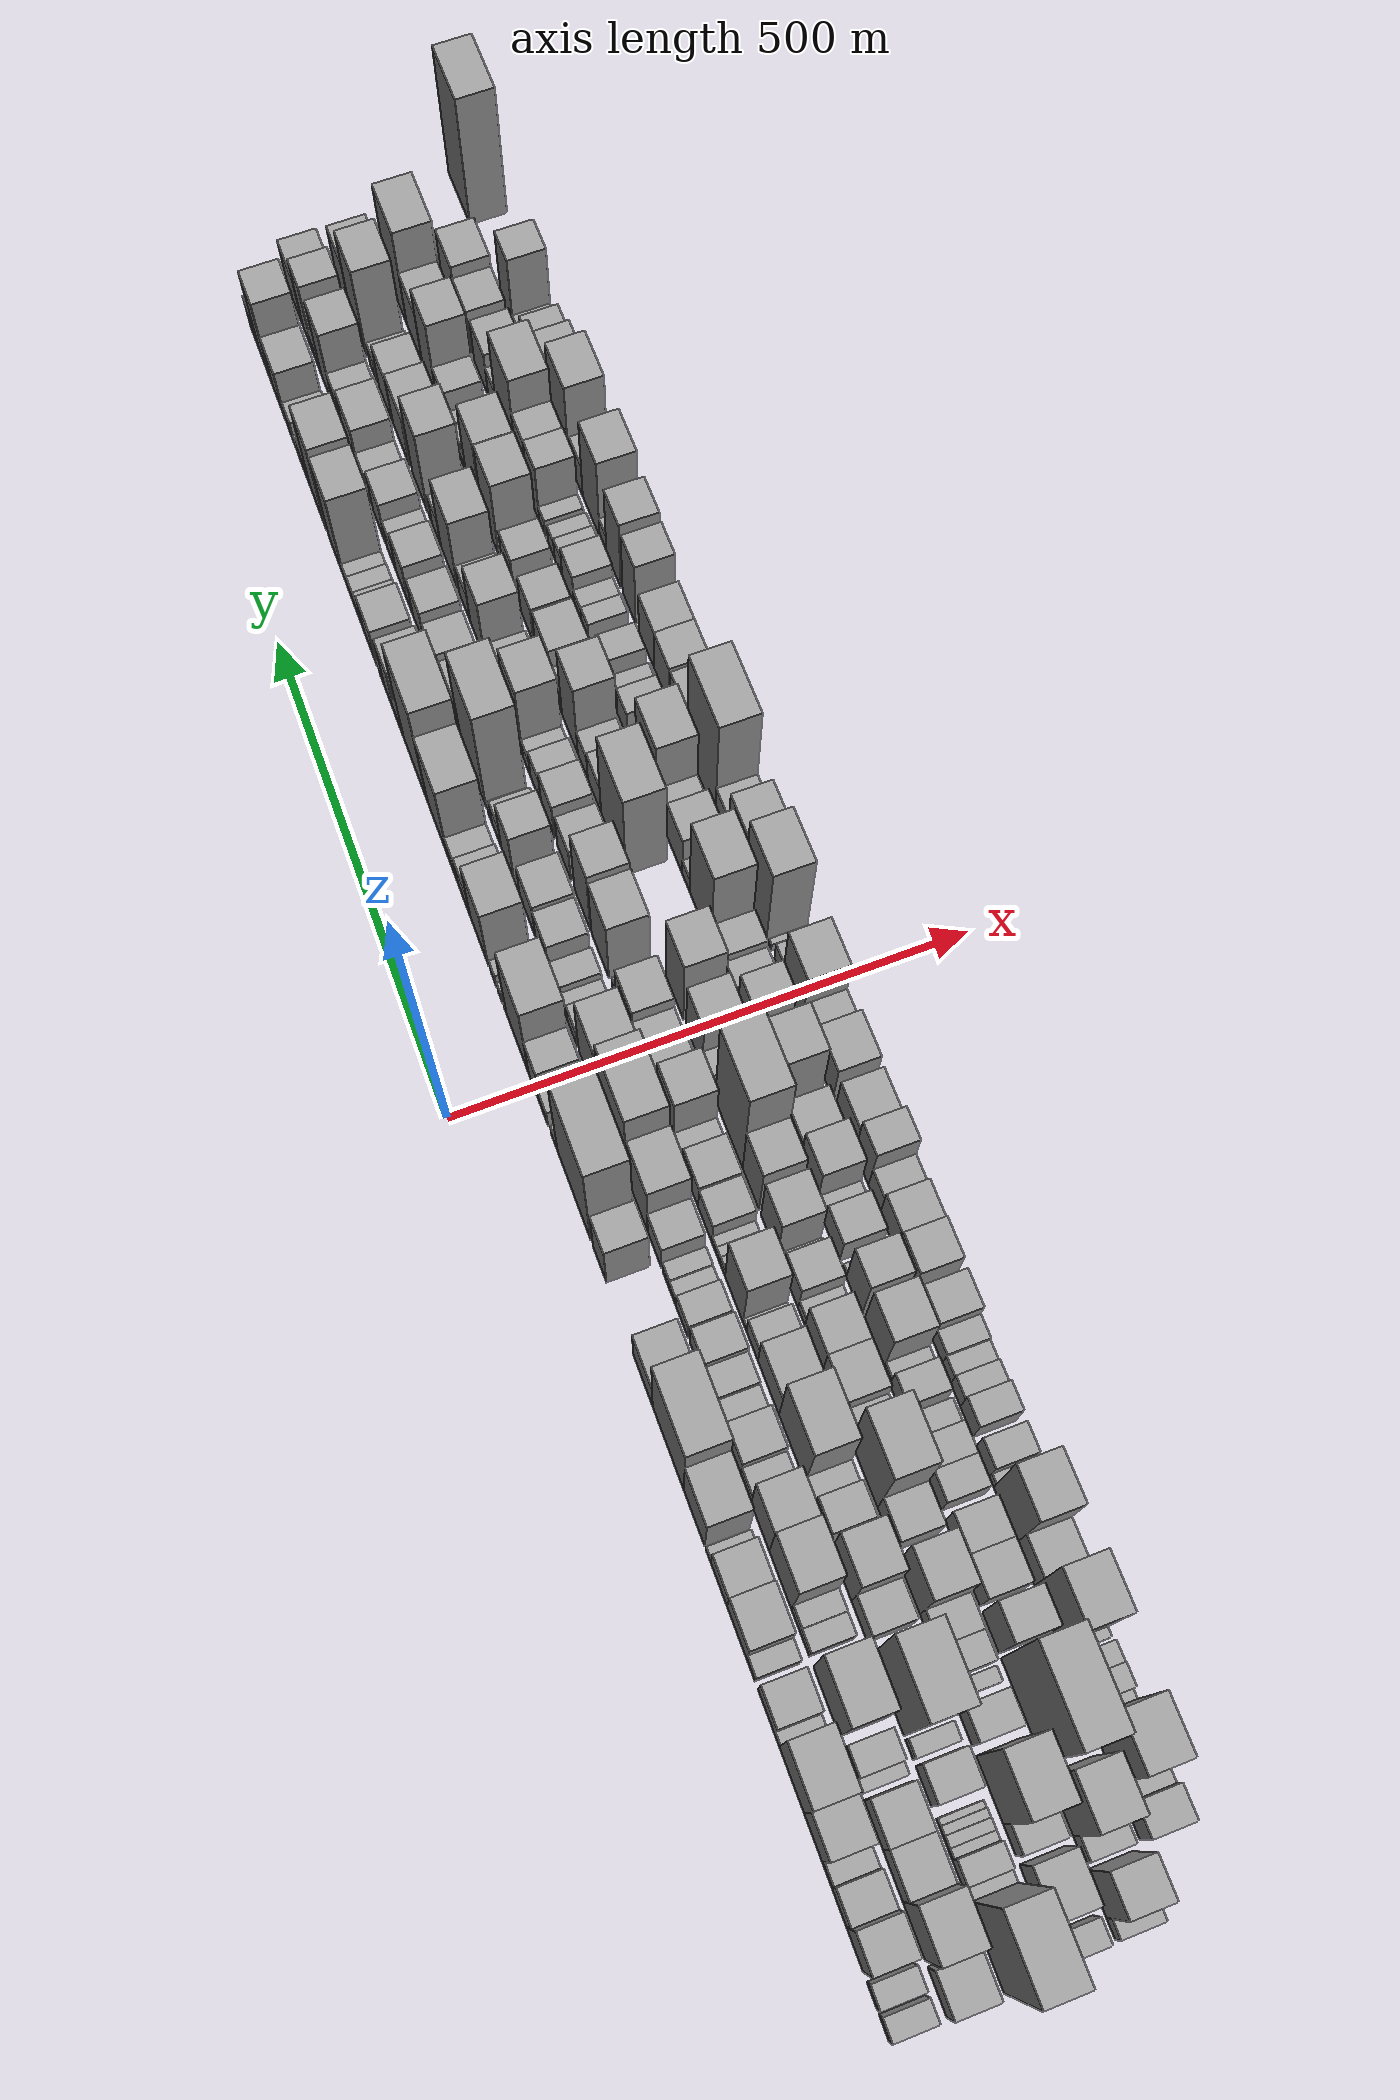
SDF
<sdf version="1.6">
 <world name="default">
  <scene>
   <sky><clouds><speed>12</speed></clouds></sky>
   <ambient>0.4 0.4 0.4 1</ambient>
   <background>0.7 0.7 0.7 1</background>
   <shadows>1</shadows>
  </scene>
  <gravity>0 0 -9.8066</gravity>
  <magnetic_field>6e-06 2.3e-05 -4.2e-05</magnetic_field>
  <physics default="0" name="default_physics" type="ode">
   <ode>
    <solver>
     <type>quick</type>
     <iters>10</iters>
     <sor>1.0</sor>
     <use_dynamic_moi_rescaling>0</use_dynamic_moi_rescaling>
    </solver>
    <constraints>
     <cfm>0</cfm>
     <erp>0.2</erp>
     <contact_max_correcting_vel>100</contact_max_correcting_vel>
     <contact_surface_layer>0.001</contact_surface_layer>
    </constraints>
   </ode>
   <max_step_size>0.004</max_step_size>
   <real_time_factor>1</real_time_factor>
   <real_time_update_rate>250</real_time_update_rate>
  </physics>
  <light name="sun" type="directional">
   <pose>0 0 10 0 0 0</pose>
   <diffuse>0.8 0.8 0.8 1</diffuse>
   <specular>0.2 0.2 0.2 1</specular>
   <attenuation>
    <range>1000</range>
    <constant>0.9</constant>
    <linear>0.01</linear>
    <quadratic>0.001</quadratic>
   </attenuation>
   <direction>-0.5 0.1 -0.9</direction>
  </light>
  <model name="building_1">
   <static>1</static>
   <pose>100.0000 -819.7989 0 0.000000 0.000000 0.000000</pose>
   <link name="link">
    <pose>0 0 19.50 0 0 0</pose>
    <collision name="collision"><geometry><box><size>40.0000 20.4023 39.0000</size></box></geometry></collision>
    <visual name="visual">
     <cast_shadows>0</cast_shadows>
     <geometry><box><size>40.0000 20.4023 39.0000</size></box></geometry>
     <material>
      <script>
       <uri>model://grey_wall/materials/scripts</uri>
       <uri>model://grey_wall/materials/textures</uri>
       <name>vrc/grey_wall</name>
      </script>
     </material>
    </visual>
   </link>
  </model>
  <model name="building_2">
   <static>1</static>
   <pose>100.0000 -795.0000 0 0.000000 0.000000 0.000000</pose>
   <link name="link">
    <pose>0 0 19.50 0 0 0</pose>
    <collision name="collision"><geometry><box><size>40.0000 21.1955 39.0000</size></box></geometry></collision>
    <visual name="visual">
     <cast_shadows>0</cast_shadows>
     <geometry><box><size>40.0000 21.1955 39.0000</size></box></geometry>
     <material>
      <script>
       <uri>model://grey_wall/materials/scripts</uri>
       <uri>model://grey_wall/materials/textures</uri>
       <name>vrc/grey_wall</name>
      </script>
     </material>
    </visual>
   </link>
  </model>
  <model name="building_3">
   <static>1</static>
   <pose>100.0000 -758.7501 0 0.000000 0.000000 0.000000</pose>
   <link name="link">
    <pose>0 0 54.00 0 0 0</pose>
    <collision name="collision"><geometry><box><size>40.0000 35.3042 108.0000</size></box></geometry></collision>
    <visual name="visual">
     <cast_shadows>0</cast_shadows>
     <geometry><box><size>40.0000 35.3042 108.0000</size></box></geometry>
     <material>
      <script>
       <uri>model://grey_wall/materials/scripts</uri>
       <uri>model://grey_wall/materials/textures</uri>
       <name>vrc/grey_wall</name>
      </script>
     </material>
    </visual>
   </link>
  </model>
  <model name="building_4">
   <static>1</static>
   <pose>100.0000 -725.2019 0 0.000000 0.000000 0.000000</pose>
   <link name="link">
    <pose>0 0 31.50 0 0 0</pose>
    <collision name="collision"><geometry><box><size>40.0000 31.7923 63.0000</size></box></geometry></collision>
    <visual name="visual">
     <cast_shadows>0</cast_shadows>
     <geometry><box><size>40.0000 31.7923 63.0000</size></box></geometry>
     <material>
      <script>
       <uri>model://grey_wall/materials/scripts</uri>
       <uri>model://grey_wall/materials/textures</uri>
       <name>vrc/grey_wall</name>
      </script>
     </material>
    </visual>
   </link>
  </model>
  <model name="building_5">
   <static>1</static>
   <pose>100.0000 -699.4300 0 0.000000 0.000000 0.000000</pose>
   <link name="link">
    <pose>0 0 18.00 0 0 0</pose>
    <collision name="collision"><geometry><box><size>40.0000 19.7514 36.0000</size></box></geometry></collision>
    <visual name="visual">
     <cast_shadows>0</cast_shadows>
     <geometry><box><size>40.0000 19.7514 36.0000</size></box></geometry>
     <material>
      <script>
       <uri>model://grey_wall/materials/scripts</uri>
       <uri>model://grey_wall/materials/textures</uri>
       <name>vrc/grey_wall</name>
      </script>
     </material>
    </visual>
   </link>
  </model>
  <model name="building_6">
   <static>1</static>
   <pose>100.0000 -670.1482 0 0.000000 0.000000 0.000000</pose>
   <link name="link">
    <pose>0 0 57.00 0 0 0</pose>
    <collision name="collision"><geometry><box><size>40.0000 38.8122 114.0000</size></box></geometry></collision>
    <visual name="visual">
     <cast_shadows>0</cast_shadows>
     <geometry><box><size>40.0000 38.8122 114.0000</size></box></geometry>
     <material>
      <script>
       <uri>model://grey_wall/materials/scripts</uri>
       <uri>model://grey_wall/materials/textures</uri>
       <name>vrc/grey_wall</name>
      </script>
     </material>
    </visual>
   </link>
  </model>
  <model name="building_7">
   <static>1</static>
   <pose>100.0000 -623.6436 0 0.000000 0.000000 0.000000</pose>
   <link name="link">
    <pose>0 0 70.50 0 0 0</pose>
    <collision name="collision"><geometry><box><size>40.0000 54.1970 141.0000</size></box></geometry></collision>
    <visual name="visual">
     <cast_shadows>0</cast_shadows>
     <geometry><box><size>40.0000 54.1970 141.0000</size></box></geometry>
     <material>
      <script>
       <uri>model://grey_wall/materials/scripts</uri>
       <uri>model://grey_wall/materials/textures</uri>
       <name>vrc/grey_wall</name>
      </script>
     </material>
    </visual>
   </link>
  </model>
  <model name="building_8">
   <static>1</static>
   <pose>100.0000 -590.8493 0 0.000000 0.000000 0.000000</pose>
   <link name="link">
    <pose>0 0 13.50 0 0 0</pose>
    <collision name="collision"><geometry><box><size>40.0000 11.3917 27.0000</size></box></geometry></collision>
    <visual name="visual">
     <cast_shadows>0</cast_shadows>
     <geometry><box><size>40.0000 11.3917 27.0000</size></box></geometry>
     <material>
      <script>
       <uri>model://grey_wall/materials/scripts</uri>
       <uri>model://grey_wall/materials/textures</uri>
       <name>vrc/grey_wall</name>
      </script>
     </material>
    </visual>
   </link>
  </model>
  <model name="building_9">
   <static>1</static>
   <pose>100.0000 -566.9279 0 0.000000 0.000000 0.000000</pose>
   <link name="link">
    <pose>0 0 33.00 0 0 0</pose>
    <collision name="collision"><geometry><box><size>40.0000 36.4511 66.0000</size></box></geometry></collision>
    <visual name="visual">
     <cast_shadows>0</cast_shadows>
     <geometry><box><size>40.0000 36.4511 66.0000</size></box></geometry>
     <material>
      <script>
       <uri>model://grey_wall/materials/scripts</uri>
       <uri>model://grey_wall/materials/textures</uri>
       <name>vrc/grey_wall</name>
      </script>
     </material>
    </visual>
   </link>
  </model>
  <model name="building_10">
   <static>1</static>
   <pose>100.0000 -532.1652 0 0.000000 0.000000 0.000000</pose>
   <link name="link">
    <pose>0 0 18.00 0 0 0</pose>
    <collision name="collision"><geometry><box><size>40.0000 19.0742 36.0000</size></box></geometry></collision>
    <visual name="visual">
     <cast_shadows>0</cast_shadows>
     <geometry><box><size>40.0000 19.0742 36.0000</size></box></geometry>
     <material>
      <script>
       <uri>model://grey_wall/materials/scripts</uri>
       <uri>model://grey_wall/materials/textures</uri>
       <name>vrc/grey_wall</name>
      </script>
     </material>
    </visual>
   </link>
  </model>
  <model name="building_11">
   <static>1</static>
   <pose>100.0000 -500.5744 0 0.000000 0.000000 0.000000</pose>
   <link name="link">
    <pose>0 0 40.50 0 0 0</pose>
    <collision name="collision"><geometry><box><size>40.0000 44.1075 81.0000</size></box></geometry></collision>
    <visual name="visual">
     <cast_shadows>0</cast_shadows>
     <geometry><box><size>40.0000 44.1075 81.0000</size></box></geometry>
     <material>
      <script>
       <uri>model://grey_wall/materials/scripts</uri>
       <uri>model://grey_wall/materials/textures</uri>
       <name>vrc/grey_wall</name>
      </script>
     </material>
    </visual>
   </link>
  </model>
  <model name="building_12">
   <static>1</static>
   <pose>100.0000 -459.6822 0 0.000000 0.000000 0.000000</pose>
   <link name="link">
    <pose>0 0 34.50 0 0 0</pose>
    <collision name="collision"><geometry><box><size>40.0000 37.6769 69.0000</size></box></geometry></collision>
    <visual name="visual">
     <cast_shadows>0</cast_shadows>
     <geometry><box><size>40.0000 37.6769 69.0000</size></box></geometry>
     <material>
      <script>
       <uri>model://grey_wall/materials/scripts</uri>
       <uri>model://grey_wall/materials/textures</uri>
       <name>vrc/grey_wall</name>
      </script>
     </material>
    </visual>
   </link>
  </model>
  <model name="building_13">
   <static>1</static>
   <pose>100.0000 -435.0364 0 0.000000 0.000000 0.000000</pose>
   <link name="link">
    <pose>0 0 12.00 0 0 0</pose>
    <collision name="collision"><geometry><box><size>40.0000 11.6146 24.0000</size></box></geometry></collision>
    <visual name="visual">
     <cast_shadows>0</cast_shadows>
     <geometry><box><size>40.0000 11.6146 24.0000</size></box></geometry>
     <material>
      <script>
       <uri>model://grey_wall/materials/scripts</uri>
       <uri>model://grey_wall/materials/textures</uri>
       <name>vrc/grey_wall</name>
      </script>
     </material>
    </visual>
   </link>
  </model>
  <model name="building_14">
   <static>1</static>
   <pose>100.0000 -401.4959 0 0.000000 0.000000 0.000000</pose>
   <link name="link">
    <pose>0 0 66.00 0 0 0</pose>
    <collision name="collision"><geometry><box><size>40.0000 49.4664 132.0000</size></box></geometry></collision>
    <visual name="visual">
     <cast_shadows>0</cast_shadows>
     <geometry><box><size>40.0000 49.4664 132.0000</size></box></geometry>
     <material>
      <script>
       <uri>model://grey_wall/materials/scripts</uri>
       <uri>model://grey_wall/materials/textures</uri>
       <name>vrc/grey_wall</name>
      </script>
     </material>
    </visual>
   </link>
  </model>
  <model name="building_15">
   <static>1</static>
   <pose>100.0000 -339.3826 0 0.000000 0.000000 0.000000</pose>
   <link name="link">
    <pose>0 0 94.50 0 0 0</pose>
    <collision name="collision"><geometry><box><size>40.0000 74.7603 189.0000</size></box></geometry></collision>
    <visual name="visual">
     <cast_shadows>0</cast_shadows>
     <geometry><box><size>40.0000 74.7603 189.0000</size></box></geometry>
     <material>
      <script>
       <uri>model://grey_wall/materials/scripts</uri>
       <uri>model://grey_wall/materials/textures</uri>
       <name>vrc/grey_wall</name>
      </script>
     </material>
    </visual>
   </link>
  </model>
  <model name="building_16">
   <static>1</static>
   <pose>100.0000 -278.3707 0 0.000000 0.000000 0.000000</pose>
   <link name="link">
    <pose>0 0 43.50 0 0 0</pose>
    <collision name="collision"><geometry><box><size>40.0000 47.2636 87.0000</size></box></geometry></collision>
    <visual name="visual">
     <cast_shadows>0</cast_shadows>
     <geometry><box><size>40.0000 47.2636 87.0000</size></box></geometry>
     <material>
      <script>
       <uri>model://grey_wall/materials/scripts</uri>
       <uri>model://grey_wall/materials/textures</uri>
       <name>vrc/grey_wall</name>
      </script>
     </material>
    </visual>
   </link>
  </model>
  <model name="building_17">
   <static>1</static>
   <pose>100.0000 -170.9762 0 0.000000 0.000000 0.000000</pose>
   <link name="link">
    <pose>0 0 55.50 0 0 0</pose>
    <collision name="collision"><geometry><box><size>40.0000 33.8418 111.0000</size></box></geometry></collision>
    <visual name="visual">
     <cast_shadows>0</cast_shadows>
     <geometry><box><size>40.0000 33.8418 111.0000</size></box></geometry>
     <material>
      <script>
       <uri>model://grey_wall/materials/scripts</uri>
       <uri>model://grey_wall/materials/textures</uri>
       <name>vrc/grey_wall</name>
      </script>
     </material>
    </visual>
   </link>
  </model>
  <model name="building_18">
   <static>1</static>
   <pose>100.0000 -105.3634 0 0.000000 0.000000 0.000000</pose>
   <link name="link">
    <pose>0 0 109.50 0 0 0</pose>
    <collision name="collision"><geometry><box><size>40.0000 85.3837 219.0000</size></box></geometry></collision>
    <visual name="visual">
     <cast_shadows>0</cast_shadows>
     <geometry><box><size>40.0000 85.3837 219.0000</size></box></geometry>
     <material>
      <script>
       <uri>model://grey_wall/materials/scripts</uri>
       <uri>model://grey_wall/materials/textures</uri>
       <name>vrc/grey_wall</name>
      </script>
     </material>
    </visual>
   </link>
  </model>
  <model name="building_19">
   <static>1</static>
   <pose>100.0000 -54.6219 0 0.000000 0.000000 0.000000</pose>
   <link name="link">
    <pose>0 0 15.00 0 0 0</pose>
    <collision name="collision"><geometry><box><size>40.0000 16.0994 30.0000</size></box></geometry></collision>
    <visual name="visual">
     <cast_shadows>0</cast_shadows>
     <geometry><box><size>40.0000 16.0994 30.0000</size></box></geometry>
     <material>
      <script>
       <uri>model://grey_wall/materials/scripts</uri>
       <uri>model://grey_wall/materials/textures</uri>
       <name>vrc/grey_wall</name>
      </script>
     </material>
    </visual>
   </link>
  </model>
  <model name="building_20">
   <static>1</static>
   <pose>100.0000 -27.5893 0 0.000000 0.000000 0.000000</pose>
   <link name="link">
    <pose>0 0 19.50 0 0 0</pose>
    <collision name="collision"><geometry><box><size>40.0000 19.9658 39.0000</size></box></geometry></collision>
    <visual name="visual">
     <cast_shadows>0</cast_shadows>
     <geometry><box><size>40.0000 19.9658 39.0000</size></box></geometry>
     <material>
      <script>
       <uri>model://grey_wall/materials/scripts</uri>
       <uri>model://grey_wall/materials/textures</uri>
       <name>vrc/grey_wall</name>
      </script>
     </material>
    </visual>
   </link>
  </model>
  <model name="building_21">
   <static>1</static>
   <pose>100.0000 -2.0361 0 0.000000 0.000000 0.000000</pose>
   <link name="link">
    <pose>0 0 46.50 0 0 0</pose>
    <collision name="collision"><geometry><box><size>40.0000 31.1406 93.0000</size></box></geometry></collision>
    <visual name="visual">
     <cast_shadows>0</cast_shadows>
     <geometry><box><size>40.0000 31.1406 93.0000</size></box></geometry>
     <material>
      <script>
       <uri>model://grey_wall/materials/scripts</uri>
       <uri>model://grey_wall/materials/textures</uri>
       <name>vrc/grey_wall</name>
      </script>
     </material>
    </visual>
   </link>
  </model>
  <model name="building_22">
   <static>1</static>
   <pose>100.0000 43.3936 0 0.000000 0.000000 0.000000</pose>
   <link name="link">
    <pose>0 0 82.50 0 0 0</pose>
    <collision name="collision"><geometry><box><size>40.0000 59.7189 165.0000</size></box></geometry></collision>
    <visual name="visual">
     <cast_shadows>0</cast_shadows>
     <geometry><box><size>40.0000 59.7189 165.0000</size></box></geometry>
     <material>
      <script>
       <uri>model://grey_wall/materials/scripts</uri>
       <uri>model://grey_wall/materials/textures</uri>
       <name>vrc/grey_wall</name>
      </script>
     </material>
    </visual>
   </link>
  </model>
  <model name="building_23">
   <static>1</static>
   <pose>100.0000 76.6870 0 0.000000 0.000000 0.000000</pose>
   <link name="link">
    <pose>0 0 7.50 0 0 0</pose>
    <collision name="collision"><geometry><box><size>40.0000 6.8679 15.0000</size></box></geometry></collision>
    <visual name="visual">
     <cast_shadows>0</cast_shadows>
     <geometry><box><size>40.0000 6.8679 15.0000</size></box></geometry>
     <material>
      <script>
       <uri>model://grey_wall/materials/scripts</uri>
       <uri>model://grey_wall/materials/textures</uri>
       <name>vrc/grey_wall</name>
      </script>
     </material>
    </visual>
   </link>
  </model>
  <model name="building_24">
   <static>1</static>
   <pose>100.0000 90.9002 0 0.000000 0.000000 0.000000</pose>
   <link name="link">
    <pose>0 0 12.00 0 0 0</pose>
    <collision name="collision"><geometry><box><size>40.0000 11.5585 24.0000</size></box></geometry></collision>
    <visual name="visual">
     <cast_shadows>0</cast_shadows>
     <geometry><box><size>40.0000 11.5585 24.0000</size></box></geometry>
     <material>
      <script>
       <uri>model://grey_wall/materials/scripts</uri>
       <uri>model://grey_wall/materials/textures</uri>
       <name>vrc/grey_wall</name>
      </script>
     </material>
    </visual>
   </link>
  </model>
  <model name="building_25">
   <static>1</static>
   <pose>100.0000 108.6364 0 0.000000 0.000000 0.000000</pose>
   <link name="link">
    <pose>0 0 15.00 0 0 0</pose>
    <collision name="collision"><geometry><box><size>40.0000 15.9138 30.0000</size></box></geometry></collision>
    <visual name="visual">
     <cast_shadows>0</cast_shadows>
     <geometry><box><size>40.0000 15.9138 30.0000</size></box></geometry>
     <material>
      <script>
       <uri>model://grey_wall/materials/scripts</uri>
       <uri>model://grey_wall/materials/textures</uri>
       <name>vrc/grey_wall</name>
      </script>
     </material>
    </visual>
   </link>
  </model>
  <model name="building_26">
   <static>1</static>
   <pose>100.0000 147.6354 0 0.000000 0.000000 0.000000</pose>
   <link name="link">
    <pose>0 0 63.00 0 0 0</pose>
    <collision name="collision"><geometry><box><size>40.0000 50.0843 126.0000</size></box></geometry></collision>
    <visual name="visual">
     <cast_shadows>0</cast_shadows>
     <geometry><box><size>40.0000 50.0843 126.0000</size></box></geometry>
     <material>
      <script>
       <uri>model://grey_wall/materials/scripts</uri>
       <uri>model://grey_wall/materials/textures</uri>
       <name>vrc/grey_wall</name>
      </script>
     </material>
    </visual>
   </link>
  </model>
  <model name="building_27">
   <static>1</static>
   <pose>100.0000 190.1945 0 0.000000 0.000000 0.000000</pose>
   <link name="link">
    <pose>0 0 31.50 0 0 0</pose>
    <collision name="collision"><geometry><box><size>40.0000 35.0339 63.0000</size></box></geometry></collision>
    <visual name="visual">
     <cast_shadows>0</cast_shadows>
     <geometry><box><size>40.0000 35.0339 63.0000</size></box></geometry>
     <material>
      <script>
       <uri>model://grey_wall/materials/scripts</uri>
       <uri>model://grey_wall/materials/textures</uri>
       <name>vrc/grey_wall</name>
      </script>
     </material>
    </visual>
   </link>
  </model>
  <model name="building_28">
   <static>1</static>
   <pose>100.0000 221.5984 0 0.000000 0.000000 0.000000</pose>
   <link name="link">
    <pose>0 0 24.00 0 0 0</pose>
    <collision name="collision"><geometry><box><size>40.0000 27.7739 48.0000</size></box></geometry></collision>
    <visual name="visual">
     <cast_shadows>0</cast_shadows>
     <geometry><box><size>40.0000 27.7739 48.0000</size></box></geometry>
     <material>
      <script>
       <uri>model://grey_wall/materials/scripts</uri>
       <uri>model://grey_wall/materials/textures</uri>
       <name>vrc/grey_wall</name>
      </script>
     </material>
    </visual>
   </link>
  </model>
  <model name="building_29">
   <static>1</static>
   <pose>100.0000 264.2516 0 0.000000 0.000000 0.000000</pose>
   <link name="link">
    <pose>0 0 73.50 0 0 0</pose>
    <collision name="collision"><geometry><box><size>40.0000 57.5324 147.0000</size></box></geometry></collision>
    <visual name="visual">
     <cast_shadows>0</cast_shadows>
     <geometry><box><size>40.0000 57.5324 147.0000</size></box></geometry>
     <material>
      <script>
       <uri>model://grey_wall/materials/scripts</uri>
       <uri>model://grey_wall/materials/textures</uri>
       <name>vrc/grey_wall</name>
      </script>
     </material>
    </visual>
   </link>
  </model>
  <model name="building_30">
   <static>1</static>
   <pose>100.0000 328.5669 0 0.000000 0.000000 0.000000</pose>
   <link name="link">
    <pose>0 0 97.50 0 0 0</pose>
    <collision name="collision"><geometry><box><size>40.0000 71.0983 195.0000</size></box></geometry></collision>
    <visual name="visual">
     <cast_shadows>0</cast_shadows>
     <geometry><box><size>40.0000 71.0983 195.0000</size></box></geometry>
     <material>
      <script>
       <uri>model://grey_wall/materials/scripts</uri>
       <uri>model://grey_wall/materials/textures</uri>
       <name>vrc/grey_wall</name>
      </script>
     </material>
    </visual>
   </link>
  </model>
  <model name="building_31">
   <static>1</static>
   <pose>100.0000 374.6300 0 0.000000 0.000000 0.000000</pose>
   <link name="link">
    <pose>0 0 19.50 0 0 0</pose>
    <collision name="collision"><geometry><box><size>40.0000 21.0278 39.0000</size></box></geometry></collision>
    <visual name="visual">
     <cast_shadows>0</cast_shadows>
     <geometry><box><size>40.0000 21.0278 39.0000</size></box></geometry>
     <material>
      <script>
       <uri>model://grey_wall/materials/scripts</uri>
       <uri>model://grey_wall/materials/textures</uri>
       <name>vrc/grey_wall</name>
      </script>
     </material>
    </visual>
   </link>
  </model>
  <model name="building_32">
   <static>1</static>
   <pose>100.0000 404.0000 0 0.000000 0.000000 0.000000</pose>
   <link name="link">
    <pose>0 0 48.00 0 0 0</pose>
    <collision name="collision"><geometry><box><size>40.0000 37.7122 96.0000</size></box></geometry></collision>
    <visual name="visual">
     <cast_shadows>0</cast_shadows>
     <geometry><box><size>40.0000 37.7122 96.0000</size></box></geometry>
     <material>
      <script>
       <uri>model://grey_wall/materials/scripts</uri>
       <uri>model://grey_wall/materials/textures</uri>
       <name>vrc/grey_wall</name>
      </script>
     </material>
    </visual>
   </link>
  </model>
  <model name="building_33">
   <static>1</static>
   <pose>100.0000 429.2658 0 0.000000 0.000000 0.000000</pose>
   <link name="link">
    <pose>0 0 13.50 0 0 0</pose>
    <collision name="collision"><geometry><box><size>40.0000 12.8195 27.0000</size></box></geometry></collision>
    <visual name="visual">
     <cast_shadows>0</cast_shadows>
     <geometry><box><size>40.0000 12.8195 27.0000</size></box></geometry>
     <material>
      <script>
       <uri>model://grey_wall/materials/scripts</uri>
       <uri>model://grey_wall/materials/textures</uri>
       <name>vrc/grey_wall</name>
      </script>
     </material>
    </visual>
   </link>
  </model>
  <model name="building_34">
   <static>1</static>
   <pose>100.0000 464.8420 0 0.000000 0.000000 0.000000</pose>
   <link name="link">
    <pose>0 0 34.50 0 0 0</pose>
    <collision name="collision"><geometry><box><size>40.0000 40.3327 69.0000</size></box></geometry></collision>
    <visual name="visual">
     <cast_shadows>0</cast_shadows>
     <geometry><box><size>40.0000 40.3327 69.0000</size></box></geometry>
     <material>
      <script>
       <uri>model://grey_wall/materials/scripts</uri>
       <uri>model://grey_wall/materials/textures</uri>
       <name>vrc/grey_wall</name>
      </script>
     </material>
    </visual>
   </link>
  </model>
  <model name="building_35">
   <static>1</static>
   <pose>100.0000 495.4807 0 0.000000 0.000000 0.000000</pose>
   <link name="link">
    <pose>0 0 19.50 0 0 0</pose>
    <collision name="collision"><geometry><box><size>40.0000 20.9448 39.0000</size></box></geometry></collision>
    <visual name="visual">
     <cast_shadows>0</cast_shadows>
     <geometry><box><size>40.0000 20.9448 39.0000</size></box></geometry>
     <material>
      <script>
       <uri>model://grey_wall/materials/scripts</uri>
       <uri>model://grey_wall/materials/textures</uri>
       <name>vrc/grey_wall</name>
      </script>
     </material>
    </visual>
   </link>
  </model>
  <model name="building_36">
   <static>1</static>
   <pose>100.0000 515.7613 0 0.000000 0.000000 0.000000</pose>
   <link name="link">
    <pose>0 0 18.00 0 0 0</pose>
    <collision name="collision"><geometry><box><size>40.0000 19.6164 36.0000</size></box></geometry></collision>
    <visual name="visual">
     <cast_shadows>0</cast_shadows>
     <geometry><box><size>40.0000 19.6164 36.0000</size></box></geometry>
     <material>
      <script>
       <uri>model://grey_wall/materials/scripts</uri>
       <uri>model://grey_wall/materials/textures</uri>
       <name>vrc/grey_wall</name>
      </script>
     </material>
    </visual>
   </link>
  </model>
  <model name="building_37">
   <static>1</static>
   <pose>100.0000 534.4248 0 0.000000 0.000000 0.000000</pose>
   <link name="link">
    <pose>0 0 15.00 0 0 0</pose>
    <collision name="collision"><geometry><box><size>40.0000 17.7105 30.0000</size></box></geometry></collision>
    <visual name="visual">
     <cast_shadows>0</cast_shadows>
     <geometry><box><size>40.0000 17.7105 30.0000</size></box></geometry>
     <material>
      <script>
       <uri>model://grey_wall/materials/scripts</uri>
       <uri>model://grey_wall/materials/textures</uri>
       <name>vrc/grey_wall</name>
      </script>
     </material>
    </visual>
   </link>
  </model>
  <model name="building_38">
   <static>1</static>
   <pose>100.0000 567.6090 0 0.000000 0.000000 0.000000</pose>
   <link name="link">
    <pose>0 0 73.50 0 0 0</pose>
    <collision name="collision"><geometry><box><size>40.0000 48.6578 147.0000</size></box></geometry></collision>
    <visual name="visual">
     <cast_shadows>0</cast_shadows>
     <geometry><box><size>40.0000 48.6578 147.0000</size></box></geometry>
     <material>
      <script>
       <uri>model://grey_wall/materials/scripts</uri>
       <uri>model://grey_wall/materials/textures</uri>
       <name>vrc/grey_wall</name>
      </script>
     </material>
    </visual>
   </link>
  </model>
  <model name="building_39">
   <static>1</static>
   <pose>100.0000 625.2017 0 0.000000 0.000000 0.000000</pose>
   <link name="link">
    <pose>0 0 73.50 0 0 0</pose>
    <collision name="collision"><geometry><box><size>40.0000 50.5275 147.0000</size></box></geometry></collision>
    <visual name="visual">
     <cast_shadows>0</cast_shadows>
     <geometry><box><size>40.0000 50.5275 147.0000</size></box></geometry>
     <material>
      <script>
       <uri>model://grey_wall/materials/scripts</uri>
       <uri>model://grey_wall/materials/textures</uri>
       <name>vrc/grey_wall</name>
      </script>
     </material>
    </visual>
   </link>
  </model>
  <model name="building_40">
   <static>1</static>
   <pose>100.0000 664.7520 0 0.000000 0.000000 0.000000</pose>
   <link name="link">
    <pose>0 0 24.00 0 0 0</pose>
    <collision name="collision"><geometry><box><size>40.0000 28.5732 48.0000</size></box></geometry></collision>
    <visual name="visual">
     <cast_shadows>0</cast_shadows>
     <geometry><box><size>40.0000 28.5732 48.0000</size></box></geometry>
     <material>
      <script>
       <uri>model://grey_wall/materials/scripts</uri>
       <uri>model://grey_wall/materials/textures</uri>
       <name>vrc/grey_wall</name>
      </script>
     </material>
    </visual>
   </link>
  </model>
  <model name="building_41">
   <static>1</static>
   <pose>100.0000 689.0371 0 0.000000 0.000000 0.000000</pose>
   <link name="link">
    <pose>0 0 13.50 0 0 0</pose>
    <collision name="collision"><geometry><box><size>40.0000 11.9969 27.0000</size></box></geometry></collision>
    <visual name="visual">
     <cast_shadows>0</cast_shadows>
     <geometry><box><size>40.0000 11.9969 27.0000</size></box></geometry>
     <material>
      <script>
       <uri>model://grey_wall/materials/scripts</uri>
       <uri>model://grey_wall/materials/textures</uri>
       <name>vrc/grey_wall</name>
      </script>
     </material>
    </visual>
   </link>
  </model>
  <model name="building_42">
   <static>1</static>
   <pose>100.0000 710.2191 0 0.000000 0.000000 0.000000</pose>
   <link name="link">
    <pose>0 0 22.50 0 0 0</pose>
    <collision name="collision"><geometry><box><size>40.0000 24.3671 45.0000</size></box></geometry></collision>
    <visual name="visual">
     <cast_shadows>0</cast_shadows>
     <geometry><box><size>40.0000 24.3671 45.0000</size></box></geometry>
     <material>
      <script>
       <uri>model://grey_wall/materials/scripts</uri>
       <uri>model://grey_wall/materials/textures</uri>
       <name>vrc/grey_wall</name>
      </script>
     </material>
    </visual>
   </link>
  </model>
  <model name="building_43">
   <static>1</static>
   <pose>100.0000 751.3735 0 0.000000 0.000000 0.000000</pose>
   <link name="link">
    <pose>0 0 42.00 0 0 0</pose>
    <collision name="collision"><geometry><box><size>40.0000 43.9418 84.0000</size></box></geometry></collision>
    <visual name="visual">
     <cast_shadows>0</cast_shadows>
     <geometry><box><size>40.0000 43.9418 84.0000</size></box></geometry>
     <material>
      <script>
       <uri>model://grey_wall/materials/scripts</uri>
       <uri>model://grey_wall/materials/textures</uri>
       <name>vrc/grey_wall</name>
      </script>
     </material>
    </visual>
   </link>
  </model>
  <model name="building_44">
   <static>1</static>
   <pose>100.0000 797.4635 0 0.000000 0.000000 0.000000</pose>
   <link name="link">
    <pose>0 0 66.00 0 0 0</pose>
    <collision name="collision"><geometry><box><size>40.0000 40.2381 132.0000</size></box></geometry></collision>
    <visual name="visual">
     <cast_shadows>0</cast_shadows>
     <geometry><box><size>40.0000 40.2381 132.0000</size></box></geometry>
     <material>
      <script>
       <uri>model://grey_wall/materials/scripts</uri>
       <uri>model://grey_wall/materials/textures</uri>
       <name>vrc/grey_wall</name>
      </script>
     </material>
    </visual>
   </link>
  </model>
  <model name="building_45">
   <static>1</static>
   <pose>100.0000 831.5368 0 0.000000 0.000000 0.000000</pose>
   <link name="link">
    <pose>0 0 27.00 0 0 0</pose>
    <collision name="collision"><geometry><box><size>40.0000 27.9085 54.0000</size></box></geometry></collision>
    <visual name="visual">
     <cast_shadows>0</cast_shadows>
     <geometry><box><size>40.0000 27.9085 54.0000</size></box></geometry>
     <material>
      <script>
       <uri>model://grey_wall/materials/scripts</uri>
       <uri>model://grey_wall/materials/textures</uri>
       <name>vrc/grey_wall</name>
      </script>
     </material>
    </visual>
   </link>
  </model>
  <model name="building_46">
   <static>1</static>
   <pose>149.0000 -810.5329 0 0.000000 0.000000 0.000000</pose>
   <link name="link">
    <pose>0 0 33.00 0 0 0</pose>
    <collision name="collision"><geometry><box><size>40.0000 38.9342 66.0000</size></box></geometry></collision>
    <visual name="visual">
     <cast_shadows>0</cast_shadows>
     <geometry><box><size>40.0000 38.9342 66.0000</size></box></geometry>
     <material>
      <script>
       <uri>model://grey_wall/materials/scripts</uri>
       <uri>model://grey_wall/materials/textures</uri>
       <name>vrc/grey_wall</name>
      </script>
     </material>
    </visual>
   </link>
  </model>
  <model name="building_47">
   <static>1</static>
   <pose>149.0000 -762.7635 0 0.000000 0.000000 0.000000</pose>
   <link name="link">
    <pose>0 0 67.50 0 0 0</pose>
    <collision name="collision"><geometry><box><size>40.0000 46.6046 135.0000</size></box></geometry></collision>
    <visual name="visual">
     <cast_shadows>0</cast_shadows>
     <geometry><box><size>40.0000 46.6046 135.0000</size></box></geometry>
     <material>
      <script>
       <uri>model://grey_wall/materials/scripts</uri>
       <uri>model://grey_wall/materials/textures</uri>
       <name>vrc/grey_wall</name>
      </script>
     </material>
    </visual>
   </link>
  </model>
  <model name="building_48">
   <static>1</static>
   <pose>149.0000 -718.9374 0 0.000000 0.000000 0.000000</pose>
   <link name="link">
    <pose>0 0 34.50 0 0 0</pose>
    <collision name="collision"><geometry><box><size>40.0000 41.0476 69.0000</size></box></geometry></collision>
    <visual name="visual">
     <cast_shadows>0</cast_shadows>
     <geometry><box><size>40.0000 41.0476 69.0000</size></box></geometry>
     <material>
      <script>
       <uri>model://grey_wall/materials/scripts</uri>
       <uri>model://grey_wall/materials/textures</uri>
       <name>vrc/grey_wall</name>
      </script>
     </material>
    </visual>
   </link>
  </model>
  <model name="building_49">
   <static>1</static>
   <pose>149.0000 -678.3683 0 0.000000 0.000000 0.000000</pose>
   <link name="link">
    <pose>0 0 34.50 0 0 0</pose>
    <collision name="collision"><geometry><box><size>40.0000 40.0906 69.0000</size></box></geometry></collision>
    <visual name="visual">
     <cast_shadows>0</cast_shadows>
     <geometry><box><size>40.0000 40.0906 69.0000</size></box></geometry>
     <material>
      <script>
       <uri>model://grey_wall/materials/scripts</uri>
       <uri>model://grey_wall/materials/textures</uri>
       <name>vrc/grey_wall</name>
      </script>
     </material>
    </visual>
   </link>
  </model>
  <model name="building_50">
   <static>1</static>
   <pose>149.0000 -647.5797 0 0.000000 0.000000 0.000000</pose>
   <link name="link">
    <pose>0 0 12.00 0 0 0</pose>
    <collision name="collision"><geometry><box><size>40.0000 11.4866 24.0000</size></box></geometry></collision>
    <visual name="visual">
     <cast_shadows>0</cast_shadows>
     <geometry><box><size>40.0000 11.4866 24.0000</size></box></geometry>
     <material>
      <script>
       <uri>model://grey_wall/materials/scripts</uri>
       <uri>model://grey_wall/materials/textures</uri>
       <name>vrc/grey_wall</name>
      </script>
     </material>
    </visual>
   </link>
  </model>
  <model name="building_51">
   <static>1</static>
   <pose>149.0000 -628.5287 0 0.000000 0.000000 0.000000</pose>
   <link name="link">
    <pose>0 0 24.00 0 0 0</pose>
    <collision name="collision"><geometry><box><size>40.0000 26.6155 48.0000</size></box></geometry></collision>
    <visual name="visual">
     <cast_shadows>0</cast_shadows>
     <geometry><box><size>40.0000 26.6155 48.0000</size></box></geometry>
     <material>
      <script>
       <uri>model://grey_wall/materials/scripts</uri>
       <uri>model://grey_wall/materials/textures</uri>
       <name>vrc/grey_wall</name>
      </script>
     </material>
    </visual>
   </link>
  </model>
  <model name="building_52">
   <static>1</static>
   <pose>149.0000 -577.2613 0 0.000000 0.000000 0.000000</pose>
   <link name="link">
    <pose>0 0 75.00 0 0 0</pose>
    <collision name="collision"><geometry><box><size>40.0000 57.9193 150.0000</size></box></geometry></collision>
    <visual name="visual">
     <cast_shadows>0</cast_shadows>
     <geometry><box><size>40.0000 57.9193 150.0000</size></box></geometry>
     <material>
      <script>
       <uri>model://grey_wall/materials/scripts</uri>
       <uri>model://grey_wall/materials/textures</uri>
       <name>vrc/grey_wall</name>
      </script>
     </material>
    </visual>
   </link>
  </model>
  <model name="building_53">
   <static>1</static>
   <pose>149.0000 -529.0695 0 0.000000 0.000000 0.000000</pose>
   <link name="link">
    <pose>0 0 18.00 0 0 0</pose>
    <collision name="collision"><geometry><box><size>40.0000 20.4644 36.0000</size></box></geometry></collision>
    <visual name="visual">
     <cast_shadows>0</cast_shadows>
     <geometry><box><size>40.0000 20.4644 36.0000</size></box></geometry>
     <material>
      <script>
       <uri>model://grey_wall/materials/scripts</uri>
       <uri>model://grey_wall/materials/textures</uri>
       <name>vrc/grey_wall</name>
      </script>
     </material>
    </visual>
   </link>
  </model>
  <model name="building_54">
   <static>1</static>
   <pose>149.0000 -509.0496 0 0.000000 0.000000 0.000000</pose>
   <link name="link">
    <pose>0 0 19.50 0 0 0</pose>
    <collision name="collision"><geometry><box><size>40.0000 19.5755 39.0000</size></box></geometry></collision>
    <visual name="visual">
     <cast_shadows>0</cast_shadows>
     <geometry><box><size>40.0000 19.5755 39.0000</size></box></geometry>
     <material>
      <script>
       <uri>model://grey_wall/materials/scripts</uri>
       <uri>model://grey_wall/materials/textures</uri>
       <name>vrc/grey_wall</name>
      </script>
     </material>
    </visual>
   </link>
  </model>
  <model name="building_55">
   <static>1</static>
   <pose>149.0000 -474.1920 0 0.000000 0.000000 0.000000</pose>
   <link name="link">
    <pose>0 0 69.00 0 0 0</pose>
    <collision name="collision"><geometry><box><size>40.0000 50.1397 138.0000</size></box></geometry></collision>
    <visual name="visual">
     <cast_shadows>0</cast_shadows>
     <geometry><box><size>40.0000 50.1397 138.0000</size></box></geometry>
     <material>
      <script>
       <uri>model://grey_wall/materials/scripts</uri>
       <uri>model://grey_wall/materials/textures</uri>
       <name>vrc/grey_wall</name>
      </script>
     </material>
    </visual>
   </link>
  </model>
  <model name="building_56">
   <static>1</static>
   <pose>149.0000 -428.2778 0 0.000000 0.000000 0.000000</pose>
   <link name="link">
    <pose>0 0 63.00 0 0 0</pose>
    <collision name="collision"><geometry><box><size>40.0000 41.6887 126.0000</size></box></geometry></collision>
    <visual name="visual">
     <cast_shadows>0</cast_shadows>
     <geometry><box><size>40.0000 41.6887 126.0000</size></box></geometry>
     <material>
      <script>
       <uri>model://grey_wall/materials/scripts</uri>
       <uri>model://grey_wall/materials/textures</uri>
       <name>vrc/grey_wall</name>
      </script>
     </material>
    </visual>
   </link>
  </model>
  <model name="building_57">
   <static>1</static>
   <pose>149.0000 -395.1287 0 0.000000 0.000000 0.000000</pose>
   <link name="link">
    <pose>0 0 24.00 0 0 0</pose>
    <collision name="collision"><geometry><box><size>40.0000 24.6093 48.0000</size></box></geometry></collision>
    <visual name="visual">
     <cast_shadows>0</cast_shadows>
     <geometry><box><size>40.0000 24.6093 48.0000</size></box></geometry>
     <material>
      <script>
       <uri>model://grey_wall/materials/scripts</uri>
       <uri>model://grey_wall/materials/textures</uri>
       <name>vrc/grey_wall</name>
      </script>
     </material>
    </visual>
   </link>
  </model>
  <model name="building_58">
   <static>1</static>
   <pose>149.0000 -364.3468 0 0.000000 0.000000 0.000000</pose>
   <link name="link">
    <pose>0 0 34.50 0 0 0</pose>
    <collision name="collision"><geometry><box><size>40.0000 36.9546 69.0000</size></box></geometry></collision>
    <visual name="visual">
     <cast_shadows>0</cast_shadows>
     <geometry><box><size>40.0000 36.9546 69.0000</size></box></geometry>
     <material>
      <script>
       <uri>model://grey_wall/materials/scripts</uri>
       <uri>model://grey_wall/materials/textures</uri>
       <name>vrc/grey_wall</name>
      </script>
     </material>
    </visual>
   </link>
  </model>
  <model name="building_59">
   <static>1</static>
   <pose>149.0000 -332.0587 0 0.000000 0.000000 0.000000</pose>
   <link name="link">
    <pose>0 0 19.50 0 0 0</pose>
    <collision name="collision"><geometry><box><size>40.0000 19.6216 39.0000</size></box></geometry></collision>
    <visual name="visual">
     <cast_shadows>0</cast_shadows>
     <geometry><box><size>40.0000 19.6216 39.0000</size></box></geometry>
     <material>
      <script>
       <uri>model://grey_wall/materials/scripts</uri>
       <uri>model://grey_wall/materials/textures</uri>
       <name>vrc/grey_wall</name>
      </script>
     </material>
    </visual>
   </link>
  </model>
  <model name="building_60">
   <static>1</static>
   <pose>149.0000 -308.2977 0 0.000000 0.000000 0.000000</pose>
   <link name="link">
    <pose>0 0 24.00 0 0 0</pose>
    <collision name="collision"><geometry><box><size>40.0000 27.9004 48.0000</size></box></geometry></collision>
    <visual name="visual">
     <cast_shadows>0</cast_shadows>
     <geometry><box><size>40.0000 27.9004 48.0000</size></box></geometry>
     <material>
      <script>
       <uri>model://grey_wall/materials/scripts</uri>
       <uri>model://grey_wall/materials/textures</uri>
       <name>vrc/grey_wall</name>
      </script>
     </material>
    </visual>
   </link>
  </model>
  <model name="building_61">
   <static>1</static>
   <pose>149.0000 -278.0812 0 0.000000 0.000000 0.000000</pose>
   <link name="link">
    <pose>0 0 31.50 0 0 0</pose>
    <collision name="collision"><geometry><box><size>40.0000 32.5325 63.0000</size></box></geometry></collision>
    <visual name="visual">
     <cast_shadows>0</cast_shadows>
     <geometry><box><size>40.0000 32.5325 63.0000</size></box></geometry>
     <material>
      <script>
       <uri>model://grey_wall/materials/scripts</uri>
       <uri>model://grey_wall/materials/textures</uri>
       <name>vrc/grey_wall</name>
      </script>
     </material>
    </visual>
   </link>
  </model>
  <model name="building_62">
   <static>1</static>
   <pose>149.0000 -243.5460 0 0.000000 0.000000 0.000000</pose>
   <link name="link">
    <pose>0 0 24.00 0 0 0</pose>
    <collision name="collision"><geometry><box><size>40.0000 28.5379 48.0000</size></box></geometry></collision>
    <visual name="visual">
     <cast_shadows>0</cast_shadows>
     <geometry><box><size>40.0000 28.5379 48.0000</size></box></geometry>
     <material>
      <script>
       <uri>model://grey_wall/materials/scripts</uri>
       <uri>model://grey_wall/materials/textures</uri>
       <name>vrc/grey_wall</name>
      </script>
     </material>
    </visual>
   </link>
  </model>
  <model name="building_63">
   <static>1</static>
   <pose>149.0000 -220.7330 0 0.000000 0.000000 0.000000</pose>
   <link name="link">
    <pose>0 0 15.00 0 0 0</pose>
    <collision name="collision"><geometry><box><size>40.0000 17.0881 30.0000</size></box></geometry></collision>
    <visual name="visual">
     <cast_shadows>0</cast_shadows>
     <geometry><box><size>40.0000 17.0881 30.0000</size></box></geometry>
     <material>
      <script>
       <uri>model://grey_wall/materials/scripts</uri>
       <uri>model://grey_wall/materials/textures</uri>
       <name>vrc/grey_wall</name>
      </script>
     </material>
    </visual>
   </link>
  </model>
  <model name="building_64">
   <static>1</static>
   <pose>149.0000 -203.7833 0 0.000000 0.000000 0.000000</pose>
   <link name="link">
    <pose>0 0 16.50 0 0 0</pose>
    <collision name="collision"><geometry><box><size>40.0000 16.8115 33.0000</size></box></geometry></collision>
    <visual name="visual">
     <cast_shadows>0</cast_shadows>
     <geometry><box><size>40.0000 16.8115 33.0000</size></box></geometry>
     <material>
      <script>
       <uri>model://grey_wall/materials/scripts</uri>
       <uri>model://grey_wall/materials/textures</uri>
       <name>vrc/grey_wall</name>
      </script>
     </material>
    </visual>
   </link>
  </model>
  <model name="building_65">
   <static>1</static>
   <pose>149.0000 -175.4910 0 0.000000 0.000000 0.000000</pose>
   <link name="link">
    <pose>0 0 33.00 0 0 0</pose>
    <collision name="collision"><geometry><box><size>40.0000 33.7731 66.0000</size></box></geometry></collision>
    <visual name="visual">
     <cast_shadows>0</cast_shadows>
     <geometry><box><size>40.0000 33.7731 66.0000</size></box></geometry>
     <material>
      <script>
       <uri>model://grey_wall/materials/scripts</uri>
       <uri>model://grey_wall/materials/textures</uri>
       <name>vrc/grey_wall</name>
      </script>
     </material>
    </visual>
   </link>
  </model>
  <model name="building_66">
   <static>1</static>
   <pose>149.0000 -134.2729 0 0.000000 0.000000 0.000000</pose>
   <link name="link">
    <pose>0 0 66.00 0 0 0</pose>
    <collision name="collision"><geometry><box><size>40.0000 48.6631 132.0000</size></box></geometry></collision>
    <visual name="visual">
     <cast_shadows>0</cast_shadows>
     <geometry><box><size>40.0000 48.6631 132.0000</size></box></geometry>
     <material>
      <script>
       <uri>model://grey_wall/materials/scripts</uri>
       <uri>model://grey_wall/materials/textures</uri>
       <name>vrc/grey_wall</name>
      </script>
     </material>
    </visual>
   </link>
  </model>
  <model name="building_67">
   <static>1</static>
   <pose>149.0000 -71.8747 0 0.000000 0.000000 0.000000</pose>
   <link name="link">
    <pose>0 0 90.00 0 0 0</pose>
    <collision name="collision"><geometry><box><size>40.0000 70.1333 180.0000</size></box></geometry></collision>
    <visual name="visual">
     <cast_shadows>0</cast_shadows>
     <geometry><box><size>40.0000 70.1333 180.0000</size></box></geometry>
     <material>
      <script>
       <uri>model://grey_wall/materials/scripts</uri>
       <uri>model://grey_wall/materials/textures</uri>
       <name>vrc/grey_wall</name>
      </script>
     </material>
    </visual>
   </link>
  </model>
  <model name="building_68">
   <static>1</static>
   <pose>149.0000 -5.6333 0 0.000000 0.000000 0.000000</pose>
   <link name="link">
    <pose>0 0 69.00 0 0 0</pose>
    <collision name="collision"><geometry><box><size>40.0000 46.3496 138.0000</size></box></geometry></collision>
    <visual name="visual">
     <cast_shadows>0</cast_shadows>
     <geometry><box><size>40.0000 46.3496 138.0000</size></box></geometry>
     <material>
      <script>
       <uri>model://grey_wall/materials/scripts</uri>
       <uri>model://grey_wall/materials/textures</uri>
       <name>vrc/grey_wall</name>
      </script>
     </material>
    </visual>
   </link>
  </model>
  <model name="building_69">
   <static>1</static>
   <pose>149.0000 34.6953 0 0.000000 0.000000 0.000000</pose>
   <link name="link">
    <pose>0 0 22.50 0 0 0</pose>
    <collision name="collision"><geometry><box><size>40.0000 26.3077 45.0000</size></box></geometry></collision>
    <visual name="visual">
     <cast_shadows>0</cast_shadows>
     <geometry><box><size>40.0000 26.3077 45.0000</size></box></geometry>
     <material>
      <script>
       <uri>model://grey_wall/materials/scripts</uri>
       <uri>model://grey_wall/materials/textures</uri>
       <name>vrc/grey_wall</name>
      </script>
     </material>
    </visual>
   </link>
  </model>
  <model name="building_70">
   <static>1</static>
   <pose>149.0000 56.5618 0 0.000000 0.000000 0.000000</pose>
   <link name="link">
    <pose>0 0 15.00 0 0 0</pose>
    <collision name="collision"><geometry><box><size>40.0000 17.4253 30.0000</size></box></geometry></collision>
    <visual name="visual">
     <cast_shadows>0</cast_shadows>
     <geometry><box><size>40.0000 17.4253 30.0000</size></box></geometry>
     <material>
      <script>
       <uri>model://grey_wall/materials/scripts</uri>
       <uri>model://grey_wall/materials/textures</uri>
       <name>vrc/grey_wall</name>
      </script>
     </material>
    </visual>
   </link>
  </model>
  <model name="building_71">
   <static>1</static>
   <pose>149.0000 78.2791 0 0.000000 0.000000 0.000000</pose>
   <link name="link">
    <pose>0 0 22.50 0 0 0</pose>
    <collision name="collision"><geometry><box><size>40.0000 26.0093 45.0000</size></box></geometry></collision>
    <visual name="visual">
     <cast_shadows>0</cast_shadows>
     <geometry><box><size>40.0000 26.0093 45.0000</size></box></geometry>
     <material>
      <script>
       <uri>model://grey_wall/materials/scripts</uri>
       <uri>model://grey_wall/materials/textures</uri>
       <name>vrc/grey_wall</name>
      </script>
     </material>
    </visual>
   </link>
  </model>
  <model name="building_72">
   <static>1</static>
   <pose>149.0000 94.3080 0 0.000000 0.000000 0.000000</pose>
   <link name="link">
    <pose>0 0 7.50 0 0 0</pose>
    <collision name="collision"><geometry><box><size>40.0000 6.0483 15.0000</size></box></geometry></collision>
    <visual name="visual">
     <cast_shadows>0</cast_shadows>
     <geometry><box><size>40.0000 6.0483 15.0000</size></box></geometry>
     <material>
      <script>
       <uri>model://grey_wall/materials/scripts</uri>
       <uri>model://grey_wall/materials/textures</uri>
       <name>vrc/grey_wall</name>
      </script>
     </material>
    </visual>
   </link>
  </model>
  <model name="building_73">
   <static>1</static>
   <pose>149.0000 115.4321 0 0.000000 0.000000 0.000000</pose>
   <link name="link">
    <pose>0 0 33.00 0 0 0</pose>
    <collision name="collision"><geometry><box><size>40.0000 36.2000 66.0000</size></box></geometry></collision>
    <visual name="visual">
     <cast_shadows>0</cast_shadows>
     <geometry><box><size>40.0000 36.2000 66.0000</size></box></geometry>
     <material>
      <script>
       <uri>model://grey_wall/materials/scripts</uri>
       <uri>model://grey_wall/materials/textures</uri>
       <name>vrc/grey_wall</name>
      </script>
     </material>
    </visual>
   </link>
  </model>
  <model name="building_74">
   <static>1</static>
   <pose>149.0000 154.6363 0 0.000000 0.000000 0.000000</pose>
   <link name="link">
    <pose>0 0 37.50 0 0 0</pose>
    <collision name="collision"><geometry><box><size>40.0000 42.2082 75.0000</size></box></geometry></collision>
    <visual name="visual">
     <cast_shadows>0</cast_shadows>
     <geometry><box><size>40.0000 42.2082 75.0000</size></box></geometry>
     <material>
      <script>
       <uri>model://grey_wall/materials/scripts</uri>
       <uri>model://grey_wall/materials/textures</uri>
       <name>vrc/grey_wall</name>
      </script>
     </material>
    </visual>
   </link>
  </model>
  <model name="building_75">
   <static>1</static>
   <pose>149.0000 181.4023 0 0.000000 0.000000 0.000000</pose>
   <link name="link">
    <pose>0 0 12.00 0 0 0</pose>
    <collision name="collision"><geometry><box><size>40.0000 11.3238 24.0000</size></box></geometry></collision>
    <visual name="visual">
     <cast_shadows>0</cast_shadows>
     <geometry><box><size>40.0000 11.3238 24.0000</size></box></geometry>
     <material>
      <script>
       <uri>model://grey_wall/materials/scripts</uri>
       <uri>model://grey_wall/materials/textures</uri>
       <name>vrc/grey_wall</name>
      </script>
     </material>
    </visual>
   </link>
  </model>
  <model name="building_76">
   <static>1</static>
   <pose>149.0000 209.1817 0 0.000000 0.000000 0.000000</pose>
   <link name="link">
    <pose>0 0 51.00 0 0 0</pose>
    <collision name="collision"><geometry><box><size>40.0000 36.2350 102.0000</size></box></geometry></collision>
    <visual name="visual">
     <cast_shadows>0</cast_shadows>
     <geometry><box><size>40.0000 36.2350 102.0000</size></box></geometry>
     <material>
      <script>
       <uri>model://grey_wall/materials/scripts</uri>
       <uri>model://grey_wall/materials/textures</uri>
       <name>vrc/grey_wall</name>
      </script>
     </material>
    </visual>
   </link>
  </model>
  <model name="building_77">
   <static>1</static>
   <pose>149.0000 240.6200 0 0.000000 0.000000 0.000000</pose>
   <link name="link">
    <pose>0 0 25.50 0 0 0</pose>
    <collision name="collision"><geometry><box><size>40.0000 26.6417 51.0000</size></box></geometry></collision>
    <visual name="visual">
     <cast_shadows>0</cast_shadows>
     <geometry><box><size>40.0000 26.6417 51.0000</size></box></geometry>
     <material>
      <script>
       <uri>model://grey_wall/materials/scripts</uri>
       <uri>model://grey_wall/materials/textures</uri>
       <name>vrc/grey_wall</name>
      </script>
     </material>
    </visual>
   </link>
  </model>
  <model name="building_78">
   <static>1</static>
   <pose>149.0000 259.4497 0 0.000000 0.000000 0.000000</pose>
   <link name="link">
    <pose>0 0 13.50 0 0 0</pose>
    <collision name="collision"><geometry><box><size>40.0000 11.0177 27.0000</size></box></geometry></collision>
    <visual name="visual">
     <cast_shadows>0</cast_shadows>
     <geometry><box><size>40.0000 11.0177 27.0000</size></box></geometry>
     <material>
      <script>
       <uri>model://grey_wall/materials/scripts</uri>
       <uri>model://grey_wall/materials/textures</uri>
       <name>vrc/grey_wall</name>
      </script>
     </material>
    </visual>
   </link>
  </model>
  <model name="building_79">
   <static>1</static>
   <pose>149.0000 304.3574 0 0.000000 0.000000 0.000000</pose>
   <link name="link">
    <pose>0 0 96.00 0 0 0</pose>
    <collision name="collision"><geometry><box><size>40.0000 68.7976 192.0000</size></box></geometry></collision>
    <visual name="visual">
     <cast_shadows>0</cast_shadows>
     <geometry><box><size>40.0000 68.7976 192.0000</size></box></geometry>
     <material>
      <script>
       <uri>model://grey_wall/materials/scripts</uri>
       <uri>model://grey_wall/materials/textures</uri>
       <name>vrc/grey_wall</name>
      </script>
     </material>
    </visual>
   </link>
  </model>
  <model name="building_80">
   <static>1</static>
   <pose>149.0000 362.0281 0 0.000000 0.000000 0.000000</pose>
   <link name="link">
    <pose>0 0 43.50 0 0 0</pose>
    <collision name="collision"><geometry><box><size>40.0000 46.5438 87.0000</size></box></geometry></collision>
    <visual name="visual">
     <cast_shadows>0</cast_shadows>
     <geometry><box><size>40.0000 46.5438 87.0000</size></box></geometry>
     <material>
      <script>
       <uri>model://grey_wall/materials/scripts</uri>
       <uri>model://grey_wall/materials/textures</uri>
       <name>vrc/grey_wall</name>
      </script>
     </material>
    </visual>
   </link>
  </model>
  <model name="building_81">
   <static>1</static>
   <pose>149.0000 395.4197 0 0.000000 0.000000 0.000000</pose>
   <link name="link">
    <pose>0 0 18.00 0 0 0</pose>
    <collision name="collision"><geometry><box><size>40.0000 20.2394 36.0000</size></box></geometry></collision>
    <visual name="visual">
     <cast_shadows>0</cast_shadows>
     <geometry><box><size>40.0000 20.2394 36.0000</size></box></geometry>
     <material>
      <script>
       <uri>model://grey_wall/materials/scripts</uri>
       <uri>model://grey_wall/materials/textures</uri>
       <name>vrc/grey_wall</name>
      </script>
     </material>
    </visual>
   </link>
  </model>
  <model name="building_82">
   <static>1</static>
   <pose>149.0000 423.2424 0 0.000000 0.000000 0.000000</pose>
   <link name="link">
    <pose>0 0 30.00 0 0 0</pose>
    <collision name="collision"><geometry><box><size>40.0000 35.4060 60.0000</size></box></geometry></collision>
    <visual name="visual">
     <cast_shadows>0</cast_shadows>
     <geometry><box><size>40.0000 35.4060 60.0000</size></box></geometry>
     <material>
      <script>
       <uri>model://grey_wall/materials/scripts</uri>
       <uri>model://grey_wall/materials/textures</uri>
       <name>vrc/grey_wall</name>
      </script>
     </material>
    </visual>
   </link>
  </model>
  <model name="building_83">
   <static>1</static>
   <pose>149.0000 464.2400 0 0.000000 0.000000 0.000000</pose>
   <link name="link">
    <pose>0 0 36.00 0 0 0</pose>
    <collision name="collision"><geometry><box><size>40.0000 38.5891 72.0000</size></box></geometry></collision>
    <visual name="visual">
     <cast_shadows>0</cast_shadows>
     <geometry><box><size>40.0000 38.5891 72.0000</size></box></geometry>
     <material>
      <script>
       <uri>model://grey_wall/materials/scripts</uri>
       <uri>model://grey_wall/materials/textures</uri>
       <name>vrc/grey_wall</name>
      </script>
     </material>
    </visual>
   </link>
  </model>
  <model name="building_84">
   <static>1</static>
   <pose>149.0000 488.9925 0 0.000000 0.000000 0.000000</pose>
   <link name="link">
    <pose>0 0 13.50 0 0 0</pose>
    <collision name="collision"><geometry><box><size>40.0000 10.9159 27.0000</size></box></geometry></collision>
    <visual name="visual">
     <cast_shadows>0</cast_shadows>
     <geometry><box><size>40.0000 10.9159 27.0000</size></box></geometry>
     <material>
      <script>
       <uri>model://grey_wall/materials/scripts</uri>
       <uri>model://grey_wall/materials/textures</uri>
       <name>vrc/grey_wall</name>
      </script>
     </material>
    </visual>
   </link>
  </model>
  <model name="building_85">
   <static>1</static>
   <pose>149.0000 513.8395 0 0.000000 0.000000 0.000000</pose>
   <link name="link">
    <pose>0 0 37.50 0 0 0</pose>
    <collision name="collision"><geometry><box><size>40.0000 38.7780 75.0000</size></box></geometry></collision>
    <visual name="visual">
     <cast_shadows>0</cast_shadows>
     <geometry><box><size>40.0000 38.7780 75.0000</size></box></geometry>
     <material>
      <script>
       <uri>model://grey_wall/materials/scripts</uri>
       <uri>model://grey_wall/materials/textures</uri>
       <name>vrc/grey_wall</name>
      </script>
     </material>
    </visual>
   </link>
  </model>
  <model name="building_86">
   <static>1</static>
   <pose>149.0000 547.3822 0 0.000000 0.000000 0.000000</pose>
   <link name="link">
    <pose>0 0 25.50 0 0 0</pose>
    <collision name="collision"><geometry><box><size>40.0000 28.3073 51.0000</size></box></geometry></collision>
    <visual name="visual">
     <cast_shadows>0</cast_shadows>
     <geometry><box><size>40.0000 28.3073 51.0000</size></box></geometry>
     <material>
      <script>
       <uri>model://grey_wall/materials/scripts</uri>
       <uri>model://grey_wall/materials/textures</uri>
       <name>vrc/grey_wall</name>
      </script>
     </material>
    </visual>
   </link>
  </model>
  <model name="building_87">
   <static>1</static>
   <pose>149.0000 584.1058 0 0.000000 0.000000 0.000000</pose>
   <link name="link">
    <pose>0 0 37.50 0 0 0</pose>
    <collision name="collision"><geometry><box><size>40.0000 39.1398 75.0000</size></box></geometry></collision>
    <visual name="visual">
     <cast_shadows>0</cast_shadows>
     <geometry><box><size>40.0000 39.1398 75.0000</size></box></geometry>
     <material>
      <script>
       <uri>model://grey_wall/materials/scripts</uri>
       <uri>model://grey_wall/materials/textures</uri>
       <name>vrc/grey_wall</name>
      </script>
     </material>
    </visual>
   </link>
  </model>
  <model name="building_88">
   <static>1</static>
   <pose>149.0000 616.5047 0 0.000000 0.000000 0.000000</pose>
   <link name="link">
    <pose>0 0 10.50 0 0 0</pose>
    <collision name="collision"><geometry><box><size>40.0000 9.6579 21.0000</size></box></geometry></collision>
    <visual name="visual">
     <cast_shadows>0</cast_shadows>
     <geometry><box><size>40.0000 9.6579 21.0000</size></box></geometry>
     <material>
      <script>
       <uri>model://grey_wall/materials/scripts</uri>
       <uri>model://grey_wall/materials/textures</uri>
       <name>vrc/grey_wall</name>
      </script>
     </material>
    </visual>
   </link>
  </model>
  <model name="building_89">
   <static>1</static>
   <pose>149.0000 633.7374 0 0.000000 0.000000 0.000000</pose>
   <link name="link">
    <pose>0 0 21.00 0 0 0</pose>
    <collision name="collision"><geometry><box><size>40.0000 24.8075 42.0000</size></box></geometry></collision>
    <visual name="visual">
     <cast_shadows>0</cast_shadows>
     <geometry><box><size>40.0000 24.8075 42.0000</size></box></geometry>
     <material>
      <script>
       <uri>model://grey_wall/materials/scripts</uri>
       <uri>model://grey_wall/materials/textures</uri>
       <name>vrc/grey_wall</name>
      </script>
     </material>
    </visual>
   </link>
  </model>
  <model name="building_90">
   <static>1</static>
   <pose>149.0000 670.0662 0 0.000000 0.000000 0.000000</pose>
   <link name="link">
    <pose>0 0 40.50 0 0 0</pose>
    <collision name="collision"><geometry><box><size>40.0000 47.8502 81.0000</size></box></geometry></collision>
    <visual name="visual">
     <cast_shadows>0</cast_shadows>
     <geometry><box><size>40.0000 47.8502 81.0000</size></box></geometry>
     <material>
      <script>
       <uri>model://grey_wall/materials/scripts</uri>
       <uri>model://grey_wall/materials/textures</uri>
       <name>vrc/grey_wall</name>
      </script>
     </material>
    </visual>
   </link>
  </model>
  <model name="building_91">
   <static>1</static>
   <pose>149.0000 710.2946 0 0.000000 0.000000 0.000000</pose>
   <link name="link">
    <pose>0 0 31.50 0 0 0</pose>
    <collision name="collision"><geometry><box><size>40.0000 32.6065 63.0000</size></box></geometry></collision>
    <visual name="visual">
     <cast_shadows>0</cast_shadows>
     <geometry><box><size>40.0000 32.6065 63.0000</size></box></geometry>
     <material>
      <script>
       <uri>model://grey_wall/materials/scripts</uri>
       <uri>model://grey_wall/materials/textures</uri>
       <name>vrc/grey_wall</name>
      </script>
     </material>
    </visual>
   </link>
  </model>
  <model name="building_92">
   <static>1</static>
   <pose>149.0000 747.6645 0 0.000000 0.000000 0.000000</pose>
   <link name="link">
    <pose>0 0 63.00 0 0 0</pose>
    <collision name="collision"><geometry><box><size>40.0000 42.1333 126.0000</size></box></geometry></collision>
    <visual name="visual">
     <cast_shadows>0</cast_shadows>
     <geometry><box><size>40.0000 42.1333 126.0000</size></box></geometry>
     <material>
      <script>
       <uri>model://grey_wall/materials/scripts</uri>
       <uri>model://grey_wall/materials/textures</uri>
       <name>vrc/grey_wall</name>
      </script>
     </material>
    </visual>
   </link>
  </model>
  <model name="building_93">
   <static>1</static>
   <pose>149.0000 780.6941 0 0.000000 0.000000 0.000000</pose>
   <link name="link">
    <pose>0 0 21.00 0 0 0</pose>
    <collision name="collision"><geometry><box><size>40.0000 23.9260 42.0000</size></box></geometry></collision>
    <visual name="visual">
     <cast_shadows>0</cast_shadows>
     <geometry><box><size>40.0000 23.9260 42.0000</size></box></geometry>
     <material>
      <script>
       <uri>model://grey_wall/materials/scripts</uri>
       <uri>model://grey_wall/materials/textures</uri>
       <name>vrc/grey_wall</name>
      </script>
     </material>
    </visual>
   </link>
  </model>
  <model name="building_94">
   <static>1</static>
   <pose>149.0000 809.8455 0 0.000000 0.000000 0.000000</pose>
   <link name="link">
    <pose>0 0 57.00 0 0 0</pose>
    <collision name="collision"><geometry><box><size>40.0000 34.3768 114.0000</size></box></geometry></collision>
    <visual name="visual">
     <cast_shadows>0</cast_shadows>
     <geometry><box><size>40.0000 34.3768 114.0000</size></box></geometry>
     <material>
      <script>
       <uri>model://grey_wall/materials/scripts</uri>
       <uri>model://grey_wall/materials/textures</uri>
       <name>vrc/grey_wall</name>
      </script>
     </material>
    </visual>
   </link>
  </model>
  <model name="building_95">
   <static>1</static>
   <pose>149.0000 851.2363 0 0.000000 0.000000 0.000000</pose>
   <link name="link">
    <pose>0 0 40.50 0 0 0</pose>
    <collision name="collision"><geometry><box><size>40.0000 48.4048 81.0000</size></box></geometry></collision>
    <visual name="visual">
     <cast_shadows>0</cast_shadows>
     <geometry><box><size>40.0000 48.4048 81.0000</size></box></geometry>
     <material>
      <script>
       <uri>model://grey_wall/materials/scripts</uri>
       <uri>model://grey_wall/materials/textures</uri>
       <name>vrc/grey_wall</name>
      </script>
     </material>
    </visual>
   </link>
  </model>
  <model name="building_96">
   <static>1</static>
   <pose>198.0000 -793.8366 0 0.000000 0.000000 0.000000</pose>
   <link name="link">
    <pose>0 0 109.50 0 0 0</pose>
    <collision name="collision"><geometry><box><size>40.0000 72.3268 219.0000</size></box></geometry></collision>
    <visual name="visual">
     <cast_shadows>0</cast_shadows>
     <geometry><box><size>40.0000 72.3268 219.0000</size></box></geometry>
     <material>
      <script>
       <uri>model://grey_wall/materials/scripts</uri>
       <uri>model://grey_wall/materials/textures</uri>
       <name>vrc/grey_wall</name>
      </script>
     </material>
    </visual>
   </link>
  </model>
  <model name="building_97">
   <static>1</static>
   <pose>198.0000 -752.1993 0 0.000000 0.000000 0.000000</pose>
   <link name="link">
    <pose>0 0 13.50 0 0 0</pose>
    <collision name="collision"><geometry><box><size>40.0000 10.9479 27.0000</size></box></geometry></collision>
    <visual name="visual">
     <cast_shadows>0</cast_shadows>
     <geometry><box><size>40.0000 10.9479 27.0000</size></box></geometry>
     <material>
      <script>
       <uri>model://grey_wall/materials/scripts</uri>
       <uri>model://grey_wall/materials/textures</uri>
       <name>vrc/grey_wall</name>
      </script>
     </material>
    </visual>
   </link>
  </model>
  <model name="building_98">
   <static>1</static>
   <pose>198.0000 -735.5533 0 0.000000 0.000000 0.000000</pose>
   <link name="link">
    <pose>0 0 21.00 0 0 0</pose>
    <collision name="collision"><geometry><box><size>40.0000 22.3441 42.0000</size></box></geometry></collision>
    <visual name="visual">
     <cast_shadows>0</cast_shadows>
     <geometry><box><size>40.0000 22.3441 42.0000</size></box></geometry>
     <material>
      <script>
       <uri>model://grey_wall/materials/scripts</uri>
       <uri>model://grey_wall/materials/textures</uri>
       <name>vrc/grey_wall</name>
      </script>
     </material>
    </visual>
   </link>
  </model>
  <model name="building_99">
   <static>1</static>
   <pose>198.0000 -720.1566 0 0.000000 0.000000 0.000000</pose>
   <link name="link">
    <pose>0 0 10.50 0 0 0</pose>
    <collision name="collision"><geometry><box><size>40.0000 8.4493 21.0000</size></box></geometry></collision>
    <visual name="visual">
     <cast_shadows>0</cast_shadows>
     <geometry><box><size>40.0000 8.4493 21.0000</size></box></geometry>
     <material>
      <script>
       <uri>model://grey_wall/materials/scripts</uri>
       <uri>model://grey_wall/materials/textures</uri>
       <name>vrc/grey_wall</name>
      </script>
     </material>
    </visual>
   </link>
  </model>
  <model name="building_100">
   <static>1</static>
   <pose>198.0000 -710.8750 0 0.000000 0.000000 0.000000</pose>
   <link name="link">
    <pose>0 0 10.50 0 0 0</pose>
    <collision name="collision"><geometry><box><size>40.0000 10.1138 21.0000</size></box></geometry></collision>
    <visual name="visual">
     <cast_shadows>0</cast_shadows>
     <geometry><box><size>40.0000 10.1138 21.0000</size></box></geometry>
     <material>
      <script>
       <uri>model://grey_wall/materials/scripts</uri>
       <uri>model://grey_wall/materials/textures</uri>
       <name>vrc/grey_wall</name>
      </script>
     </material>
    </visual>
   </link>
  </model>
  <model name="building_101">
   <static>1</static>
   <pose>198.0000 -701.8716 0 0.000000 0.000000 0.000000</pose>
   <link name="link">
    <pose>0 0 9.00 0 0 0</pose>
    <collision name="collision"><geometry><box><size>40.0000 7.8930 18.0000</size></box></geometry></collision>
    <visual name="visual">
     <cast_shadows>0</cast_shadows>
     <geometry><box><size>40.0000 7.8930 18.0000</size></box></geometry>
     <material>
      <script>
       <uri>model://grey_wall/materials/scripts</uri>
       <uri>model://grey_wall/materials/textures</uri>
       <name>vrc/grey_wall</name>
      </script>
     </material>
    </visual>
   </link>
  </model>
  <model name="building_102">
   <static>1</static>
   <pose>198.0000 -694.9132 0 0.000000 0.000000 0.000000</pose>
   <link name="link">
    <pose>0 0 7.50 0 0 0</pose>
    <collision name="collision"><geometry><box><size>40.0000 6.0238 15.0000</size></box></geometry></collision>
    <visual name="visual">
     <cast_shadows>0</cast_shadows>
     <geometry><box><size>40.0000 6.0238 15.0000</size></box></geometry>
     <material>
      <script>
       <uri>model://grey_wall/materials/scripts</uri>
       <uri>model://grey_wall/materials/textures</uri>
       <name>vrc/grey_wall</name>
      </script>
     </material>
    </visual>
   </link>
  </model>
  <model name="building_103">
   <static>1</static>
   <pose>198.0000 -665.4075 0 0.000000 0.000000 0.000000</pose>
   <link name="link">
    <pose>0 0 31.50 0 0 0</pose>
    <collision name="collision"><geometry><box><size>40.0000 32.9875 63.0000</size></box></geometry></collision>
    <visual name="visual">
     <cast_shadows>0</cast_shadows>
     <geometry><box><size>40.0000 32.9875 63.0000</size></box></geometry>
     <material>
      <script>
       <uri>model://grey_wall/materials/scripts</uri>
       <uri>model://grey_wall/materials/textures</uri>
       <name>vrc/grey_wall</name>
      </script>
     </material>
    </visual>
   </link>
  </model>
  <model name="building_104">
   <static>1</static>
   <pose>198.0000 -635.6119 0 0.000000 0.000000 0.000000</pose>
   <link name="link">
    <pose>0 0 15.00 0 0 0</pose>
    <collision name="collision"><geometry><box><size>40.0000 16.6038 30.0000</size></box></geometry></collision>
    <visual name="visual">
     <cast_shadows>0</cast_shadows>
     <geometry><box><size>40.0000 16.6038 30.0000</size></box></geometry>
     <material>
      <script>
       <uri>model://grey_wall/materials/scripts</uri>
       <uri>model://grey_wall/materials/textures</uri>
       <name>vrc/grey_wall</name>
      </script>
     </material>
    </visual>
   </link>
  </model>
  <model name="building_105">
   <static>1</static>
   <pose>198.0000 -590.0746 0 0.000000 0.000000 0.000000</pose>
   <link name="link">
    <pose>0 0 111.00 0 0 0</pose>
    <collision name="collision"><geometry><box><size>40.0000 68.4707 222.0000</size></box></geometry></collision>
    <visual name="visual">
     <cast_shadows>0</cast_shadows>
     <geometry><box><size>40.0000 68.4707 222.0000</size></box></geometry>
     <material>
      <script>
       <uri>model://grey_wall/materials/scripts</uri>
       <uri>model://grey_wall/materials/textures</uri>
       <name>vrc/grey_wall</name>
      </script>
     </material>
    </visual>
   </link>
  </model>
  <model name="building_106">
   <static>1</static>
   <pose>198.0000 -528.5162 0 0.000000 0.000000 0.000000</pose>
   <link name="link">
    <pose>0 0 31.50 0 0 0</pose>
    <collision name="collision"><geometry><box><size>40.0000 34.6461 63.0000</size></box></geometry></collision>
    <visual name="visual">
     <cast_shadows>0</cast_shadows>
     <geometry><box><size>40.0000 34.6461 63.0000</size></box></geometry>
     <material>
      <script>
       <uri>model://grey_wall/materials/scripts</uri>
       <uri>model://grey_wall/materials/textures</uri>
       <name>vrc/grey_wall</name>
      </script>
     </material>
    </visual>
   </link>
  </model>
  <model name="building_107">
   <static>1</static>
   <pose>198.0000 -488.4299 0 0.000000 0.000000 0.000000</pose>
   <link name="link">
    <pose>0 0 61.50 0 0 0</pose>
    <collision name="collision"><geometry><box><size>40.0000 45.5265 123.0000</size></box></geometry></collision>
    <visual name="visual">
     <cast_shadows>0</cast_shadows>
     <geometry><box><size>40.0000 45.5265 123.0000</size></box></geometry>
     <material>
      <script>
       <uri>model://grey_wall/materials/scripts</uri>
       <uri>model://grey_wall/materials/textures</uri>
       <name>vrc/grey_wall</name>
      </script>
     </material>
    </visual>
   </link>
  </model>
  <model name="building_108">
   <static>1</static>
   <pose>198.0000 -443.6005 0 0.000000 0.000000 0.000000</pose>
   <link name="link">
    <pose>0 0 30.00 0 0 0</pose>
    <collision name="collision"><geometry><box><size>40.0000 32.1324 60.0000</size></box></geometry></collision>
    <visual name="visual">
     <cast_shadows>0</cast_shadows>
     <geometry><box><size>40.0000 32.1324 60.0000</size></box></geometry>
     <material>
      <script>
       <uri>model://grey_wall/materials/scripts</uri>
       <uri>model://grey_wall/materials/textures</uri>
       <name>vrc/grey_wall</name>
      </script>
     </material>
    </visual>
   </link>
  </model>
  <model name="building_109">
   <static>1</static>
   <pose>198.0000 -417.1882 0 0.000000 0.000000 0.000000</pose>
   <link name="link">
    <pose>0 0 18.00 0 0 0</pose>
    <collision name="collision"><geometry><box><size>40.0000 20.6921 36.0000</size></box></geometry></collision>
    <visual name="visual">
     <cast_shadows>0</cast_shadows>
     <geometry><box><size>40.0000 20.6921 36.0000</size></box></geometry>
     <material>
      <script>
       <uri>model://grey_wall/materials/scripts</uri>
       <uri>model://grey_wall/materials/textures</uri>
       <name>vrc/grey_wall</name>
      </script>
     </material>
    </visual>
   </link>
  </model>
  <model name="building_110">
   <static>1</static>
   <pose>198.0000 -376.8604 0 0.000000 0.000000 0.000000</pose>
   <link name="link">
    <pose>0 0 76.50 0 0 0</pose>
    <collision name="collision"><geometry><box><size>40.0000 59.9636 153.0000</size></box></geometry></collision>
    <visual name="visual">
     <cast_shadows>0</cast_shadows>
     <geometry><box><size>40.0000 59.9636 153.0000</size></box></geometry>
     <material>
      <script>
       <uri>model://grey_wall/materials/scripts</uri>
       <uri>model://grey_wall/materials/textures</uri>
       <name>vrc/grey_wall</name>
      </script>
     </material>
    </visual>
   </link>
  </model>
  <model name="building_111">
   <static>1</static>
   <pose>198.0000 -322.1669 0 0.000000 0.000000 0.000000</pose>
   <link name="link">
    <pose>0 0 42.00 0 0 0</pose>
    <collision name="collision"><geometry><box><size>40.0000 49.4233 84.0000</size></box></geometry></collision>
    <visual name="visual">
     <cast_shadows>0</cast_shadows>
     <geometry><box><size>40.0000 49.4233 84.0000</size></box></geometry>
     <material>
      <script>
       <uri>model://grey_wall/materials/scripts</uri>
       <uri>model://grey_wall/materials/textures</uri>
       <name>vrc/grey_wall</name>
      </script>
     </material>
    </visual>
   </link>
  </model>
  <model name="building_112">
   <static>1</static>
   <pose>198.0000 -283.9338 0 0.000000 0.000000 0.000000</pose>
   <link name="link">
    <pose>0 0 25.50 0 0 0</pose>
    <collision name="collision"><geometry><box><size>40.0000 27.0429 51.0000</size></box></geometry></collision>
    <visual name="visual">
     <cast_shadows>0</cast_shadows>
     <geometry><box><size>40.0000 27.0429 51.0000</size></box></geometry>
     <material>
      <script>
       <uri>model://grey_wall/materials/scripts</uri>
       <uri>model://grey_wall/materials/textures</uri>
       <name>vrc/grey_wall</name>
      </script>
     </material>
    </visual>
   </link>
  </model>
  <model name="building_113">
   <static>1</static>
   <pose>198.0000 -266.3054 0 0.000000 0.000000 0.000000</pose>
   <link name="link">
    <pose>0 0 9.00 0 0 0</pose>
    <collision name="collision"><geometry><box><size>40.0000 8.2140 18.0000</size></box></geometry></collision>
    <visual name="visual">
     <cast_shadows>0</cast_shadows>
     <geometry><box><size>40.0000 8.2140 18.0000</size></box></geometry>
     <material>
      <script>
       <uri>model://grey_wall/materials/scripts</uri>
       <uri>model://grey_wall/materials/textures</uri>
       <name>vrc/grey_wall</name>
      </script>
     </material>
    </visual>
   </link>
  </model>
  <model name="building_114">
   <static>1</static>
   <pose>198.0000 -240.7246 0 0.000000 0.000000 0.000000</pose>
   <link name="link">
    <pose>0 0 64.50 0 0 0</pose>
    <collision name="collision"><geometry><box><size>40.0000 42.9476 129.0000</size></box></geometry></collision>
    <visual name="visual">
     <cast_shadows>0</cast_shadows>
     <geometry><box><size>40.0000 42.9476 129.0000</size></box></geometry>
     <material>
      <script>
       <uri>model://grey_wall/materials/scripts</uri>
       <uri>model://grey_wall/materials/textures</uri>
       <name>vrc/grey_wall</name>
      </script>
     </material>
    </visual>
   </link>
  </model>
  <model name="building_115">
   <static>1</static>
   <pose>198.0000 -213.1814 0 0.000000 0.000000 0.000000</pose>
   <link name="link">
    <pose>0 0 13.50 0 0 0</pose>
    <collision name="collision"><geometry><box><size>40.0000 12.1388 27.0000</size></box></geometry></collision>
    <visual name="visual">
     <cast_shadows>0</cast_shadows>
     <geometry><box><size>40.0000 12.1388 27.0000</size></box></geometry>
     <material>
      <script>
       <uri>model://grey_wall/materials/scripts</uri>
       <uri>model://grey_wall/materials/textures</uri>
       <name>vrc/grey_wall</name>
      </script>
     </material>
    </visual>
   </link>
  </model>
  <model name="building_116">
   <static>1</static>
   <pose>198.0000 -202.1555 0 0.000000 0.000000 0.000000</pose>
   <link name="link">
    <pose>0 0 12.00 0 0 0</pose>
    <collision name="collision"><geometry><box><size>40.0000 9.9130 24.0000</size></box></geometry></collision>
    <visual name="visual">
     <cast_shadows>0</cast_shadows>
     <geometry><box><size>40.0000 9.9130 24.0000</size></box></geometry>
     <material>
      <script>
       <uri>model://grey_wall/materials/scripts</uri>
       <uri>model://grey_wall/materials/textures</uri>
       <name>vrc/grey_wall</name>
      </script>
     </material>
    </visual>
   </link>
  </model>
  <model name="building_117">
   <static>1</static>
   <pose>198.0000 -192.2026 0 0.000000 0.000000 0.000000</pose>
   <link name="link">
    <pose>0 0 12.00 0 0 0</pose>
    <collision name="collision"><geometry><box><size>40.0000 9.9929 24.0000</size></box></geometry></collision>
    <visual name="visual">
     <cast_shadows>0</cast_shadows>
     <geometry><box><size>40.0000 9.9929 24.0000</size></box></geometry>
     <material>
      <script>
       <uri>model://grey_wall/materials/scripts</uri>
       <uri>model://grey_wall/materials/textures</uri>
       <name>vrc/grey_wall</name>
      </script>
     </material>
    </visual>
   </link>
  </model>
  <model name="building_118">
   <static>1</static>
   <pose>198.0000 -170.3480 0 0.000000 0.000000 0.000000</pose>
   <link name="link">
    <pose>0 0 30.00 0 0 0</pose>
    <collision name="collision"><geometry><box><size>40.0000 33.7161 60.0000</size></box></geometry></collision>
    <visual name="visual">
     <cast_shadows>0</cast_shadows>
     <geometry><box><size>40.0000 33.7161 60.0000</size></box></geometry>
     <material>
      <script>
       <uri>model://grey_wall/materials/scripts</uri>
       <uri>model://grey_wall/materials/textures</uri>
       <name>vrc/grey_wall</name>
      </script>
     </material>
    </visual>
   </link>
  </model>
  <model name="building_119">
   <static>1</static>
   <pose>198.0000 -134.6987 0 0.000000 0.000000 0.000000</pose>
   <link name="link">
    <pose>0 0 33.00 0 0 0</pose>
    <collision name="collision"><geometry><box><size>40.0000 37.5825 66.0000</size></box></geometry></collision>
    <visual name="visual">
     <cast_shadows>0</cast_shadows>
     <geometry><box><size>40.0000 37.5825 66.0000</size></box></geometry>
     <material>
      <script>
       <uri>model://grey_wall/materials/scripts</uri>
       <uri>model://grey_wall/materials/textures</uri>
       <name>vrc/grey_wall</name>
      </script>
     </material>
    </visual>
   </link>
  </model>
  <model name="building_120">
   <static>1</static>
   <pose>198.0000 -104.5976 0 0.000000 0.000000 0.000000</pose>
   <link name="link">
    <pose>0 0 19.50 0 0 0</pose>
    <collision name="collision"><geometry><box><size>40.0000 22.6197 39.0000</size></box></geometry></collision>
    <visual name="visual">
     <cast_shadows>0</cast_shadows>
     <geometry><box><size>40.0000 22.6197 39.0000</size></box></geometry>
     <material>
      <script>
       <uri>model://grey_wall/materials/scripts</uri>
       <uri>model://grey_wall/materials/textures</uri>
       <name>vrc/grey_wall</name>
      </script>
     </material>
    </visual>
   </link>
  </model>
  <model name="building_121">
   <static>1</static>
   <pose>198.0000 -73.0975 0 0.000000 0.000000 0.000000</pose>
   <link name="link">
    <pose>0 0 61.50 0 0 0</pose>
    <collision name="collision"><geometry><box><size>40.0000 40.3804 123.0000</size></box></geometry></collision>
    <visual name="visual">
     <cast_shadows>0</cast_shadows>
     <geometry><box><size>40.0000 40.3804 123.0000</size></box></geometry>
     <material>
      <script>
       <uri>model://grey_wall/materials/scripts</uri>
       <uri>model://grey_wall/materials/textures</uri>
       <name>vrc/grey_wall</name>
      </script>
     </material>
    </visual>
   </link>
  </model>
  <model name="building_122">
   <static>1</static>
   <pose>198.0000 -29.0464 0 0.000000 0.000000 0.000000</pose>
   <link name="link">
    <pose>0 0 28.50 0 0 0</pose>
    <collision name="collision"><geometry><box><size>40.0000 29.7220 57.0000</size></box></geometry></collision>
    <visual name="visual">
     <cast_shadows>0</cast_shadows>
     <geometry><box><size>40.0000 29.7220 57.0000</size></box></geometry>
     <material>
      <script>
       <uri>model://grey_wall/materials/scripts</uri>
       <uri>model://grey_wall/materials/textures</uri>
       <name>vrc/grey_wall</name>
      </script>
     </material>
    </visual>
   </link>
  </model>
  <model name="building_123">
   <static>1</static>
   <pose>198.0000 -1.2644 0 0.000000 0.000000 0.000000</pose>
   <link name="link">
    <pose>0 0 24.00 0 0 0</pose>
    <collision name="collision"><geometry><box><size>40.0000 25.8420 48.0000</size></box></geometry></collision>
    <visual name="visual">
     <cast_shadows>0</cast_shadows>
     <geometry><box><size>40.0000 25.8420 48.0000</size></box></geometry>
     <material>
      <script>
       <uri>model://grey_wall/materials/scripts</uri>
       <uri>model://grey_wall/materials/textures</uri>
       <name>vrc/grey_wall</name>
      </script>
     </material>
    </visual>
   </link>
  </model>
  <model name="building_124">
   <static>1</static>
   <pose>198.0000 33.1435 0 0.000000 0.000000 0.000000</pose>
   <link name="link">
    <pose>0 0 36.00 0 0 0</pose>
    <collision name="collision"><geometry><box><size>40.0000 42.9737 72.0000</size></box></geometry></collision>
    <visual name="visual">
     <cast_shadows>0</cast_shadows>
     <geometry><box><size>40.0000 42.9737 72.0000</size></box></geometry>
     <material>
      <script>
       <uri>model://grey_wall/materials/scripts</uri>
       <uri>model://grey_wall/materials/textures</uri>
       <name>vrc/grey_wall</name>
      </script>
     </material>
    </visual>
   </link>
  </model>
  <model name="building_125">
   <static>1</static>
   <pose>198.0000 59.8901 0 0.000000 0.000000 0.000000</pose>
   <link name="link">
    <pose>0 0 12.00 0 0 0</pose>
    <collision name="collision"><geometry><box><size>40.0000 10.5196 24.0000</size></box></geometry></collision>
    <visual name="visual">
     <cast_shadows>0</cast_shadows>
     <geometry><box><size>40.0000 10.5196 24.0000</size></box></geometry>
     <material>
      <script>
       <uri>model://grey_wall/materials/scripts</uri>
       <uri>model://grey_wall/materials/textures</uri>
       <name>vrc/grey_wall</name>
      </script>
     </material>
    </visual>
   </link>
  </model>
  <model name="building_126">
   <static>1</static>
   <pose>198.0000 96.0123 0 0.000000 0.000000 0.000000</pose>
   <link name="link">
    <pose>0 0 63.00 0 0 0</pose>
    <collision name="collision"><geometry><box><size>40.0000 45.7249 126.0000</size></box></geometry></collision>
    <visual name="visual">
     <cast_shadows>0</cast_shadows>
     <geometry><box><size>40.0000 45.7249 126.0000</size></box></geometry>
     <material>
      <script>
       <uri>model://grey_wall/materials/scripts</uri>
       <uri>model://grey_wall/materials/textures</uri>
       <name>vrc/grey_wall</name>
      </script>
     </material>
    </visual>
   </link>
  </model>
  <model name="building_127">
   <static>1</static>
   <pose>198.0000 143.0758 0 0.000000 0.000000 0.000000</pose>
   <link name="link">
    <pose>0 0 66.00 0 0 0</pose>
    <collision name="collision"><geometry><box><size>40.0000 42.4020 132.0000</size></box></geometry></collision>
    <visual name="visual">
     <cast_shadows>0</cast_shadows>
     <geometry><box><size>40.0000 42.4020 132.0000</size></box></geometry>
     <material>
      <script>
       <uri>model://grey_wall/materials/scripts</uri>
       <uri>model://grey_wall/materials/textures</uri>
       <name>vrc/grey_wall</name>
      </script>
     </material>
    </visual>
   </link>
  </model>
  <model name="building_128">
   <static>1</static>
   <pose>198.0000 192.6406 0 0.000000 0.000000 0.000000</pose>
   <link name="link">
    <pose>0 0 34.50 0 0 0</pose>
    <collision name="collision"><geometry><box><size>40.0000 36.7275 69.0000</size></box></geometry></collision>
    <visual name="visual">
     <cast_shadows>0</cast_shadows>
     <geometry><box><size>40.0000 36.7275 69.0000</size></box></geometry>
     <material>
      <script>
       <uri>model://grey_wall/materials/scripts</uri>
       <uri>model://grey_wall/materials/textures</uri>
       <name>vrc/grey_wall</name>
      </script>
     </material>
    </visual>
   </link>
  </model>
  <model name="building_129">
   <static>1</static>
   <pose>198.0000 237.0880 0 0.000000 0.000000 0.000000</pose>
   <link name="link">
    <pose>0 0 36.00 0 0 0</pose>
    <collision name="collision"><geometry><box><size>40.0000 36.1674 72.0000</size></box></geometry></collision>
    <visual name="visual">
     <cast_shadows>0</cast_shadows>
     <geometry><box><size>40.0000 36.1674 72.0000</size></box></geometry>
     <material>
      <script>
       <uri>model://grey_wall/materials/scripts</uri>
       <uri>model://grey_wall/materials/textures</uri>
       <name>vrc/grey_wall</name>
      </script>
     </material>
    </visual>
   </link>
  </model>
  <model name="building_130">
   <static>1</static>
   <pose>198.0000 270.2489 0 0.000000 0.000000 0.000000</pose>
   <link name="link">
    <pose>0 0 28.50 0 0 0</pose>
    <collision name="collision"><geometry><box><size>40.0000 30.1544 57.0000</size></box></geometry></collision>
    <visual name="visual">
     <cast_shadows>0</cast_shadows>
     <geometry><box><size>40.0000 30.1544 57.0000</size></box></geometry>
     <material>
      <script>
       <uri>model://grey_wall/materials/scripts</uri>
       <uri>model://grey_wall/materials/textures</uri>
       <name>vrc/grey_wall</name>
      </script>
     </material>
    </visual>
   </link>
  </model>
  <model name="building_131">
   <static>1</static>
   <pose>198.0000 295.8630 0 0.000000 0.000000 0.000000</pose>
   <link name="link">
    <pose>0 0 19.50 0 0 0</pose>
    <collision name="collision"><geometry><box><size>40.0000 21.0737 39.0000</size></box></geometry></collision>
    <visual name="visual">
     <cast_shadows>0</cast_shadows>
     <geometry><box><size>40.0000 21.0737 39.0000</size></box></geometry>
     <material>
      <script>
       <uri>model://grey_wall/materials/scripts</uri>
       <uri>model://grey_wall/materials/textures</uri>
       <name>vrc/grey_wall</name>
      </script>
     </material>
    </visual>
   </link>
  </model>
  <model name="building_132">
   <static>1</static>
   <pose>198.0000 329.4853 0 0.000000 0.000000 0.000000</pose>
   <link name="link">
    <pose>0 0 69.00 0 0 0</pose>
    <collision name="collision"><geometry><box><size>40.0000 46.1709 138.0000</size></box></geometry></collision>
    <visual name="visual">
     <cast_shadows>0</cast_shadows>
     <geometry><box><size>40.0000 46.1709 138.0000</size></box></geometry>
     <material>
      <script>
       <uri>model://grey_wall/materials/scripts</uri>
       <uri>model://grey_wall/materials/textures</uri>
       <name>vrc/grey_wall</name>
      </script>
     </material>
    </visual>
   </link>
  </model>
  <model name="building_133">
   <static>1</static>
   <pose>198.0000 364.4272 0 0.000000 0.000000 0.000000</pose>
   <link name="link">
    <pose>0 0 22.50 0 0 0</pose>
    <collision name="collision"><geometry><box><size>40.0000 23.7129 45.0000</size></box></geometry></collision>
    <visual name="visual">
     <cast_shadows>0</cast_shadows>
     <geometry><box><size>40.0000 23.7129 45.0000</size></box></geometry>
     <material>
      <script>
       <uri>model://grey_wall/materials/scripts</uri>
       <uri>model://grey_wall/materials/textures</uri>
       <name>vrc/grey_wall</name>
      </script>
     </material>
    </visual>
   </link>
  </model>
  <model name="building_134">
   <static>1</static>
   <pose>198.0000 390.7256 0 0.000000 0.000000 0.000000</pose>
   <link name="link">
    <pose>0 0 25.50 0 0 0</pose>
    <collision name="collision"><geometry><box><size>40.0000 28.8837 51.0000</size></box></geometry></collision>
    <visual name="visual">
     <cast_shadows>0</cast_shadows>
     <geometry><box><size>40.0000 28.8837 51.0000</size></box></geometry>
     <material>
      <script>
       <uri>model://grey_wall/materials/scripts</uri>
       <uri>model://grey_wall/materials/textures</uri>
       <name>vrc/grey_wall</name>
      </script>
     </material>
    </visual>
   </link>
  </model>
  <model name="building_135">
   <static>1</static>
   <pose>198.0000 435.4291 0 0.000000 0.000000 0.000000</pose>
   <link name="link">
    <pose>0 0 55.50 0 0 0</pose>
    <collision name="collision"><geometry><box><size>40.0000 42.5235 111.0000</size></box></geometry></collision>
    <visual name="visual">
     <cast_shadows>0</cast_shadows>
     <geometry><box><size>40.0000 42.5235 111.0000</size></box></geometry>
     <material>
      <script>
       <uri>model://grey_wall/materials/scripts</uri>
       <uri>model://grey_wall/materials/textures</uri>
       <name>vrc/grey_wall</name>
      </script>
     </material>
    </visual>
   </link>
  </model>
  <model name="building_136">
   <static>1</static>
   <pose>198.0000 472.8074 0 0.000000 0.000000 0.000000</pose>
   <link name="link">
    <pose>0 0 28.50 0 0 0</pose>
    <collision name="collision"><geometry><box><size>40.0000 32.2330 57.0000</size></box></geometry></collision>
    <visual name="visual">
     <cast_shadows>0</cast_shadows>
     <geometry><box><size>40.0000 32.2330 57.0000</size></box></geometry>
     <material>
      <script>
       <uri>model://grey_wall/materials/scripts</uri>
       <uri>model://grey_wall/materials/textures</uri>
       <name>vrc/grey_wall</name>
      </script>
     </material>
    </visual>
   </link>
  </model>
  <model name="building_137">
   <static>1</static>
   <pose>198.0000 518.8734 0 0.000000 0.000000 0.000000</pose>
   <link name="link">
    <pose>0 0 63.00 0 0 0</pose>
    <collision name="collision"><geometry><box><size>40.0000 49.8991 126.0000</size></box></geometry></collision>
    <visual name="visual">
     <cast_shadows>0</cast_shadows>
     <geometry><box><size>40.0000 49.8991 126.0000</size></box></geometry>
     <material>
      <script>
       <uri>model://grey_wall/materials/scripts</uri>
       <uri>model://grey_wall/materials/textures</uri>
       <name>vrc/grey_wall</name>
      </script>
     </material>
    </visual>
   </link>
  </model>
  <model name="building_138">
   <static>1</static>
   <pose>198.0000 557.5370 0 0.000000 0.000000 0.000000</pose>
   <link name="link">
    <pose>0 0 27.00 0 0 0</pose>
    <collision name="collision"><geometry><box><size>40.0000 27.4281 54.0000</size></box></geometry></collision>
    <visual name="visual">
     <cast_shadows>0</cast_shadows>
     <geometry><box><size>40.0000 27.4281 54.0000</size></box></geometry>
     <material>
      <script>
       <uri>model://grey_wall/materials/scripts</uri>
       <uri>model://grey_wall/materials/textures</uri>
       <name>vrc/grey_wall</name>
      </script>
     </material>
    </visual>
   </link>
  </model>
  <model name="building_139">
   <static>1</static>
   <pose>198.0000 575.2165 0 0.000000 0.000000 0.000000</pose>
   <link name="link">
    <pose>0 0 9.00 0 0 0</pose>
    <collision name="collision"><geometry><box><size>40.0000 7.9308 18.0000</size></box></geometry></collision>
    <visual name="visual">
     <cast_shadows>0</cast_shadows>
     <geometry><box><size>40.0000 7.9308 18.0000</size></box></geometry>
     <material>
      <script>
       <uri>model://grey_wall/materials/scripts</uri>
       <uri>model://grey_wall/materials/textures</uri>
       <name>vrc/grey_wall</name>
      </script>
     </material>
    </visual>
   </link>
  </model>
  <model name="building_140">
   <static>1</static>
   <pose>198.0000 607.0164 0 0.000000 0.000000 0.000000</pose>
   <link name="link">
    <pose>0 0 69.00 0 0 0</pose>
    <collision name="collision"><geometry><box><size>40.0000 45.6691 138.0000</size></box></geometry></collision>
    <visual name="visual">
     <cast_shadows>0</cast_shadows>
     <geometry><box><size>40.0000 45.6691 138.0000</size></box></geometry>
     <material>
      <script>
       <uri>model://grey_wall/materials/scripts</uri>
       <uri>model://grey_wall/materials/textures</uri>
       <name>vrc/grey_wall</name>
      </script>
     </material>
    </visual>
   </link>
  </model>
  <model name="building_141">
   <static>1</static>
   <pose>198.0000 664.7125 0 0.000000 0.000000 0.000000</pose>
   <link name="link">
    <pose>0 0 43.50 0 0 0</pose>
    <collision name="collision"><geometry><box><size>40.0000 51.7230 87.0000</size></box></geometry></collision>
    <visual name="visual">
     <cast_shadows>0</cast_shadows>
     <geometry><box><size>40.0000 51.7230 87.0000</size></box></geometry>
     <material>
      <script>
       <uri>model://grey_wall/materials/scripts</uri>
       <uri>model://grey_wall/materials/textures</uri>
       <name>vrc/grey_wall</name>
      </script>
     </material>
    </visual>
   </link>
  </model>
  <model name="building_142">
   <static>1</static>
   <pose>198.0000 712.3191 0 0.000000 0.000000 0.000000</pose>
   <link name="link">
    <pose>0 0 37.50 0 0 0</pose>
    <collision name="collision"><geometry><box><size>40.0000 43.4901 75.0000</size></box></geometry></collision>
    <visual name="visual">
     <cast_shadows>0</cast_shadows>
     <geometry><box><size>40.0000 43.4901 75.0000</size></box></geometry>
     <material>
      <script>
       <uri>model://grey_wall/materials/scripts</uri>
       <uri>model://grey_wall/materials/textures</uri>
       <name>vrc/grey_wall</name>
      </script>
     </material>
    </visual>
   </link>
  </model>
  <model name="building_143">
   <static>1</static>
   <pose>198.0000 751.0375 0 0.000000 0.000000 0.000000</pose>
   <link name="link">
    <pose>0 0 19.50 0 0 0</pose>
    <collision name="collision"><geometry><box><size>40.0000 21.9467 39.0000</size></box></geometry></collision>
    <visual name="visual">
     <cast_shadows>0</cast_shadows>
     <geometry><box><size>40.0000 21.9467 39.0000</size></box></geometry>
     <material>
      <script>
       <uri>model://grey_wall/materials/scripts</uri>
       <uri>model://grey_wall/materials/textures</uri>
       <name>vrc/grey_wall</name>
      </script>
     </material>
    </visual>
   </link>
  </model>
  <model name="building_144">
   <static>1</static>
   <pose>198.0000 797.0675 0 0.000000 0.000000 0.000000</pose>
   <link name="link">
    <pose>0 0 70.50 0 0 0</pose>
    <collision name="collision"><geometry><box><size>40.0000 50.1134 141.0000</size></box></geometry></collision>
    <visual name="visual">
     <cast_shadows>0</cast_shadows>
     <geometry><box><size>40.0000 50.1134 141.0000</size></box></geometry>
     <material>
      <script>
       <uri>model://grey_wall/materials/scripts</uri>
       <uri>model://grey_wall/materials/textures</uri>
       <name>vrc/grey_wall</name>
      </script>
     </material>
    </visual>
   </link>
  </model>
  <model name="building_145">
   <static>1</static>
   <pose>198.0000 844.8766 0 0.000000 0.000000 0.000000</pose>
   <link name="link">
    <pose>0 0 45.00 0 0 0</pose>
    <collision name="collision"><geometry><box><size>40.0000 45.5047 90.0000</size></box></geometry></collision>
    <visual name="visual">
     <cast_shadows>0</cast_shadows>
     <geometry><box><size>40.0000 45.5047 90.0000</size></box></geometry>
     <material>
      <script>
       <uri>model://grey_wall/materials/scripts</uri>
       <uri>model://grey_wall/materials/textures</uri>
       <name>vrc/grey_wall</name>
      </script>
     </material>
    </visual>
   </link>
  </model>
  <model name="building_146">
   <static>1</static>
   <pose>247.0000 -813.7182 0 0.000000 0.000000 0.000000</pose>
   <link name="link">
    <pose>0 0 21.00 0 0 0</pose>
    <collision name="collision"><geometry><box><size>40.0000 22.5636 42.0000</size></box></geometry></collision>
    <visual name="visual">
     <cast_shadows>0</cast_shadows>
     <geometry><box><size>40.0000 22.5636 42.0000</size></box></geometry>
     <material>
      <script>
       <uri>model://grey_wall/materials/scripts</uri>
       <uri>model://grey_wall/materials/textures</uri>
       <name>vrc/grey_wall</name>
      </script>
     </material>
    </visual>
   </link>
  </model>
  <model name="building_147">
   <static>1</static>
   <pose>247.0000 -770.3421 0 0.000000 0.000000 0.000000</pose>
   <link name="link">
    <pose>0 0 39.00 0 0 0</pose>
    <collision name="collision"><geometry><box><size>40.0000 46.1886 78.0000</size></box></geometry></collision>
    <visual name="visual">
     <cast_shadows>0</cast_shadows>
     <geometry><box><size>40.0000 46.1886 78.0000</size></box></geometry>
     <material>
      <script>
       <uri>model://grey_wall/materials/scripts</uri>
       <uri>model://grey_wall/materials/textures</uri>
       <name>vrc/grey_wall</name>
      </script>
     </material>
    </visual>
   </link>
  </model>
  <model name="building_148">
   <static>1</static>
   <pose>247.0000 -727.4171 0 0.000000 0.000000 0.000000</pose>
   <link name="link">
    <pose>0 0 25.50 0 0 0</pose>
    <collision name="collision"><geometry><box><size>40.0000 25.6615 51.0000</size></box></geometry></collision>
    <visual name="visual">
     <cast_shadows>0</cast_shadows>
     <geometry><box><size>40.0000 25.6615 51.0000</size></box></geometry>
     <material>
      <script>
       <uri>model://grey_wall/materials/scripts</uri>
       <uri>model://grey_wall/materials/textures</uri>
       <name>vrc/grey_wall</name>
      </script>
     </material>
    </visual>
   </link>
  </model>
  <model name="building_149">
   <static>1</static>
   <pose>247.0000 -686.7477 0 0.000000 0.000000 0.000000</pose>
   <link name="link">
    <pose>0 0 87.00 0 0 0</pose>
    <collision name="collision"><geometry><box><size>40.0000 55.6773 174.0000</size></box></geometry></collision>
    <visual name="visual">
     <cast_shadows>0</cast_shadows>
     <geometry><box><size>40.0000 55.6773 174.0000</size></box></geometry>
     <material>
      <script>
       <uri>model://grey_wall/materials/scripts</uri>
       <uri>model://grey_wall/materials/textures</uri>
       <name>vrc/grey_wall</name>
      </script>
     </material>
    </visual>
   </link>
  </model>
  <model name="building_150">
   <static>1</static>
   <pose>247.0000 -635.2617 0 0.000000 0.000000 0.000000</pose>
   <link name="link">
    <pose>0 0 30.00 0 0 0</pose>
    <collision name="collision"><geometry><box><size>40.0000 31.2946 60.0000</size></box></geometry></collision>
    <visual name="visual">
     <cast_shadows>0</cast_shadows>
     <geometry><box><size>40.0000 31.2946 60.0000</size></box></geometry>
     <material>
      <script>
       <uri>model://grey_wall/materials/scripts</uri>
       <uri>model://grey_wall/materials/textures</uri>
       <name>vrc/grey_wall</name>
      </script>
     </material>
    </visual>
   </link>
  </model>
  <model name="building_151">
   <static>1</static>
   <pose>247.0000 -606.8743 0 0.000000 0.000000 0.000000</pose>
   <link name="link">
    <pose>0 0 13.50 0 0 0</pose>
    <collision name="collision"><geometry><box><size>40.0000 13.4801 27.0000</size></box></geometry></collision>
    <visual name="visual">
     <cast_shadows>0</cast_shadows>
     <geometry><box><size>40.0000 13.4801 27.0000</size></box></geometry>
     <material>
      <script>
       <uri>model://grey_wall/materials/scripts</uri>
       <uri>model://grey_wall/materials/textures</uri>
       <name>vrc/grey_wall</name>
      </script>
     </material>
    </visual>
   </link>
  </model>
  <model name="building_152">
   <static>1</static>
   <pose>247.0000 -584.1722 0 0.000000 0.000000 0.000000</pose>
   <link name="link">
    <pose>0 0 24.00 0 0 0</pose>
    <collision name="collision"><geometry><box><size>40.0000 25.9241 48.0000</size></box></geometry></collision>
    <visual name="visual">
     <cast_shadows>0</cast_shadows>
     <geometry><box><size>40.0000 25.9241 48.0000</size></box></geometry>
     <material>
      <script>
       <uri>model://grey_wall/materials/scripts</uri>
       <uri>model://grey_wall/materials/textures</uri>
       <name>vrc/grey_wall</name>
      </script>
     </material>
    </visual>
   </link>
  </model>
  <model name="building_153">
   <static>1</static>
   <pose>247.0000 -555.9337 0 0.000000 0.000000 0.000000</pose>
   <link name="link">
    <pose>0 0 25.50 0 0 0</pose>
    <collision name="collision"><geometry><box><size>40.0000 30.5530 51.0000</size></box></geometry></collision>
    <visual name="visual">
     <cast_shadows>0</cast_shadows>
     <geometry><box><size>40.0000 30.5530 51.0000</size></box></geometry>
     <material>
      <script>
       <uri>model://grey_wall/materials/scripts</uri>
       <uri>model://grey_wall/materials/textures</uri>
       <name>vrc/grey_wall</name>
      </script>
     </material>
    </visual>
   </link>
  </model>
  <model name="building_154">
   <static>1</static>
   <pose>247.0000 -517.6251 0 0.000000 0.000000 0.000000</pose>
   <link name="link">
    <pose>0 0 61.50 0 0 0</pose>
    <collision name="collision"><geometry><box><size>40.0000 46.0641 123.0000</size></box></geometry></collision>
    <visual name="visual">
     <cast_shadows>0</cast_shadows>
     <geometry><box><size>40.0000 46.0641 123.0000</size></box></geometry>
     <material>
      <script>
       <uri>model://grey_wall/materials/scripts</uri>
       <uri>model://grey_wall/materials/textures</uri>
       <name>vrc/grey_wall</name>
      </script>
     </material>
    </visual>
   </link>
  </model>
  <model name="building_155">
   <static>1</static>
   <pose>247.0000 -466.8044 0 0.000000 0.000000 0.000000</pose>
   <link name="link">
    <pose>0 0 33.00 0 0 0</pose>
    <collision name="collision"><geometry><box><size>40.0000 37.5773 66.0000</size></box></geometry></collision>
    <visual name="visual">
     <cast_shadows>0</cast_shadows>
     <geometry><box><size>40.0000 37.5773 66.0000</size></box></geometry>
     <material>
      <script>
       <uri>model://grey_wall/materials/scripts</uri>
       <uri>model://grey_wall/materials/textures</uri>
       <name>vrc/grey_wall</name>
      </script>
     </material>
    </visual>
   </link>
  </model>
  <model name="building_156">
   <static>1</static>
   <pose>247.0000 -418.1720 0 0.000000 0.000000 0.000000</pose>
   <link name="link">
    <pose>0 0 87.00 0 0 0</pose>
    <collision name="collision"><geometry><box><size>40.0000 59.6874 174.0000</size></box></geometry></collision>
    <visual name="visual">
     <cast_shadows>0</cast_shadows>
     <geometry><box><size>40.0000 59.6874 174.0000</size></box></geometry>
     <material>
      <script>
       <uri>model://grey_wall/materials/scripts</uri>
       <uri>model://grey_wall/materials/textures</uri>
       <name>vrc/grey_wall</name>
      </script>
     </material>
    </visual>
   </link>
  </model>
  <model name="building_157">
   <static>1</static>
   <pose>247.0000 -377.8255 0 0.000000 0.000000 0.000000</pose>
   <link name="link">
    <pose>0 0 19.50 0 0 0</pose>
    <collision name="collision"><geometry><box><size>40.0000 21.0057 39.0000</size></box></geometry></collision>
    <visual name="visual">
     <cast_shadows>0</cast_shadows>
     <geometry><box><size>40.0000 21.0057 39.0000</size></box></geometry>
     <material>
      <script>
       <uri>model://grey_wall/materials/scripts</uri>
       <uri>model://grey_wall/materials/textures</uri>
       <name>vrc/grey_wall</name>
      </script>
     </material>
    </visual>
   </link>
  </model>
  <model name="building_158">
   <static>1</static>
   <pose>247.0000 -345.9843 0 0.000000 0.000000 0.000000</pose>
   <link name="link">
    <pose>0 0 37.50 0 0 0</pose>
    <collision name="collision"><geometry><box><size>40.0000 42.6767 75.0000</size></box></geometry></collision>
    <visual name="visual">
     <cast_shadows>0</cast_shadows>
     <geometry><box><size>40.0000 42.6767 75.0000</size></box></geometry>
     <material>
      <script>
       <uri>model://grey_wall/materials/scripts</uri>
       <uri>model://grey_wall/materials/textures</uri>
       <name>vrc/grey_wall</name>
      </script>
     </material>
    </visual>
   </link>
  </model>
  <model name="building_159">
   <static>1</static>
   <pose>247.0000 -304.0642 0 0.000000 0.000000 0.000000</pose>
   <link name="link">
    <pose>0 0 37.50 0 0 0</pose>
    <collision name="collision"><geometry><box><size>40.0000 41.1634 75.0000</size></box></geometry></collision>
    <visual name="visual">
     <cast_shadows>0</cast_shadows>
     <geometry><box><size>40.0000 41.1634 75.0000</size></box></geometry>
     <material>
      <script>
       <uri>model://grey_wall/materials/scripts</uri>
       <uri>model://grey_wall/materials/textures</uri>
       <name>vrc/grey_wall</name>
      </script>
     </material>
    </visual>
   </link>
  </model>
  <model name="building_160">
   <static>1</static>
   <pose>247.0000 -275.2897 0 0.000000 0.000000 0.000000</pose>
   <link name="link">
    <pose>0 0 15.00 0 0 0</pose>
    <collision name="collision"><geometry><box><size>40.0000 16.3857 30.0000</size></box></geometry></collision>
    <visual name="visual">
     <cast_shadows>0</cast_shadows>
     <geometry><box><size>40.0000 16.3857 30.0000</size></box></geometry>
     <material>
      <script>
       <uri>model://grey_wall/materials/scripts</uri>
       <uri>model://grey_wall/materials/textures</uri>
       <name>vrc/grey_wall</name>
      </script>
     </material>
    </visual>
   </link>
  </model>
  <model name="building_161">
   <static>1</static>
   <pose>247.0000 -249.5068 0 0.000000 0.000000 0.000000</pose>
   <link name="link">
    <pose>0 0 34.50 0 0 0</pose>
    <collision name="collision"><geometry><box><size>40.0000 35.1802 69.0000</size></box></geometry></collision>
    <visual name="visual">
     <cast_shadows>0</cast_shadows>
     <geometry><box><size>40.0000 35.1802 69.0000</size></box></geometry>
     <material>
      <script>
       <uri>model://grey_wall/materials/scripts</uri>
       <uri>model://grey_wall/materials/textures</uri>
       <name>vrc/grey_wall</name>
      </script>
     </material>
    </visual>
   </link>
  </model>
  <model name="building_162">
   <static>1</static>
   <pose>247.0000 -226.5635 0 0.000000 0.000000 0.000000</pose>
   <link name="link">
    <pose>0 0 12.00 0 0 0</pose>
    <collision name="collision"><geometry><box><size>40.0000 10.7062 24.0000</size></box></geometry></collision>
    <visual name="visual">
     <cast_shadows>0</cast_shadows>
     <geometry><box><size>40.0000 10.7062 24.0000</size></box></geometry>
     <material>
      <script>
       <uri>model://grey_wall/materials/scripts</uri>
       <uri>model://grey_wall/materials/textures</uri>
       <name>vrc/grey_wall</name>
      </script>
     </material>
    </visual>
   </link>
  </model>
  <model name="building_163">
   <static>1</static>
   <pose>247.0000 -198.7092 0 0.000000 0.000000 0.000000</pose>
   <link name="link">
    <pose>0 0 54.00 0 0 0</pose>
    <collision name="collision"><geometry><box><size>40.0000 39.0023 108.0000</size></box></geometry></collision>
    <visual name="visual">
     <cast_shadows>0</cast_shadows>
     <geometry><box><size>40.0000 39.0023 108.0000</size></box></geometry>
     <material>
      <script>
       <uri>model://grey_wall/materials/scripts</uri>
       <uri>model://grey_wall/materials/textures</uri>
       <name>vrc/grey_wall</name>
      </script>
     </material>
    </visual>
   </link>
  </model>
  <model name="building_164">
   <static>1</static>
   <pose>247.0000 -154.5233 0 0.000000 0.000000 0.000000</pose>
   <link name="link">
    <pose>0 0 58.50 0 0 0</pose>
    <collision name="collision"><geometry><box><size>40.0000 39.3696 117.0000</size></box></geometry></collision>
    <visual name="visual">
     <cast_shadows>0</cast_shadows>
     <geometry><box><size>40.0000 39.3696 117.0000</size></box></geometry>
     <material>
      <script>
       <uri>model://grey_wall/materials/scripts</uri>
       <uri>model://grey_wall/materials/textures</uri>
       <name>vrc/grey_wall</name>
      </script>
     </material>
    </visual>
   </link>
  </model>
  <model name="building_165">
   <static>1</static>
   <pose>247.0000 -101.2000 0 0.000000 0.000000 0.000000</pose>
   <link name="link">
    <pose>0 0 105.00 0 0 0</pose>
    <collision name="collision"><geometry><box><size>40.0000 67.2770 210.0000</size></box></geometry></collision>
    <visual name="visual">
     <cast_shadows>0</cast_shadows>
     <geometry><box><size>40.0000 67.2770 210.0000</size></box></geometry>
     <material>
      <script>
       <uri>model://grey_wall/materials/scripts</uri>
       <uri>model://grey_wall/materials/textures</uri>
       <name>vrc/grey_wall</name>
      </script>
     </material>
    </visual>
   </link>
  </model>
  <model name="building_166">
   <static>1</static>
   <pose>247.0000 -47.5439 0 0.000000 0.000000 0.000000</pose>
   <link name="link">
    <pose>0 0 24.00 0 0 0</pose>
    <collision name="collision"><geometry><box><size>40.0000 24.0353 48.0000</size></box></geometry></collision>
    <visual name="visual">
     <cast_shadows>0</cast_shadows>
     <geometry><box><size>40.0000 24.0353 48.0000</size></box></geometry>
     <material>
      <script>
       <uri>model://grey_wall/materials/scripts</uri>
       <uri>model://grey_wall/materials/textures</uri>
       <name>vrc/grey_wall</name>
      </script>
     </material>
    </visual>
   </link>
  </model>
  <model name="building_167">
   <static>1</static>
   <pose>247.0000 -14.9730 0 0.000000 0.000000 0.000000</pose>
   <link name="link">
    <pose>0 0 54.00 0 0 0</pose>
    <collision name="collision"><geometry><box><size>40.0000 41.1064 108.0000</size></box></geometry></collision>
    <visual name="visual">
     <cast_shadows>0</cast_shadows>
     <geometry><box><size>40.0000 41.1064 108.0000</size></box></geometry>
     <material>
      <script>
       <uri>model://grey_wall/materials/scripts</uri>
       <uri>model://grey_wall/materials/textures</uri>
       <name>vrc/grey_wall</name>
      </script>
     </material>
    </visual>
   </link>
  </model>
  <model name="building_168">
   <static>1</static>
   <pose>247.0000 35.2082 0 0.000000 0.000000 0.000000</pose>
   <link name="link">
    <pose>0 0 70.50 0 0 0</pose>
    <collision name="collision"><geometry><box><size>40.0000 45.2561 141.0000</size></box></geometry></collision>
    <visual name="visual">
     <cast_shadows>0</cast_shadows>
     <geometry><box><size>40.0000 45.2561 141.0000</size></box></geometry>
     <material>
      <script>
       <uri>model://grey_wall/materials/scripts</uri>
       <uri>model://grey_wall/materials/textures</uri>
       <name>vrc/grey_wall</name>
      </script>
     </material>
    </visual>
   </link>
  </model>
  <model name="building_169">
   <static>1</static>
   <pose>247.0000 194.8895 0 0.000000 0.000000 0.000000</pose>
   <link name="link">
    <pose>0 0 84.00 0 0 0</pose>
    <collision name="collision"><geometry><box><size>40.0000 66.0355 168.0000</size></box></geometry></collision>
    <visual name="visual">
     <cast_shadows>0</cast_shadows>
     <geometry><box><size>40.0000 66.0355 168.0000</size></box></geometry>
     <material>
      <script>
       <uri>model://grey_wall/materials/scripts</uri>
       <uri>model://grey_wall/materials/textures</uri>
       <name>vrc/grey_wall</name>
      </script>
     </material>
    </visual>
   </link>
  </model>
  <model name="building_170">
   <static>1</static>
   <pose>247.0000 245.8901 0 0.000000 0.000000 0.000000</pose>
   <link name="link">
    <pose>0 0 30.00 0 0 0</pose>
    <collision name="collision"><geometry><box><size>40.0000 35.9656 60.0000</size></box></geometry></collision>
    <visual name="visual">
     <cast_shadows>0</cast_shadows>
     <geometry><box><size>40.0000 35.9656 60.0000</size></box></geometry>
     <material>
      <script>
       <uri>model://grey_wall/materials/scripts</uri>
       <uri>model://grey_wall/materials/textures</uri>
       <name>vrc/grey_wall</name>
      </script>
     </material>
    </visual>
   </link>
  </model>
  <model name="building_171">
   <static>1</static>
   <pose>247.0000 277.6153 0 0.000000 0.000000 0.000000</pose>
   <link name="link">
    <pose>0 0 25.50 0 0 0</pose>
    <collision name="collision"><geometry><box><size>40.0000 27.4848 51.0000</size></box></geometry></collision>
    <visual name="visual">
     <cast_shadows>0</cast_shadows>
     <geometry><box><size>40.0000 27.4848 51.0000</size></box></geometry>
     <material>
      <script>
       <uri>model://grey_wall/materials/scripts</uri>
       <uri>model://grey_wall/materials/textures</uri>
       <name>vrc/grey_wall</name>
      </script>
     </material>
    </visual>
   </link>
  </model>
  <model name="building_172">
   <static>1</static>
   <pose>247.0000 313.2249 0 0.000000 0.000000 0.000000</pose>
   <link name="link">
    <pose>0 0 67.50 0 0 0</pose>
    <collision name="collision"><geometry><box><size>40.0000 43.7345 135.0000</size></box></geometry></collision>
    <visual name="visual">
     <cast_shadows>0</cast_shadows>
     <geometry><box><size>40.0000 43.7345 135.0000</size></box></geometry>
     <material>
      <script>
       <uri>model://grey_wall/materials/scripts</uri>
       <uri>model://grey_wall/materials/textures</uri>
       <name>vrc/grey_wall</name>
      </script>
     </material>
    </visual>
   </link>
  </model>
  <model name="building_173">
   <static>1</static>
   <pose>247.0000 348.4745 0 0.000000 0.000000 0.000000</pose>
   <link name="link">
    <pose>0 0 24.00 0 0 0</pose>
    <collision name="collision"><geometry><box><size>40.0000 26.7648 48.0000</size></box></geometry></collision>
    <visual name="visual">
     <cast_shadows>0</cast_shadows>
     <geometry><box><size>40.0000 26.7648 48.0000</size></box></geometry>
     <material>
      <script>
       <uri>model://grey_wall/materials/scripts</uri>
       <uri>model://grey_wall/materials/textures</uri>
       <name>vrc/grey_wall</name>
      </script>
     </material>
    </visual>
   </link>
  </model>
  <model name="building_174">
   <static>1</static>
   <pose>247.0000 387.0696 0 0.000000 0.000000 0.000000</pose>
   <link name="link">
    <pose>0 0 37.50 0 0 0</pose>
    <collision name="collision"><geometry><box><size>40.0000 44.4254 75.0000</size></box></geometry></collision>
    <visual name="visual">
     <cast_shadows>0</cast_shadows>
     <geometry><box><size>40.0000 44.4254 75.0000</size></box></geometry>
     <material>
      <script>
       <uri>model://grey_wall/materials/scripts</uri>
       <uri>model://grey_wall/materials/textures</uri>
       <name>vrc/grey_wall</name>
      </script>
     </material>
    </visual>
   </link>
  </model>
  <model name="building_175">
   <static>1</static>
   <pose>247.0000 432.8101 0 0.000000 0.000000 0.000000</pose>
   <link name="link">
    <pose>0 0 34.50 0 0 0</pose>
    <collision name="collision"><geometry><box><size>40.0000 37.0557 69.0000</size></box></geometry></collision>
    <visual name="visual">
     <cast_shadows>0</cast_shadows>
     <geometry><box><size>40.0000 37.0557 69.0000</size></box></geometry>
     <material>
      <script>
       <uri>model://grey_wall/materials/scripts</uri>
       <uri>model://grey_wall/materials/textures</uri>
       <name>vrc/grey_wall</name>
      </script>
     </material>
    </visual>
   </link>
  </model>
  <model name="building_176">
   <static>1</static>
   <pose>247.0000 463.9547 0 0.000000 0.000000 0.000000</pose>
   <link name="link">
    <pose>0 0 13.50 0 0 0</pose>
    <collision name="collision"><geometry><box><size>40.0000 13.2335 27.0000</size></box></geometry></collision>
    <visual name="visual">
     <cast_shadows>0</cast_shadows>
     <geometry><box><size>40.0000 13.2335 27.0000</size></box></geometry>
     <material>
      <script>
       <uri>model://grey_wall/materials/scripts</uri>
       <uri>model://grey_wall/materials/textures</uri>
       <name>vrc/grey_wall</name>
      </script>
     </material>
    </visual>
   </link>
  </model>
  <model name="building_177">
   <static>1</static>
   <pose>247.0000 487.5610 0 0.000000 0.000000 0.000000</pose>
   <link name="link">
    <pose>0 0 33.00 0 0 0</pose>
    <collision name="collision"><geometry><box><size>40.0000 33.9789 66.0000</size></box></geometry></collision>
    <visual name="visual">
     <cast_shadows>0</cast_shadows>
     <geometry><box><size>40.0000 33.9789 66.0000</size></box></geometry>
     <material>
      <script>
       <uri>model://grey_wall/materials/scripts</uri>
       <uri>model://grey_wall/materials/textures</uri>
       <name>vrc/grey_wall</name>
      </script>
     </material>
    </visual>
   </link>
  </model>
  <model name="building_178">
   <static>1</static>
   <pose>247.0000 508.5091 0 0.000000 0.000000 0.000000</pose>
   <link name="link">
    <pose>0 0 9.00 0 0 0</pose>
    <collision name="collision"><geometry><box><size>40.0000 7.9173 18.0000</size></box></geometry></collision>
    <visual name="visual">
     <cast_shadows>0</cast_shadows>
     <geometry><box><size>40.0000 7.9173 18.0000</size></box></geometry>
     <material>
      <script>
       <uri>model://grey_wall/materials/scripts</uri>
       <uri>model://grey_wall/materials/textures</uri>
       <name>vrc/grey_wall</name>
      </script>
     </material>
    </visual>
   </link>
  </model>
  <model name="building_179">
   <static>1</static>
   <pose>247.0000 539.0557 0 0.000000 0.000000 0.000000</pose>
   <link name="link">
    <pose>0 0 64.50 0 0 0</pose>
    <collision name="collision"><geometry><box><size>40.0000 47.1760 129.0000</size></box></geometry></collision>
    <visual name="visual">
     <cast_shadows>0</cast_shadows>
     <geometry><box><size>40.0000 47.1760 129.0000</size></box></geometry>
     <material>
      <script>
       <uri>model://grey_wall/materials/scripts</uri>
       <uri>model://grey_wall/materials/textures</uri>
       <name>vrc/grey_wall</name>
      </script>
     </material>
    </visual>
   </link>
  </model>
  <model name="building_180">
   <static>1</static>
   <pose>247.0000 589.5727 0 0.000000 0.000000 0.000000</pose>
   <link name="link">
    <pose>0 0 61.50 0 0 0</pose>
    <collision name="collision"><geometry><box><size>40.0000 45.8581 123.0000</size></box></geometry></collision>
    <visual name="visual">
     <cast_shadows>0</cast_shadows>
     <geometry><box><size>40.0000 45.8581 123.0000</size></box></geometry>
     <material>
      <script>
       <uri>model://grey_wall/materials/scripts</uri>
       <uri>model://grey_wall/materials/textures</uri>
       <name>vrc/grey_wall</name>
      </script>
     </material>
    </visual>
   </link>
  </model>
  <model name="building_181">
   <static>1</static>
   <pose>247.0000 618.2442 0 0.000000 0.000000 0.000000</pose>
   <link name="link">
    <pose>0 0 12.00 0 0 0</pose>
    <collision name="collision"><geometry><box><size>40.0000 11.4848 24.0000</size></box></geometry></collision>
    <visual name="visual">
     <cast_shadows>0</cast_shadows>
     <geometry><box><size>40.0000 11.4848 24.0000</size></box></geometry>
     <material>
      <script>
       <uri>model://grey_wall/materials/scripts</uri>
       <uri>model://grey_wall/materials/textures</uri>
       <name>vrc/grey_wall</name>
      </script>
     </material>
    </visual>
   </link>
  </model>
  <model name="building_182">
   <static>1</static>
   <pose>247.0000 634.6704 0 0.000000 0.000000 0.000000</pose>
   <link name="link">
    <pose>0 0 18.00 0 0 0</pose>
    <collision name="collision"><geometry><box><size>40.0000 21.3677 36.0000</size></box></geometry></collision>
    <visual name="visual">
     <cast_shadows>0</cast_shadows>
     <geometry><box><size>40.0000 21.3677 36.0000</size></box></geometry>
     <material>
      <script>
       <uri>model://grey_wall/materials/scripts</uri>
       <uri>model://grey_wall/materials/textures</uri>
       <name>vrc/grey_wall</name>
      </script>
     </material>
    </visual>
   </link>
  </model>
  <model name="building_183">
   <static>1</static>
   <pose>247.0000 658.0004 0 0.000000 0.000000 0.000000</pose>
   <link name="link">
    <pose>0 0 15.00 0 0 0</pose>
    <collision name="collision"><geometry><box><size>40.0000 15.2922 30.0000</size></box></geometry></collision>
    <visual name="visual">
     <cast_shadows>0</cast_shadows>
     <geometry><box><size>40.0000 15.2922 30.0000</size></box></geometry>
     <material>
      <script>
       <uri>model://grey_wall/materials/scripts</uri>
       <uri>model://grey_wall/materials/textures</uri>
       <name>vrc/grey_wall</name>
      </script>
     </material>
    </visual>
   </link>
  </model>
  <model name="building_184">
   <static>1</static>
   <pose>247.0000 685.2985 0 0.000000 0.000000 0.000000</pose>
   <link name="link">
    <pose>0 0 28.50 0 0 0</pose>
    <collision name="collision"><geometry><box><size>40.0000 31.3041 57.0000</size></box></geometry></collision>
    <visual name="visual">
     <cast_shadows>0</cast_shadows>
     <geometry><box><size>40.0000 31.3041 57.0000</size></box></geometry>
     <material>
      <script>
       <uri>model://grey_wall/materials/scripts</uri>
       <uri>model://grey_wall/materials/textures</uri>
       <name>vrc/grey_wall</name>
      </script>
     </material>
    </visual>
   </link>
  </model>
  <model name="building_185">
   <static>1</static>
   <pose>247.0000 723.0035 0 0.000000 0.000000 0.000000</pose>
   <link name="link">
    <pose>0 0 63.00 0 0 0</pose>
    <collision name="collision"><geometry><box><size>40.0000 44.1059 126.0000</size></box></geometry></collision>
    <visual name="visual">
     <cast_shadows>0</cast_shadows>
     <geometry><box><size>40.0000 44.1059 126.0000</size></box></geometry>
     <material>
      <script>
       <uri>model://grey_wall/materials/scripts</uri>
       <uri>model://grey_wall/materials/textures</uri>
       <name>vrc/grey_wall</name>
      </script>
     </material>
    </visual>
   </link>
  </model>
  <model name="building_186">
   <static>1</static>
   <pose>247.0000 769.2502 0 0.000000 0.000000 0.000000</pose>
   <link name="link">
    <pose>0 0 43.50 0 0 0</pose>
    <collision name="collision"><geometry><box><size>40.0000 48.3873 87.0000</size></box></geometry></collision>
    <visual name="visual">
     <cast_shadows>0</cast_shadows>
     <geometry><box><size>40.0000 48.3873 87.0000</size></box></geometry>
     <material>
      <script>
       <uri>model://grey_wall/materials/scripts</uri>
       <uri>model://grey_wall/materials/textures</uri>
       <name>vrc/grey_wall</name>
      </script>
     </material>
    </visual>
   </link>
  </model>
  <model name="building_187">
   <static>1</static>
   <pose>247.0000 823.2856 0 0.000000 0.000000 0.000000</pose>
   <link name="link">
    <pose>0 0 75.00 0 0 0</pose>
    <collision name="collision"><geometry><box><size>40.0000 59.6836 150.0000</size></box></geometry></collision>
    <visual name="visual">
     <cast_shadows>0</cast_shadows>
     <geometry><box><size>40.0000 59.6836 150.0000</size></box></geometry>
     <material>
      <script>
       <uri>model://grey_wall/materials/scripts</uri>
       <uri>model://grey_wall/materials/textures</uri>
       <name>vrc/grey_wall</name>
      </script>
     </material>
    </visual>
   </link>
  </model>
  <model name="building_188">
   <static>1</static>
   <pose>296.0000 -816.3679 0 0.000000 0.000000 0.000000</pose>
   <link name="link">
    <pose>0 0 15.00 0 0 0</pose>
    <collision name="collision"><geometry><box><size>40.0000 17.2643 30.0000</size></box></geometry></collision>
    <visual name="visual">
     <cast_shadows>0</cast_shadows>
     <geometry><box><size>40.0000 17.2643 30.0000</size></box></geometry>
     <material>
      <script>
       <uri>model://grey_wall/materials/scripts</uri>
       <uri>model://grey_wall/materials/textures</uri>
       <name>vrc/grey_wall</name>
      </script>
     </material>
    </visual>
   </link>
  </model>
  <model name="building_189">
   <static>1</static>
   <pose>296.0000 -788.7454 0 0.000000 0.000000 0.000000</pose>
   <link name="link">
    <pose>0 0 55.50 0 0 0</pose>
    <collision name="collision"><geometry><box><size>40.0000 37.9807 111.0000</size></box></geometry></collision>
    <visual name="visual">
     <cast_shadows>0</cast_shadows>
     <geometry><box><size>40.0000 37.9807 111.0000</size></box></geometry>
     <material>
      <script>
       <uri>model://grey_wall/materials/scripts</uri>
       <uri>model://grey_wall/materials/textures</uri>
       <name>vrc/grey_wall</name>
      </script>
     </material>
    </visual>
   </link>
  </model>
  <model name="building_190">
   <static>1</static>
   <pose>296.0000 -752.9185 0 0.000000 0.000000 0.000000</pose>
   <link name="link">
    <pose>0 0 19.50 0 0 0</pose>
    <collision name="collision"><geometry><box><size>40.0000 21.6731 39.0000</size></box></geometry></collision>
    <visual name="visual">
     <cast_shadows>0</cast_shadows>
     <geometry><box><size>40.0000 21.6731 39.0000</size></box></geometry>
     <material>
      <script>
       <uri>model://grey_wall/materials/scripts</uri>
       <uri>model://grey_wall/materials/textures</uri>
       <name>vrc/grey_wall</name>
      </script>
     </material>
    </visual>
   </link>
  </model>
  <model name="building_191">
   <static>1</static>
   <pose>296.0000 -717.2807 0 0.000000 0.000000 0.000000</pose>
   <link name="link">
    <pose>0 0 70.50 0 0 0</pose>
    <collision name="collision"><geometry><box><size>40.0000 49.6025 141.0000</size></box></geometry></collision>
    <visual name="visual">
     <cast_shadows>0</cast_shadows>
     <geometry><box><size>40.0000 49.6025 141.0000</size></box></geometry>
     <material>
      <script>
       <uri>model://grey_wall/materials/scripts</uri>
       <uri>model://grey_wall/materials/textures</uri>
       <name>vrc/grey_wall</name>
      </script>
     </material>
    </visual>
   </link>
  </model>
  <model name="building_192">
   <static>1</static>
   <pose>296.0000 -639.2841 0 0.000000 0.000000 0.000000</pose>
   <link name="link">
    <pose>0 0 109.50 0 0 0</pose>
    <collision name="collision"><geometry><box><size>40.0000 86.3907 219.0000</size></box></geometry></collision>
    <visual name="visual">
     <cast_shadows>0</cast_shadows>
     <geometry><box><size>40.0000 86.3907 219.0000</size></box></geometry>
     <material>
      <script>
       <uri>model://grey_wall/materials/scripts</uri>
       <uri>model://grey_wall/materials/textures</uri>
       <name>vrc/grey_wall</name>
      </script>
     </material>
    </visual>
   </link>
  </model>
  <model name="building_193">
   <static>1</static>
   <pose>296.0000 -574.5032 0 0.000000 0.000000 0.000000</pose>
   <link name="link">
    <pose>0 0 54.00 0 0 0</pose>
    <collision name="collision"><geometry><box><size>40.0000 35.1711 108.0000</size></box></geometry></collision>
    <visual name="visual">
     <cast_shadows>0</cast_shadows>
     <geometry><box><size>40.0000 35.1711 108.0000</size></box></geometry>
     <material>
      <script>
       <uri>model://grey_wall/materials/scripts</uri>
       <uri>model://grey_wall/materials/textures</uri>
       <name>vrc/grey_wall</name>
      </script>
     </material>
    </visual>
   </link>
  </model>
  <model name="building_194">
   <static>1</static>
   <pose>296.0000 -532.8719 0 0.000000 0.000000 0.000000</pose>
   <link name="link">
    <pose>0 0 33.00 0 0 0</pose>
    <collision name="collision"><geometry><box><size>40.0000 38.0915 66.0000</size></box></geometry></collision>
    <visual name="visual">
     <cast_shadows>0</cast_shadows>
     <geometry><box><size>40.0000 38.0915 66.0000</size></box></geometry>
     <material>
      <script>
       <uri>model://grey_wall/materials/scripts</uri>
       <uri>model://grey_wall/materials/textures</uri>
       <name>vrc/grey_wall</name>
      </script>
     </material>
    </visual>
   </link>
  </model>
  <model name="building_195">
   <static>1</static>
   <pose>296.0000 -495.8895 0 0.000000 0.000000 0.000000</pose>
   <link name="link">
    <pose>0 0 33.00 0 0 0</pose>
    <collision name="collision"><geometry><box><size>40.0000 35.8734 66.0000</size></box></geometry></collision>
    <visual name="visual">
     <cast_shadows>0</cast_shadows>
     <geometry><box><size>40.0000 35.8734 66.0000</size></box></geometry>
     <material>
      <script>
       <uri>model://grey_wall/materials/scripts</uri>
       <uri>model://grey_wall/materials/textures</uri>
       <name>vrc/grey_wall</name>
      </script>
     </material>
    </visual>
   </link>
  </model>
  <model name="building_196">
   <static>1</static>
   <pose>296.0000 -454.5731 0 0.000000 0.000000 0.000000</pose>
   <link name="link">
    <pose>0 0 27.00 0 0 0</pose>
    <collision name="collision"><geometry><box><size>40.0000 28.7593 54.0000</size></box></geometry></collision>
    <visual name="visual">
     <cast_shadows>0</cast_shadows>
     <geometry><box><size>40.0000 28.7593 54.0000</size></box></geometry>
     <material>
      <script>
       <uri>model://grey_wall/materials/scripts</uri>
       <uri>model://grey_wall/materials/textures</uri>
       <name>vrc/grey_wall</name>
      </script>
     </material>
    </visual>
   </link>
  </model>
  <model name="building_197">
   <static>1</static>
   <pose>296.0000 -425.8981 0 0.000000 0.000000 0.000000</pose>
   <link name="link">
    <pose>0 0 27.00 0 0 0</pose>
    <collision name="collision"><geometry><box><size>40.0000 28.5907 54.0000</size></box></geometry></collision>
    <visual name="visual">
     <cast_shadows>0</cast_shadows>
     <geometry><box><size>40.0000 28.5907 54.0000</size></box></geometry>
     <material>
      <script>
       <uri>model://grey_wall/materials/scripts</uri>
       <uri>model://grey_wall/materials/textures</uri>
       <name>vrc/grey_wall</name>
      </script>
     </material>
    </visual>
   </link>
  </model>
  <model name="building_198">
   <static>1</static>
   <pose>296.0000 -400.3480 0 0.000000 0.000000 0.000000</pose>
   <link name="link">
    <pose>0 0 19.50 0 0 0</pose>
    <collision name="collision"><geometry><box><size>40.0000 22.5095 39.0000</size></box></geometry></collision>
    <visual name="visual">
     <cast_shadows>0</cast_shadows>
     <geometry><box><size>40.0000 22.5095 39.0000</size></box></geometry>
     <material>
      <script>
       <uri>model://grey_wall/materials/scripts</uri>
       <uri>model://grey_wall/materials/textures</uri>
       <name>vrc/grey_wall</name>
      </script>
     </material>
    </visual>
   </link>
  </model>
  <model name="building_199">
   <static>1</static>
   <pose>296.0000 -370.6741 0 0.000000 0.000000 0.000000</pose>
   <link name="link">
    <pose>0 0 28.50 0 0 0</pose>
    <collision name="collision"><geometry><box><size>40.0000 28.8384 57.0000</size></box></geometry></collision>
    <visual name="visual">
     <cast_shadows>0</cast_shadows>
     <geometry><box><size>40.0000 28.8384 57.0000</size></box></geometry>
     <material>
      <script>
       <uri>model://grey_wall/materials/scripts</uri>
       <uri>model://grey_wall/materials/textures</uri>
       <name>vrc/grey_wall</name>
      </script>
     </material>
    </visual>
   </link>
  </model>
  <model name="building_200">
   <static>1</static>
   <pose>296.0000 -348.7391 0 0.000000 0.000000 0.000000</pose>
   <link name="link">
    <pose>0 0 15.00 0 0 0</pose>
    <collision name="collision"><geometry><box><size>40.0000 15.0317 30.0000</size></box></geometry></collision>
    <visual name="visual">
     <cast_shadows>0</cast_shadows>
     <geometry><box><size>40.0000 15.0317 30.0000</size></box></geometry>
     <material>
      <script>
       <uri>model://grey_wall/materials/scripts</uri>
       <uri>model://grey_wall/materials/textures</uri>
       <name>vrc/grey_wall</name>
      </script>
     </material>
    </visual>
   </link>
  </model>
  <model name="building_201">
   <static>1</static>
   <pose>296.0000 -319.1450 0 0.000000 0.000000 0.000000</pose>
   <link name="link">
    <pose>0 0 58.50 0 0 0</pose>
    <collision name="collision"><geometry><box><size>40.0000 44.1565 117.0000</size></box></geometry></collision>
    <visual name="visual">
     <cast_shadows>0</cast_shadows>
     <geometry><box><size>40.0000 44.1565 117.0000</size></box></geometry>
     <material>
      <script>
       <uri>model://grey_wall/materials/scripts</uri>
       <uri>model://grey_wall/materials/textures</uri>
       <name>vrc/grey_wall</name>
      </script>
     </material>
    </visual>
   </link>
  </model>
  <model name="building_202">
   <static>1</static>
   <pose>296.0000 -274.3989 0 0.000000 0.000000 0.000000</pose>
   <link name="link">
    <pose>0 0 55.50 0 0 0</pose>
    <collision name="collision"><geometry><box><size>40.0000 35.3356 111.0000</size></box></geometry></collision>
    <visual name="visual">
     <cast_shadows>0</cast_shadows>
     <geometry><box><size>40.0000 35.3356 111.0000</size></box></geometry>
     <material>
      <script>
       <uri>model://grey_wall/materials/scripts</uri>
       <uri>model://grey_wall/materials/textures</uri>
       <name>vrc/grey_wall</name>
      </script>
     </material>
    </visual>
   </link>
  </model>
  <model name="building_203">
   <static>1</static>
   <pose>296.0000 -252.4715 0 0.000000 0.000000 0.000000</pose>
   <link name="link">
    <pose>0 0 9.00 0 0 0</pose>
    <collision name="collision"><geometry><box><size>40.0000 8.5191 18.0000</size></box></geometry></collision>
    <visual name="visual">
     <cast_shadows>0</cast_shadows>
     <geometry><box><size>40.0000 8.5191 18.0000</size></box></geometry>
     <material>
      <script>
       <uri>model://grey_wall/materials/scripts</uri>
       <uri>model://grey_wall/materials/textures</uri>
       <name>vrc/grey_wall</name>
      </script>
     </material>
    </visual>
   </link>
  </model>
  <model name="building_204">
   <static>1</static>
   <pose>296.0000 -223.2793 0 0.000000 0.000000 0.000000</pose>
   <link name="link">
    <pose>0 0 31.50 0 0 0</pose>
    <collision name="collision"><geometry><box><size>40.0000 35.8652 63.0000</size></box></geometry></collision>
    <visual name="visual">
     <cast_shadows>0</cast_shadows>
     <geometry><box><size>40.0000 35.8652 63.0000</size></box></geometry>
     <material>
      <script>
       <uri>model://grey_wall/materials/scripts</uri>
       <uri>model://grey_wall/materials/textures</uri>
       <name>vrc/grey_wall</name>
      </script>
     </material>
    </visual>
   </link>
  </model>
  <model name="building_205">
   <static>1</static>
   <pose>296.0000 -196.5066 0 0.000000 0.000000 0.000000</pose>
   <link name="link">
    <pose>0 0 15.00 0 0 0</pose>
    <collision name="collision"><geometry><box><size>40.0000 17.6801 30.0000</size></box></geometry></collision>
    <visual name="visual">
     <cast_shadows>0</cast_shadows>
     <geometry><box><size>40.0000 17.6801 30.0000</size></box></geometry>
     <material>
      <script>
       <uri>model://grey_wall/materials/scripts</uri>
       <uri>model://grey_wall/materials/textures</uri>
       <name>vrc/grey_wall</name>
      </script>
     </material>
    </visual>
   </link>
  </model>
  <model name="building_206">
   <static>1</static>
   <pose>296.0000 -167.9911 0 0.000000 0.000000 0.000000</pose>
   <link name="link">
    <pose>0 0 49.50 0 0 0</pose>
    <collision name="collision"><geometry><box><size>40.0000 39.3510 99.0000</size></box></geometry></collision>
    <visual name="visual">
     <cast_shadows>0</cast_shadows>
     <geometry><box><size>40.0000 39.3510 99.0000</size></box></geometry>
     <material>
      <script>
       <uri>model://grey_wall/materials/scripts</uri>
       <uri>model://grey_wall/materials/textures</uri>
       <name>vrc/grey_wall</name>
      </script>
     </material>
    </visual>
   </link>
  </model>
  <model name="building_207">
   <static>1</static>
   <pose>296.0000 -128.1557 0 0.000000 0.000000 0.000000</pose>
   <link name="link">
    <pose>0 0 34.50 0 0 0</pose>
    <collision name="collision"><geometry><box><size>40.0000 40.3198 69.0000</size></box></geometry></collision>
    <visual name="visual">
     <cast_shadows>0</cast_shadows>
     <geometry><box><size>40.0000 40.3198 69.0000</size></box></geometry>
     <material>
      <script>
       <uri>model://grey_wall/materials/scripts</uri>
       <uri>model://grey_wall/materials/textures</uri>
       <name>vrc/grey_wall</name>
      </script>
     </material>
    </visual>
   </link>
  </model>
  <model name="building_208">
   <static>1</static>
   <pose>296.0000 -75.6448 0 0.000000 0.000000 0.000000</pose>
   <link name="link">
    <pose>0 0 70.50 0 0 0</pose>
    <collision name="collision"><geometry><box><size>40.0000 44.7020 141.0000</size></box></geometry></collision>
    <visual name="visual">
     <cast_shadows>0</cast_shadows>
     <geometry><box><size>40.0000 44.7020 141.0000</size></box></geometry>
     <material>
      <script>
       <uri>model://grey_wall/materials/scripts</uri>
       <uri>model://grey_wall/materials/textures</uri>
       <name>vrc/grey_wall</name>
      </script>
     </material>
    </visual>
   </link>
  </model>
  <model name="building_209">
   <static>1</static>
   <pose>296.0000 -44.5739 0 0.000000 0.000000 0.000000</pose>
   <link name="link">
    <pose>0 0 15.00 0 0 0</pose>
    <collision name="collision"><geometry><box><size>40.0000 17.4398 30.0000</size></box></geometry></collision>
    <visual name="visual">
     <cast_shadows>0</cast_shadows>
     <geometry><box><size>40.0000 17.4398 30.0000</size></box></geometry>
     <material>
      <script>
       <uri>model://grey_wall/materials/scripts</uri>
       <uri>model://grey_wall/materials/textures</uri>
       <name>vrc/grey_wall</name>
      </script>
     </material>
    </visual>
   </link>
  </model>
  <model name="building_210">
   <static>1</static>
   <pose>296.0000 -11.9981 0 0.000000 0.000000 0.000000</pose>
   <link name="link">
    <pose>0 0 48.00 0 0 0</pose>
    <collision name="collision"><geometry><box><size>40.0000 31.7119 96.0000</size></box></geometry></collision>
    <visual name="visual">
     <cast_shadows>0</cast_shadows>
     <geometry><box><size>40.0000 31.7119 96.0000</size></box></geometry>
     <material>
      <script>
       <uri>model://grey_wall/materials/scripts</uri>
       <uri>model://grey_wall/materials/textures</uri>
       <name>vrc/grey_wall</name>
      </script>
     </material>
    </visual>
   </link>
  </model>
  <model name="building_211">
   <static>1</static>
   <pose>296.0000 23.0819 0 0.000000 0.000000 0.000000</pose>
   <link name="link">
    <pose>0 0 22.50 0 0 0</pose>
    <collision name="collision"><geometry><box><size>40.0000 26.4481 45.0000</size></box></geometry></collision>
    <visual name="visual">
     <cast_shadows>0</cast_shadows>
     <geometry><box><size>40.0000 26.4481 45.0000</size></box></geometry>
     <material>
      <script>
       <uri>model://grey_wall/materials/scripts</uri>
       <uri>model://grey_wall/materials/textures</uri>
       <name>vrc/grey_wall</name>
      </script>
     </material>
    </visual>
   </link>
  </model>
  <model name="building_212">
   <static>1</static>
   <pose>296.0000 52.1793 0 0.000000 0.000000 0.000000</pose>
   <link name="link">
    <pose>0 0 30.00 0 0 0</pose>
    <collision name="collision"><geometry><box><size>40.0000 31.7467 60.0000</size></box></geometry></collision>
    <visual name="visual">
     <cast_shadows>0</cast_shadows>
     <geometry><box><size>40.0000 31.7467 60.0000</size></box></geometry>
     <material>
      <script>
       <uri>model://grey_wall/materials/scripts</uri>
       <uri>model://grey_wall/materials/textures</uri>
       <name>vrc/grey_wall</name>
      </script>
     </material>
    </visual>
   </link>
  </model>
  <model name="building_213">
   <static>1</static>
   <pose>296.0000 98.3524 0 0.000000 0.000000 0.000000</pose>
   <link name="link">
    <pose>0 0 81.00 0 0 0</pose>
    <collision name="collision"><geometry><box><size>40.0000 54.5994 162.0000</size></box></geometry></collision>
    <visual name="visual">
     <cast_shadows>0</cast_shadows>
     <geometry><box><size>40.0000 54.5994 162.0000</size></box></geometry>
     <material>
      <script>
       <uri>model://grey_wall/materials/scripts</uri>
       <uri>model://grey_wall/materials/textures</uri>
       <name>vrc/grey_wall</name>
      </script>
     </material>
    </visual>
   </link>
  </model>
  <model name="building_214">
   <static>1</static>
   <pose>296.0000 135.2148 0 0.000000 0.000000 0.000000</pose>
   <link name="link">
    <pose>0 0 16.50 0 0 0</pose>
    <collision name="collision"><geometry><box><size>40.0000 19.1254 33.0000</size></box></geometry></collision>
    <visual name="visual">
     <cast_shadows>0</cast_shadows>
     <geometry><box><size>40.0000 19.1254 33.0000</size></box></geometry>
     <material>
      <script>
       <uri>model://grey_wall/materials/scripts</uri>
       <uri>model://grey_wall/materials/textures</uri>
       <name>vrc/grey_wall</name>
      </script>
     </material>
    </visual>
   </link>
  </model>
  <model name="building_215">
   <static>1</static>
   <pose>296.0000 164.5422 0 0.000000 0.000000 0.000000</pose>
   <link name="link">
    <pose>0 0 39.00 0 0 0</pose>
    <collision name="collision"><geometry><box><size>40.0000 39.5294 78.0000</size></box></geometry></collision>
    <visual name="visual">
     <cast_shadows>0</cast_shadows>
     <geometry><box><size>40.0000 39.5294 78.0000</size></box></geometry>
     <material>
      <script>
       <uri>model://grey_wall/materials/scripts</uri>
       <uri>model://grey_wall/materials/textures</uri>
       <name>vrc/grey_wall</name>
      </script>
     </material>
    </visual>
   </link>
  </model>
  <model name="building_216">
   <static>1</static>
   <pose>296.0000 198.0750 0 0.000000 0.000000 0.000000</pose>
   <link name="link">
    <pose>0 0 25.50 0 0 0</pose>
    <collision name="collision"><geometry><box><size>40.0000 27.5362 51.0000</size></box></geometry></collision>
    <visual name="visual">
     <cast_shadows>0</cast_shadows>
     <geometry><box><size>40.0000 27.5362 51.0000</size></box></geometry>
     <material>
      <script>
       <uri>model://grey_wall/materials/scripts</uri>
       <uri>model://grey_wall/materials/textures</uri>
       <name>vrc/grey_wall</name>
      </script>
     </material>
    </visual>
   </link>
  </model>
  <model name="building_217">
   <static>1</static>
   <pose>296.0000 238.3520 0 0.000000 0.000000 0.000000</pose>
   <link name="link">
    <pose>0 0 69.00 0 0 0</pose>
    <collision name="collision"><geometry><box><size>40.0000 53.0177 138.0000</size></box></geometry></collision>
    <visual name="visual">
     <cast_shadows>0</cast_shadows>
     <geometry><box><size>40.0000 53.0177 138.0000</size></box></geometry>
     <material>
      <script>
       <uri>model://grey_wall/materials/scripts</uri>
       <uri>model://grey_wall/materials/textures</uri>
       <name>vrc/grey_wall</name>
      </script>
     </material>
    </visual>
   </link>
  </model>
  <model name="building_218">
   <static>1</static>
   <pose>296.0000 273.4651 0 0.000000 0.000000 0.000000</pose>
   <link name="link">
    <pose>0 0 15.00 0 0 0</pose>
    <collision name="collision"><geometry><box><size>40.0000 17.2085 30.0000</size></box></geometry></collision>
    <visual name="visual">
     <cast_shadows>0</cast_shadows>
     <geometry><box><size>40.0000 17.2085 30.0000</size></box></geometry>
     <material>
      <script>
       <uri>model://grey_wall/materials/scripts</uri>
       <uri>model://grey_wall/materials/textures</uri>
       <name>vrc/grey_wall</name>
      </script>
     </material>
    </visual>
   </link>
  </model>
  <model name="building_219">
   <static>1</static>
   <pose>296.0000 304.0338 0 0.000000 0.000000 0.000000</pose>
   <link name="link">
    <pose>0 0 27.00 0 0 0</pose>
    <collision name="collision"><geometry><box><size>40.0000 27.9289 54.0000</size></box></geometry></collision>
    <visual name="visual">
     <cast_shadows>0</cast_shadows>
     <geometry><box><size>40.0000 27.9289 54.0000</size></box></geometry>
     <material>
      <script>
       <uri>model://grey_wall/materials/scripts</uri>
       <uri>model://grey_wall/materials/textures</uri>
       <name>vrc/grey_wall</name>
      </script>
     </material>
    </visual>
   </link>
  </model>
  <model name="building_220">
   <static>1</static>
   <pose>296.0000 328.6127 0 0.000000 0.000000 0.000000</pose>
   <link name="link">
    <pose>0 0 19.50 0 0 0</pose>
    <collision name="collision"><geometry><box><size>40.0000 21.2289 39.0000</size></box></geometry></collision>
    <visual name="visual">
     <cast_shadows>0</cast_shadows>
     <geometry><box><size>40.0000 21.2289 39.0000</size></box></geometry>
     <material>
      <script>
       <uri>model://grey_wall/materials/scripts</uri>
       <uri>model://grey_wall/materials/textures</uri>
       <name>vrc/grey_wall</name>
      </script>
     </material>
    </visual>
   </link>
  </model>
  <model name="building_221">
   <static>1</static>
   <pose>296.0000 343.1047 0 0.000000 0.000000 0.000000</pose>
   <link name="link">
    <pose>0 0 9.00 0 0 0</pose>
    <collision name="collision"><geometry><box><size>40.0000 7.7553 18.0000</size></box></geometry></collision>
    <visual name="visual">
     <cast_shadows>0</cast_shadows>
     <geometry><box><size>40.0000 7.7553 18.0000</size></box></geometry>
     <material>
      <script>
       <uri>model://grey_wall/materials/scripts</uri>
       <uri>model://grey_wall/materials/textures</uri>
       <name>vrc/grey_wall</name>
      </script>
     </material>
    </visual>
   </link>
  </model>
  <model name="building_222">
   <static>1</static>
   <pose>296.0000 361.5154 0 0.000000 0.000000 0.000000</pose>
   <link name="link">
    <pose>0 0 27.00 0 0 0</pose>
    <collision name="collision"><geometry><box><size>40.0000 29.0660 54.0000</size></box></geometry></collision>
    <visual name="visual">
     <cast_shadows>0</cast_shadows>
     <geometry><box><size>40.0000 29.0660 54.0000</size></box></geometry>
     <material>
      <script>
       <uri>model://grey_wall/materials/scripts</uri>
       <uri>model://grey_wall/materials/textures</uri>
       <name>vrc/grey_wall</name>
      </script>
     </material>
    </visual>
   </link>
  </model>
  <model name="building_223">
   <static>1</static>
   <pose>296.0000 381.8650 0 0.000000 0.000000 0.000000</pose>
   <link name="link">
    <pose>0 0 13.50 0 0 0</pose>
    <collision name="collision"><geometry><box><size>40.0000 11.6331 27.0000</size></box></geometry></collision>
    <visual name="visual">
     <cast_shadows>0</cast_shadows>
     <geometry><box><size>40.0000 11.6331 27.0000</size></box></geometry>
     <material>
      <script>
       <uri>model://grey_wall/materials/scripts</uri>
       <uri>model://grey_wall/materials/textures</uri>
       <name>vrc/grey_wall</name>
      </script>
     </material>
    </visual>
   </link>
  </model>
  <model name="building_224">
   <static>1</static>
   <pose>296.0000 405.6681 0 0.000000 0.000000 0.000000</pose>
   <link name="link">
    <pose>0 0 19.50 0 0 0</pose>
    <collision name="collision"><geometry><box><size>40.0000 19.9731 39.0000</size></box></geometry></collision>
    <visual name="visual">
     <cast_shadows>0</cast_shadows>
     <geometry><box><size>40.0000 19.9731 39.0000</size></box></geometry>
     <material>
      <script>
       <uri>model://grey_wall/materials/scripts</uri>
       <uri>model://grey_wall/materials/textures</uri>
       <name>vrc/grey_wall</name>
      </script>
     </material>
    </visual>
   </link>
  </model>
  <model name="building_225">
   <static>1</static>
   <pose>296.0000 426.1476 0 0.000000 0.000000 0.000000</pose>
   <link name="link">
    <pose>0 0 18.00 0 0 0</pose>
    <collision name="collision"><geometry><box><size>40.0000 20.9860 36.0000</size></box></geometry></collision>
    <visual name="visual">
     <cast_shadows>0</cast_shadows>
     <geometry><box><size>40.0000 20.9860 36.0000</size></box></geometry>
     <material>
      <script>
       <uri>model://grey_wall/materials/scripts</uri>
       <uri>model://grey_wall/materials/textures</uri>
       <name>vrc/grey_wall</name>
      </script>
     </material>
    </visual>
   </link>
  </model>
  <model name="building_226">
   <static>1</static>
   <pose>296.0000 453.4264 0 0.000000 0.000000 0.000000</pose>
   <link name="link">
    <pose>0 0 30.00 0 0 0</pose>
    <collision name="collision"><geometry><box><size>40.0000 33.5715 60.0000</size></box></geometry></collision>
    <visual name="visual">
     <cast_shadows>0</cast_shadows>
     <geometry><box><size>40.0000 33.5715 60.0000</size></box></geometry>
     <material>
      <script>
       <uri>model://grey_wall/materials/scripts</uri>
       <uri>model://grey_wall/materials/textures</uri>
       <name>vrc/grey_wall</name>
      </script>
     </material>
    </visual>
   </link>
  </model>
  <model name="building_227">
   <static>1</static>
   <pose>296.0000 481.0916 0 0.000000 0.000000 0.000000</pose>
   <link name="link">
    <pose>0 0 21.00 0 0 0</pose>
    <collision name="collision"><geometry><box><size>40.0000 21.7590 42.0000</size></box></geometry></collision>
    <visual name="visual">
     <cast_shadows>0</cast_shadows>
     <geometry><box><size>40.0000 21.7590 42.0000</size></box></geometry>
     <material>
      <script>
       <uri>model://grey_wall/materials/scripts</uri>
       <uri>model://grey_wall/materials/textures</uri>
       <name>vrc/grey_wall</name>
      </script>
     </material>
    </visual>
   </link>
  </model>
  <model name="building_228">
   <static>1</static>
   <pose>296.0000 501.3352 0 0.000000 0.000000 0.000000</pose>
   <link name="link">
    <pose>0 0 18.00 0 0 0</pose>
    <collision name="collision"><geometry><box><size>40.0000 18.7280 36.0000</size></box></geometry></collision>
    <visual name="visual">
     <cast_shadows>0</cast_shadows>
     <geometry><box><size>40.0000 18.7280 36.0000</size></box></geometry>
     <material>
      <script>
       <uri>model://grey_wall/materials/scripts</uri>
       <uri>model://grey_wall/materials/textures</uri>
       <name>vrc/grey_wall</name>
      </script>
     </material>
    </visual>
   </link>
  </model>
  <model name="building_229">
   <static>1</static>
   <pose>296.0000 527.1478 0 0.000000 0.000000 0.000000</pose>
   <link name="link">
    <pose>0 0 15.00 0 0 0</pose>
    <collision name="collision"><geometry><box><size>40.0000 16.8973 30.0000</size></box></geometry></collision>
    <visual name="visual">
     <cast_shadows>0</cast_shadows>
     <geometry><box><size>40.0000 16.8973 30.0000</size></box></geometry>
     <material>
      <script>
       <uri>model://grey_wall/materials/scripts</uri>
       <uri>model://grey_wall/materials/textures</uri>
       <name>vrc/grey_wall</name>
      </script>
     </material>
    </visual>
   </link>
  </model>
  <model name="building_230">
   <static>1</static>
   <pose>296.0000 552.1916 0 0.000000 0.000000 0.000000</pose>
   <link name="link">
    <pose>0 0 49.50 0 0 0</pose>
    <collision name="collision"><geometry><box><size>40.0000 33.1902 99.0000</size></box></geometry></collision>
    <visual name="visual">
     <cast_shadows>0</cast_shadows>
     <geometry><box><size>40.0000 33.1902 99.0000</size></box></geometry>
     <material>
      <script>
       <uri>model://grey_wall/materials/scripts</uri>
       <uri>model://grey_wall/materials/textures</uri>
       <name>vrc/grey_wall</name>
      </script>
     </material>
    </visual>
   </link>
  </model>
  <model name="building_231">
   <static>1</static>
   <pose>296.0000 585.4190 0 0.000000 0.000000 0.000000</pose>
   <link name="link">
    <pose>0 0 48.00 0 0 0</pose>
    <collision name="collision"><geometry><box><size>40.0000 33.2647 96.0000</size></box></geometry></collision>
    <visual name="visual">
     <cast_shadows>0</cast_shadows>
     <geometry><box><size>40.0000 33.2647 96.0000</size></box></geometry>
     <material>
      <script>
       <uri>model://grey_wall/materials/scripts</uri>
       <uri>model://grey_wall/materials/textures</uri>
       <name>vrc/grey_wall</name>
      </script>
     </material>
    </visual>
   </link>
  </model>
  <model name="building_232">
   <static>1</static>
   <pose>296.0000 630.5049 0 0.000000 0.000000 0.000000</pose>
   <link name="link">
    <pose>0 0 75.00 0 0 0</pose>
    <collision name="collision"><geometry><box><size>40.0000 56.9070 150.0000</size></box></geometry></collision>
    <visual name="visual">
     <cast_shadows>0</cast_shadows>
     <geometry><box><size>40.0000 56.9070 150.0000</size></box></geometry>
     <material>
      <script>
       <uri>model://grey_wall/materials/scripts</uri>
       <uri>model://grey_wall/materials/textures</uri>
       <name>vrc/grey_wall</name>
      </script>
     </material>
    </visual>
   </link>
  </model>
  <model name="building_233">
   <static>1</static>
   <pose>296.0000 672.8029 0 0.000000 0.000000 0.000000</pose>
   <link name="link">
    <pose>0 0 25.50 0 0 0</pose>
    <collision name="collision"><geometry><box><size>40.0000 27.6890 51.0000</size></box></geometry></collision>
    <visual name="visual">
     <cast_shadows>0</cast_shadows>
     <geometry><box><size>40.0000 27.6890 51.0000</size></box></geometry>
     <material>
      <script>
       <uri>model://grey_wall/materials/scripts</uri>
       <uri>model://grey_wall/materials/textures</uri>
       <name>vrc/grey_wall</name>
      </script>
     </material>
    </visual>
   </link>
  </model>
  <model name="building_234">
   <static>1</static>
   <pose>296.0000 707.7422 0 0.000000 0.000000 0.000000</pose>
   <link name="link">
    <pose>0 0 36.00 0 0 0</pose>
    <collision name="collision"><geometry><box><size>40.0000 42.1898 72.0000</size></box></geometry></collision>
    <visual name="visual">
     <cast_shadows>0</cast_shadows>
     <geometry><box><size>40.0000 42.1898 72.0000</size></box></geometry>
     <material>
      <script>
       <uri>model://grey_wall/materials/scripts</uri>
       <uri>model://grey_wall/materials/textures</uri>
       <name>vrc/grey_wall</name>
      </script>
     </material>
    </visual>
   </link>
  </model>
  <model name="building_235">
   <static>1</static>
   <pose>296.0000 759.3406 0 0.000000 0.000000 0.000000</pose>
   <link name="link">
    <pose>0 0 36.00 0 0 0</pose>
    <collision name="collision"><geometry><box><size>40.0000 41.0069 72.0000</size></box></geometry></collision>
    <visual name="visual">
     <cast_shadows>0</cast_shadows>
     <geometry><box><size>40.0000 41.0069 72.0000</size></box></geometry>
     <material>
      <script>
       <uri>model://grey_wall/materials/scripts</uri>
       <uri>model://grey_wall/materials/textures</uri>
       <name>vrc/grey_wall</name>
      </script>
     </material>
    </visual>
   </link>
  </model>
  <model name="building_236">
   <static>1</static>
   <pose>296.0000 803.1534 0 0.000000 0.000000 0.000000</pose>
   <link name="link">
    <pose>0 0 45.00 0 0 0</pose>
    <collision name="collision"><geometry><box><size>40.0000 46.6186 90.0000</size></box></geometry></collision>
    <visual name="visual">
     <cast_shadows>0</cast_shadows>
     <geometry><box><size>40.0000 46.6186 90.0000</size></box></geometry>
     <material>
      <script>
       <uri>model://grey_wall/materials/scripts</uri>
       <uri>model://grey_wall/materials/textures</uri>
       <name>vrc/grey_wall</name>
      </script>
     </material>
    </visual>
   </link>
  </model>
  <model name="building_237">
   <static>1</static>
   <pose>296.0000 836.5468 0 0.000000 0.000000 0.000000</pose>
   <link name="link">
    <pose>0 0 13.50 0 0 0</pose>
    <collision name="collision"><geometry><box><size>40.0000 12.1683 27.0000</size></box></geometry></collision>
    <visual name="visual">
     <cast_shadows>0</cast_shadows>
     <geometry><box><size>40.0000 12.1683 27.0000</size></box></geometry>
     <material>
      <script>
       <uri>model://grey_wall/materials/scripts</uri>
       <uri>model://grey_wall/materials/textures</uri>
       <name>vrc/grey_wall</name>
      </script>
     </material>
    </visual>
   </link>
  </model>
  <model name="building_238">
   <static>1</static>
   <pose>345.0000 -748.9805 0 0.000000 0.000000 0.000000</pose>
   <link name="link">
    <pose>0 0 28.50 0 0 0</pose>
    <collision name="collision"><geometry><box><size>40.0000 30.6797 57.0000</size></box></geometry></collision>
    <visual name="visual">
     <cast_shadows>0</cast_shadows>
     <geometry><box><size>40.0000 30.6797 57.0000</size></box></geometry>
     <material>
      <script>
       <uri>model://grey_wall/materials/scripts</uri>
       <uri>model://grey_wall/materials/textures</uri>
       <name>vrc/grey_wall</name>
      </script>
     </material>
    </visual>
   </link>
  </model>
  <model name="building_239">
   <static>1</static>
   <pose>345.0000 -725.1448 0 0.000000 0.000000 0.000000</pose>
   <link name="link">
    <pose>0 0 16.50 0 0 0</pose>
    <collision name="collision"><geometry><box><size>40.0000 16.9916 33.0000</size></box></geometry></collision>
    <visual name="visual">
     <cast_shadows>0</cast_shadows>
     <geometry><box><size>40.0000 16.9916 33.0000</size></box></geometry>
     <material>
      <script>
       <uri>model://grey_wall/materials/scripts</uri>
       <uri>model://grey_wall/materials/textures</uri>
       <name>vrc/grey_wall</name>
      </script>
     </material>
    </visual>
   </link>
  </model>
  <model name="building_240">
   <static>1</static>
   <pose>345.0000 -690.4814 0 0.000000 0.000000 0.000000</pose>
   <link name="link">
    <pose>0 0 75.00 0 0 0</pose>
    <collision name="collision"><geometry><box><size>40.0000 52.3352 150.0000</size></box></geometry></collision>
    <visual name="visual">
     <cast_shadows>0</cast_shadows>
     <geometry><box><size>40.0000 52.3352 150.0000</size></box></geometry>
     <material>
      <script>
       <uri>model://grey_wall/materials/scripts</uri>
       <uri>model://grey_wall/materials/textures</uri>
       <name>vrc/grey_wall</name>
      </script>
     </material>
    </visual>
   </link>
  </model>
  <model name="building_241">
   <static>1</static>
   <pose>345.0000 -659.9261 0 0.000000 0.000000 0.000000</pose>
   <link name="link">
    <pose>0 0 9.00 0 0 0</pose>
    <collision name="collision"><geometry><box><size>40.0000 8.7753 18.0000</size></box></geometry></collision>
    <visual name="visual">
     <cast_shadows>0</cast_shadows>
     <geometry><box><size>40.0000 8.7753 18.0000</size></box></geometry>
     <material>
      <script>
       <uri>model://grey_wall/materials/scripts</uri>
       <uri>model://grey_wall/materials/textures</uri>
       <name>vrc/grey_wall</name>
      </script>
     </material>
    </visual>
   </link>
  </model>
  <model name="building_242">
   <static>1</static>
   <pose>345.0000 -644.9750 0 0.000000 0.000000 0.000000</pose>
   <link name="link">
    <pose>0 0 18.00 0 0 0</pose>
    <collision name="collision"><geometry><box><size>40.0000 21.1268 36.0000</size></box></geometry></collision>
    <visual name="visual">
     <cast_shadows>0</cast_shadows>
     <geometry><box><size>40.0000 21.1268 36.0000</size></box></geometry>
     <material>
      <script>
       <uri>model://grey_wall/materials/scripts</uri>
       <uri>model://grey_wall/materials/textures</uri>
       <name>vrc/grey_wall</name>
      </script>
     </material>
    </visual>
   </link>
  </model>
  <model name="building_243">
   <static>1</static>
   <pose>345.0000 -625.1361 0 0.000000 0.000000 0.000000</pose>
   <link name="link">
    <pose>0 0 16.50 0 0 0</pose>
    <collision name="collision"><geometry><box><size>40.0000 18.5510 33.0000</size></box></geometry></collision>
    <visual name="visual">
     <cast_shadows>0</cast_shadows>
     <geometry><box><size>40.0000 18.5510 33.0000</size></box></geometry>
     <material>
      <script>
       <uri>model://grey_wall/materials/scripts</uri>
       <uri>model://grey_wall/materials/textures</uri>
       <name>vrc/grey_wall</name>
      </script>
     </material>
    </visual>
   </link>
  </model>
  <model name="building_244">
   <static>1</static>
   <pose>345.0000 -608.4167 0 0.000000 0.000000 0.000000</pose>
   <link name="link">
    <pose>0 0 10.50 0 0 0</pose>
    <collision name="collision"><geometry><box><size>40.0000 8.8878 21.0000</size></box></geometry></collision>
    <visual name="visual">
     <cast_shadows>0</cast_shadows>
     <geometry><box><size>40.0000 8.8878 21.0000</size></box></geometry>
     <material>
      <script>
       <uri>model://grey_wall/materials/scripts</uri>
       <uri>model://grey_wall/materials/textures</uri>
       <name>vrc/grey_wall</name>
      </script>
     </material>
    </visual>
   </link>
  </model>
  <model name="building_245">
   <static>1</static>
   <pose>345.0000 -578.2145 0 0.000000 0.000000 0.000000</pose>
   <link name="link">
    <pose>0 0 78.00 0 0 0</pose>
    <collision name="collision"><geometry><box><size>40.0000 51.5166 156.0000</size></box></geometry></collision>
    <visual name="visual">
     <cast_shadows>0</cast_shadows>
     <geometry><box><size>40.0000 51.5166 156.0000</size></box></geometry>
     <material>
      <script>
       <uri>model://grey_wall/materials/scripts</uri>
       <uri>model://grey_wall/materials/textures</uri>
       <name>vrc/grey_wall</name>
      </script>
     </material>
    </visual>
   </link>
  </model>
  <model name="building_246">
   <static>1</static>
   <pose>345.0000 -533.9485 0 0.000000 0.000000 0.000000</pose>
   <link name="link">
    <pose>0 0 31.50 0 0 0</pose>
    <collision name="collision"><geometry><box><size>40.0000 37.0154 63.0000</size></box></geometry></collision>
    <visual name="visual">
     <cast_shadows>0</cast_shadows>
     <geometry><box><size>40.0000 37.0154 63.0000</size></box></geometry>
     <material>
      <script>
       <uri>model://grey_wall/materials/scripts</uri>
       <uri>model://grey_wall/materials/textures</uri>
       <name>vrc/grey_wall</name>
      </script>
     </material>
    </visual>
   </link>
  </model>
  <model name="building_247">
   <static>1</static>
   <pose>345.0000 -491.1973 0 0.000000 0.000000 0.000000</pose>
   <link name="link">
    <pose>0 0 72.00 0 0 0</pose>
    <collision name="collision"><geometry><box><size>40.0000 48.4871 144.0000</size></box></geometry></collision>
    <visual name="visual">
     <cast_shadows>0</cast_shadows>
     <geometry><box><size>40.0000 48.4871 144.0000</size></box></geometry>
     <material>
      <script>
       <uri>model://grey_wall/materials/scripts</uri>
       <uri>model://grey_wall/materials/textures</uri>
       <name>vrc/grey_wall</name>
      </script>
     </material>
    </visual>
   </link>
  </model>
  <model name="building_248">
   <static>1</static>
   <pose>345.0000 -462.2324 0 0.000000 0.000000 0.000000</pose>
   <link name="link">
    <pose>0 0 10.50 0 0 0</pose>
    <collision name="collision"><geometry><box><size>40.0000 9.4428 21.0000</size></box></geometry></collision>
    <visual name="visual">
     <cast_shadows>0</cast_shadows>
     <geometry><box><size>40.0000 9.4428 21.0000</size></box></geometry>
     <material>
      <script>
       <uri>model://grey_wall/materials/scripts</uri>
       <uri>model://grey_wall/materials/textures</uri>
       <name>vrc/grey_wall</name>
      </script>
     </material>
    </visual>
   </link>
  </model>
  <model name="building_249">
   <static>1</static>
   <pose>345.0000 -443.7393 0 0.000000 0.000000 0.000000</pose>
   <link name="link">
    <pose>0 0 24.00 0 0 0</pose>
    <collision name="collision"><geometry><box><size>40.0000 27.5433 48.0000</size></box></geometry></collision>
    <visual name="visual">
     <cast_shadows>0</cast_shadows>
     <geometry><box><size>40.0000 27.5433 48.0000</size></box></geometry>
     <material>
      <script>
       <uri>model://grey_wall/materials/scripts</uri>
       <uri>model://grey_wall/materials/textures</uri>
       <name>vrc/grey_wall</name>
      </script>
     </material>
    </visual>
   </link>
  </model>
  <model name="building_250">
   <static>1</static>
   <pose>345.0000 -408.3565 0 0.000000 0.000000 0.000000</pose>
   <link name="link">
    <pose>0 0 27.00 0 0 0</pose>
    <collision name="collision"><geometry><box><size>40.0000 27.2223 54.0000</size></box></geometry></collision>
    <visual name="visual">
     <cast_shadows>0</cast_shadows>
     <geometry><box><size>40.0000 27.2223 54.0000</size></box></geometry>
     <material>
      <script>
       <uri>model://grey_wall/materials/scripts</uri>
       <uri>model://grey_wall/materials/textures</uri>
       <name>vrc/grey_wall</name>
      </script>
     </material>
    </visual>
   </link>
  </model>
  <model name="building_251">
   <static>1</static>
   <pose>345.0000 -384.2266 0 0.000000 0.000000 0.000000</pose>
   <link name="link">
    <pose>0 0 21.00 0 0 0</pose>
    <collision name="collision"><geometry><box><size>40.0000 21.0374 42.0000</size></box></geometry></collision>
    <visual name="visual">
     <cast_shadows>0</cast_shadows>
     <geometry><box><size>40.0000 21.0374 42.0000</size></box></geometry>
     <material>
      <script>
       <uri>model://grey_wall/materials/scripts</uri>
       <uri>model://grey_wall/materials/textures</uri>
       <name>vrc/grey_wall</name>
      </script>
     </material>
    </visual>
   </link>
  </model>
  <model name="building_252">
   <static>1</static>
   <pose>345.0000 -364.4502 0 0.000000 0.000000 0.000000</pose>
   <link name="link">
    <pose>0 0 18.00 0 0 0</pose>
    <collision name="collision"><geometry><box><size>40.0000 18.5155 36.0000</size></box></geometry></collision>
    <visual name="visual">
     <cast_shadows>0</cast_shadows>
     <geometry><box><size>40.0000 18.5155 36.0000</size></box></geometry>
     <material>
      <script>
       <uri>model://grey_wall/materials/scripts</uri>
       <uri>model://grey_wall/materials/textures</uri>
       <name>vrc/grey_wall</name>
      </script>
     </material>
    </visual>
   </link>
  </model>
  <model name="building_253">
   <static>1</static>
   <pose>345.0000 -344.1340 0 0.000000 0.000000 0.000000</pose>
   <link name="link">
    <pose>0 0 21.00 0 0 0</pose>
    <collision name="collision"><geometry><box><size>40.0000 22.1170 42.0000</size></box></geometry></collision>
    <visual name="visual">
     <cast_shadows>0</cast_shadows>
     <geometry><box><size>40.0000 22.1170 42.0000</size></box></geometry>
     <material>
      <script>
       <uri>model://grey_wall/materials/scripts</uri>
       <uri>model://grey_wall/materials/textures</uri>
       <name>vrc/grey_wall</name>
      </script>
     </material>
    </visual>
   </link>
  </model>
  <model name="building_254">
   <static>1</static>
   <pose>345.0000 -315.1744 0 0.000000 0.000000 0.000000</pose>
   <link name="link">
    <pose>0 0 34.50 0 0 0</pose>
    <collision name="collision"><geometry><box><size>40.0000 35.8022 69.0000</size></box></geometry></collision>
    <visual name="visual">
     <cast_shadows>0</cast_shadows>
     <geometry><box><size>40.0000 35.8022 69.0000</size></box></geometry>
     <material>
      <script>
       <uri>model://grey_wall/materials/scripts</uri>
       <uri>model://grey_wall/materials/textures</uri>
       <name>vrc/grey_wall</name>
      </script>
     </material>
    </visual>
   </link>
  </model>
  <model name="building_255">
   <static>1</static>
   <pose>345.0000 -270.1899 0 0.000000 0.000000 0.000000</pose>
   <link name="link">
    <pose>0 0 37.50 0 0 0</pose>
    <collision name="collision"><geometry><box><size>40.0000 38.1667 75.0000</size></box></geometry></collision>
    <visual name="visual">
     <cast_shadows>0</cast_shadows>
     <geometry><box><size>40.0000 38.1667 75.0000</size></box></geometry>
     <material>
      <script>
       <uri>model://grey_wall/materials/scripts</uri>
       <uri>model://grey_wall/materials/textures</uri>
       <name>vrc/grey_wall</name>
      </script>
     </material>
    </visual>
   </link>
  </model>
  <model name="building_256">
   <static>1</static>
   <pose>345.0000 -232.8892 0 0.000000 0.000000 0.000000</pose>
   <link name="link">
    <pose>0 0 34.50 0 0 0</pose>
    <collision name="collision"><geometry><box><size>40.0000 36.4347 69.0000</size></box></geometry></collision>
    <visual name="visual">
     <cast_shadows>0</cast_shadows>
     <geometry><box><size>40.0000 36.4347 69.0000</size></box></geometry>
     <material>
      <script>
       <uri>model://grey_wall/materials/scripts</uri>
       <uri>model://grey_wall/materials/textures</uri>
       <name>vrc/grey_wall</name>
      </script>
     </material>
    </visual>
   </link>
  </model>
  <model name="building_257">
   <static>1</static>
   <pose>345.0000 -201.1311 0 0.000000 0.000000 0.000000</pose>
   <link name="link">
    <pose>0 0 27.00 0 0 0</pose>
    <collision name="collision"><geometry><box><size>40.0000 27.0816 54.0000</size></box></geometry></collision>
    <visual name="visual">
     <cast_shadows>0</cast_shadows>
     <geometry><box><size>40.0000 27.0816 54.0000</size></box></geometry>
     <material>
      <script>
       <uri>model://grey_wall/materials/scripts</uri>
       <uri>model://grey_wall/materials/textures</uri>
       <name>vrc/grey_wall</name>
      </script>
     </material>
    </visual>
   </link>
  </model>
  <model name="building_258">
   <static>1</static>
   <pose>345.0000 -171.6998 0 0.000000 0.000000 0.000000</pose>
   <link name="link">
    <pose>0 0 49.50 0 0 0</pose>
    <collision name="collision"><geometry><box><size>40.0000 31.7811 99.0000</size></box></geometry></collision>
    <visual name="visual">
     <cast_shadows>0</cast_shadows>
     <geometry><box><size>40.0000 31.7811 99.0000</size></box></geometry>
     <material>
      <script>
       <uri>model://grey_wall/materials/scripts</uri>
       <uri>model://grey_wall/materials/textures</uri>
       <name>vrc/grey_wall</name>
      </script>
     </material>
    </visual>
   </link>
  </model>
  <model name="building_259">
   <static>1</static>
   <pose>345.0000 -133.3308 0 0.000000 0.000000 0.000000</pose>
   <link name="link">
    <pose>0 0 37.50 0 0 0</pose>
    <collision name="collision"><geometry><box><size>40.0000 44.9569 75.0000</size></box></geometry></collision>
    <visual name="visual">
     <cast_shadows>0</cast_shadows>
     <geometry><box><size>40.0000 44.9569 75.0000</size></box></geometry>
     <material>
      <script>
       <uri>model://grey_wall/materials/scripts</uri>
       <uri>model://grey_wall/materials/textures</uri>
       <name>vrc/grey_wall</name>
      </script>
     </material>
    </visual>
   </link>
  </model>
  <model name="building_260">
   <static>1</static>
   <pose>345.0000 -81.1977 0 0.000000 0.000000 0.000000</pose>
   <link name="link">
    <pose>0 0 42.00 0 0 0</pose>
    <collision name="collision"><geometry><box><size>40.0000 45.3093 84.0000</size></box></geometry></collision>
    <visual name="visual">
     <cast_shadows>0</cast_shadows>
     <geometry><box><size>40.0000 45.3093 84.0000</size></box></geometry>
     <material>
      <script>
       <uri>model://grey_wall/materials/scripts</uri>
       <uri>model://grey_wall/materials/textures</uri>
       <name>vrc/grey_wall</name>
      </script>
     </material>
    </visual>
   </link>
  </model>
  <model name="building_261">
   <static>1</static>
   <pose>345.0000 -43.6578 0 0.000000 0.000000 0.000000</pose>
   <link name="link">
    <pose>0 0 28.50 0 0 0</pose>
    <collision name="collision"><geometry><box><size>40.0000 29.7706 57.0000</size></box></geometry></collision>
    <visual name="visual">
     <cast_shadows>0</cast_shadows>
     <geometry><box><size>40.0000 29.7706 57.0000</size></box></geometry>
     <material>
      <script>
       <uri>model://grey_wall/materials/scripts</uri>
       <uri>model://grey_wall/materials/textures</uri>
       <name>vrc/grey_wall</name>
      </script>
     </material>
    </visual>
   </link>
  </model>
  <model name="building_262">
   <static>1</static>
   <pose>345.0000 -5.3029 0 0.000000 0.000000 0.000000</pose>
   <link name="link">
    <pose>0 0 60.00 0 0 0</pose>
    <collision name="collision"><geometry><box><size>40.0000 46.9391 120.0000</size></box></geometry></collision>
    <visual name="visual">
     <cast_shadows>0</cast_shadows>
     <geometry><box><size>40.0000 46.9391 120.0000</size></box></geometry>
     <material>
      <script>
       <uri>model://grey_wall/materials/scripts</uri>
       <uri>model://grey_wall/materials/textures</uri>
       <name>vrc/grey_wall</name>
      </script>
     </material>
    </visual>
   </link>
  </model>
  <model name="building_263">
   <static>1</static>
   <pose>345.0000 28.1547 0 0.000000 0.000000 0.000000</pose>
   <link name="link">
    <pose>0 0 19.50 0 0 0</pose>
    <collision name="collision"><geometry><box><size>40.0000 19.9760 39.0000</size></box></geometry></collision>
    <visual name="visual">
     <cast_shadows>0</cast_shadows>
     <geometry><box><size>40.0000 19.9760 39.0000</size></box></geometry>
     <material>
      <script>
       <uri>model://grey_wall/materials/scripts</uri>
       <uri>model://grey_wall/materials/textures</uri>
       <name>vrc/grey_wall</name>
      </script>
     </material>
    </visual>
   </link>
  </model>
  <model name="building_264">
   <static>1</static>
   <pose>345.0000 49.3933 0 0.000000 0.000000 0.000000</pose>
   <link name="link">
    <pose>0 0 7.50 0 0 0</pose>
    <collision name="collision"><geometry><box><size>40.0000 6.5011 15.0000</size></box></geometry></collision>
    <visual name="visual">
     <cast_shadows>0</cast_shadows>
     <geometry><box><size>40.0000 6.5011 15.0000</size></box></geometry>
     <material>
      <script>
       <uri>model://grey_wall/materials/scripts</uri>
       <uri>model://grey_wall/materials/textures</uri>
       <name>vrc/grey_wall</name>
      </script>
     </material>
    </visual>
   </link>
  </model>
  <model name="building_265">
   <static>1</static>
   <pose>345.0000 85.0292 0 0.000000 0.000000 0.000000</pose>
   <link name="link">
    <pose>0 0 78.00 0 0 0</pose>
    <collision name="collision"><geometry><box><size>40.0000 54.7708 156.0000</size></box></geometry></collision>
    <visual name="visual">
     <cast_shadows>0</cast_shadows>
     <geometry><box><size>40.0000 54.7708 156.0000</size></box></geometry>
     <material>
      <script>
       <uri>model://grey_wall/materials/scripts</uri>
       <uri>model://grey_wall/materials/textures</uri>
       <name>vrc/grey_wall</name>
      </script>
     </material>
    </visual>
   </link>
  </model>
  <model name="building_266">
   <static>1</static>
   <pose>345.0000 134.2586 0 0.000000 0.000000 0.000000</pose>
   <link name="link">
    <pose>0 0 60.00 0 0 0</pose>
    <collision name="collision"><geometry><box><size>40.0000 43.6879 120.0000</size></box></geometry></collision>
    <visual name="visual">
     <cast_shadows>0</cast_shadows>
     <geometry><box><size>40.0000 43.6879 120.0000</size></box></geometry>
     <material>
      <script>
       <uri>model://grey_wall/materials/scripts</uri>
       <uri>model://grey_wall/materials/textures</uri>
       <name>vrc/grey_wall</name>
      </script>
     </material>
    </visual>
   </link>
  </model>
  <model name="building_267">
   <static>1</static>
   <pose>345.0000 172.1790 0 0.000000 0.000000 0.000000</pose>
   <link name="link">
    <pose>0 0 31.50 0 0 0</pose>
    <collision name="collision"><geometry><box><size>40.0000 32.1531 63.0000</size></box></geometry></collision>
    <visual name="visual">
     <cast_shadows>0</cast_shadows>
     <geometry><box><size>40.0000 32.1531 63.0000</size></box></geometry>
     <material>
      <script>
       <uri>model://grey_wall/materials/scripts</uri>
       <uri>model://grey_wall/materials/textures</uri>
       <name>vrc/grey_wall</name>
      </script>
     </material>
    </visual>
   </link>
  </model>
  <model name="building_268">
   <static>1</static>
   <pose>345.0000 225.1261 0 0.000000 0.000000 0.000000</pose>
   <link name="link">
    <pose>0 0 96.00 0 0 0</pose>
    <collision name="collision"><geometry><box><size>40.0000 73.7411 192.0000</size></box></geometry></collision>
    <visual name="visual">
     <cast_shadows>0</cast_shadows>
     <geometry><box><size>40.0000 73.7411 192.0000</size></box></geometry>
     <material>
      <script>
       <uri>model://grey_wall/materials/scripts</uri>
       <uri>model://grey_wall/materials/textures</uri>
       <name>vrc/grey_wall</name>
      </script>
     </material>
    </visual>
   </link>
  </model>
  <model name="building_269">
   <static>1</static>
   <pose>345.0000 284.2217 0 0.000000 0.000000 0.000000</pose>
   <link name="link">
    <pose>0 0 37.50 0 0 0</pose>
    <collision name="collision"><geometry><box><size>40.0000 44.4501 75.0000</size></box></geometry></collision>
    <visual name="visual">
     <cast_shadows>0</cast_shadows>
     <geometry><box><size>40.0000 44.4501 75.0000</size></box></geometry>
     <material>
      <script>
       <uri>model://grey_wall/materials/scripts</uri>
       <uri>model://grey_wall/materials/textures</uri>
       <name>vrc/grey_wall</name>
      </script>
     </material>
    </visual>
   </link>
  </model>
  <model name="building_270">
   <static>1</static>
   <pose>345.0000 329.4460 0 0.000000 0.000000 0.000000</pose>
   <link name="link">
    <pose>0 0 37.50 0 0 0</pose>
    <collision name="collision"><geometry><box><size>40.0000 39.9985 75.0000</size></box></geometry></collision>
    <visual name="visual">
     <cast_shadows>0</cast_shadows>
     <geometry><box><size>40.0000 39.9985 75.0000</size></box></geometry>
     <material>
      <script>
       <uri>model://grey_wall/materials/scripts</uri>
       <uri>model://grey_wall/materials/textures</uri>
       <name>vrc/grey_wall</name>
      </script>
     </material>
    </visual>
   </link>
  </model>
  <model name="building_271">
   <static>1</static>
   <pose>345.0000 370.3005 0 0.000000 0.000000 0.000000</pose>
   <link name="link">
    <pose>0 0 37.50 0 0 0</pose>
    <collision name="collision"><geometry><box><size>40.0000 41.7106 75.0000</size></box></geometry></collision>
    <visual name="visual">
     <cast_shadows>0</cast_shadows>
     <geometry><box><size>40.0000 41.7106 75.0000</size></box></geometry>
     <material>
      <script>
       <uri>model://grey_wall/materials/scripts</uri>
       <uri>model://grey_wall/materials/textures</uri>
       <name>vrc/grey_wall</name>
      </script>
     </material>
    </visual>
   </link>
  </model>
  <model name="building_272">
   <static>1</static>
   <pose>345.0000 418.0531 0 0.000000 0.000000 0.000000</pose>
   <link name="link">
    <pose>0 0 55.50 0 0 0</pose>
    <collision name="collision"><geometry><box><size>40.0000 35.7946 111.0000</size></box></geometry></collision>
    <visual name="visual">
     <cast_shadows>0</cast_shadows>
     <geometry><box><size>40.0000 35.7946 111.0000</size></box></geometry>
     <material>
      <script>
       <uri>model://grey_wall/materials/scripts</uri>
       <uri>model://grey_wall/materials/textures</uri>
       <name>vrc/grey_wall</name>
      </script>
     </material>
    </visual>
   </link>
  </model>
  <model name="building_273">
   <static>1</static>
   <pose>345.0000 461.0086 0 0.000000 0.000000 0.000000</pose>
   <link name="link">
    <pose>0 0 60.00 0 0 0</pose>
    <collision name="collision"><geometry><box><size>40.0000 40.1163 120.0000</size></box></geometry></collision>
    <visual name="visual">
     <cast_shadows>0</cast_shadows>
     <geometry><box><size>40.0000 40.1163 120.0000</size></box></geometry>
     <material>
      <script>
       <uri>model://grey_wall/materials/scripts</uri>
       <uri>model://grey_wall/materials/textures</uri>
       <name>vrc/grey_wall</name>
      </script>
     </material>
    </visual>
   </link>
  </model>
  <model name="building_274">
   <static>1</static>
   <pose>345.0000 490.5762 0 0.000000 0.000000 0.000000</pose>
   <link name="link">
    <pose>0 0 18.00 0 0 0</pose>
    <collision name="collision"><geometry><box><size>40.0000 19.0188 36.0000</size></box></geometry></collision>
    <visual name="visual">
     <cast_shadows>0</cast_shadows>
     <geometry><box><size>40.0000 19.0188 36.0000</size></box></geometry>
     <material>
      <script>
       <uri>model://grey_wall/materials/scripts</uri>
       <uri>model://grey_wall/materials/textures</uri>
       <name>vrc/grey_wall</name>
      </script>
     </material>
    </visual>
   </link>
  </model>
  <model name="building_275">
   <static>1</static>
   <pose>345.0000 524.0902 0 0.000000 0.000000 0.000000</pose>
   <link name="link">
    <pose>0 0 67.50 0 0 0</pose>
    <collision name="collision"><geometry><box><size>40.0000 48.0093 135.0000</size></box></geometry></collision>
    <visual name="visual">
     <cast_shadows>0</cast_shadows>
     <geometry><box><size>40.0000 48.0093 135.0000</size></box></geometry>
     <material>
      <script>
       <uri>model://grey_wall/materials/scripts</uri>
       <uri>model://grey_wall/materials/textures</uri>
       <name>vrc/grey_wall</name>
      </script>
     </material>
    </visual>
   </link>
  </model>
  <model name="building_276">
   <static>1</static>
   <pose>345.0000 564.9817 0 0.000000 0.000000 0.000000</pose>
   <link name="link">
    <pose>0 0 28.50 0 0 0</pose>
    <collision name="collision"><geometry><box><size>40.0000 33.7736 57.0000</size></box></geometry></collision>
    <visual name="visual">
     <cast_shadows>0</cast_shadows>
     <geometry><box><size>40.0000 33.7736 57.0000</size></box></geometry>
     <material>
      <script>
       <uri>model://grey_wall/materials/scripts</uri>
       <uri>model://grey_wall/materials/textures</uri>
       <name>vrc/grey_wall</name>
      </script>
     </material>
    </visual>
   </link>
  </model>
  <model name="building_277">
   <static>1</static>
   <pose>345.0000 614.2211 0 0.000000 0.000000 0.000000</pose>
   <link name="link">
    <pose>0 0 66.00 0 0 0</pose>
    <collision name="collision"><geometry><box><size>40.0000 52.7053 132.0000</size></box></geometry></collision>
    <visual name="visual">
     <cast_shadows>0</cast_shadows>
     <geometry><box><size>40.0000 52.7053 132.0000</size></box></geometry>
     <material>
      <script>
       <uri>model://grey_wall/materials/scripts</uri>
       <uri>model://grey_wall/materials/textures</uri>
       <name>vrc/grey_wall</name>
      </script>
     </material>
    </visual>
   </link>
  </model>
  <model name="building_278">
   <static>1</static>
   <pose>345.0000 668.1795 0 0.000000 0.000000 0.000000</pose>
   <link name="link">
    <pose>0 0 40.50 0 0 0</pose>
    <collision name="collision"><geometry><box><size>40.0000 43.2114 81.0000</size></box></geometry></collision>
    <visual name="visual">
     <cast_shadows>0</cast_shadows>
     <geometry><box><size>40.0000 43.2114 81.0000</size></box></geometry>
     <material>
      <script>
       <uri>model://grey_wall/materials/scripts</uri>
       <uri>model://grey_wall/materials/textures</uri>
       <name>vrc/grey_wall</name>
      </script>
     </material>
    </visual>
   </link>
  </model>
  <model name="building_279">
   <static>1</static>
   <pose>345.0000 707.0465 0 0.000000 0.000000 0.000000</pose>
   <link name="link">
    <pose>0 0 30.00 0 0 0</pose>
    <collision name="collision"><geometry><box><size>40.0000 34.5226 60.0000</size></box></geometry></collision>
    <visual name="visual">
     <cast_shadows>0</cast_shadows>
     <geometry><box><size>40.0000 34.5226 60.0000</size></box></geometry>
     <material>
      <script>
       <uri>model://grey_wall/materials/scripts</uri>
       <uri>model://grey_wall/materials/textures</uri>
       <name>vrc/grey_wall</name>
      </script>
     </material>
    </visual>
   </link>
  </model>
  <model name="building_280">
   <static>1</static>
   <pose>345.0000 737.6115 0 0.000000 0.000000 0.000000</pose>
   <link name="link">
    <pose>0 0 7.50 0 0 0</pose>
    <collision name="collision"><geometry><box><size>40.0000 6.6075 15.0000</size></box></geometry></collision>
    <visual name="visual">
     <cast_shadows>0</cast_shadows>
     <geometry><box><size>40.0000 6.6075 15.0000</size></box></geometry>
     <material>
      <script>
       <uri>model://grey_wall/materials/scripts</uri>
       <uri>model://grey_wall/materials/textures</uri>
       <name>vrc/grey_wall</name>
      </script>
     </material>
    </visual>
   </link>
  </model>
  <model name="building_281">
   <static>1</static>
   <pose>345.0000 746.0859 0 0.000000 0.000000 0.000000</pose>
   <link name="link">
    <pose>0 0 12.00 0 0 0</pose>
    <collision name="collision"><geometry><box><size>40.0000 10.3413 24.0000</size></box></geometry></collision>
    <visual name="visual">
     <cast_shadows>0</cast_shadows>
     <geometry><box><size>40.0000 10.3413 24.0000</size></box></geometry>
     <material>
      <script>
       <uri>model://grey_wall/materials/scripts</uri>
       <uri>model://grey_wall/materials/textures</uri>
       <name>vrc/grey_wall</name>
      </script>
     </material>
    </visual>
   </link>
  </model>
  <model name="building_282">
   <static>1</static>
   <pose>345.0000 769.2757 0 0.000000 0.000000 0.000000</pose>
   <link name="link">
    <pose>0 0 57.00 0 0 0</pose>
    <collision name="collision"><geometry><box><size>40.0000 36.0384 114.0000</size></box></geometry></collision>
    <visual name="visual">
     <cast_shadows>0</cast_shadows>
     <geometry><box><size>40.0000 36.0384 114.0000</size></box></geometry>
     <material>
      <script>
       <uri>model://grey_wall/materials/scripts</uri>
       <uri>model://grey_wall/materials/textures</uri>
       <name>vrc/grey_wall</name>
      </script>
     </material>
    </visual>
   </link>
  </model>
  <model name="building_283">
   <static>1</static>
   <pose>345.0000 918.0303 0 0.000000 0.000000 0.000000</pose>
   <link name="link">
    <pose>0 0 96.00 0 0 0</pose>
    <collision name="collision"><geometry><box><size>40.0000 67.1569 192.0000</size></box></geometry></collision>
    <visual name="visual">
     <cast_shadows>0</cast_shadows>
     <geometry><box><size>40.0000 67.1569 192.0000</size></box></geometry>
     <material>
      <script>
       <uri>model://grey_wall/materials/scripts</uri>
       <uri>model://grey_wall/materials/textures</uri>
       <name>vrc/grey_wall</name>
      </script>
     </material>
    </visual>
   </link>
  </model>
 </world>
</sdf>
